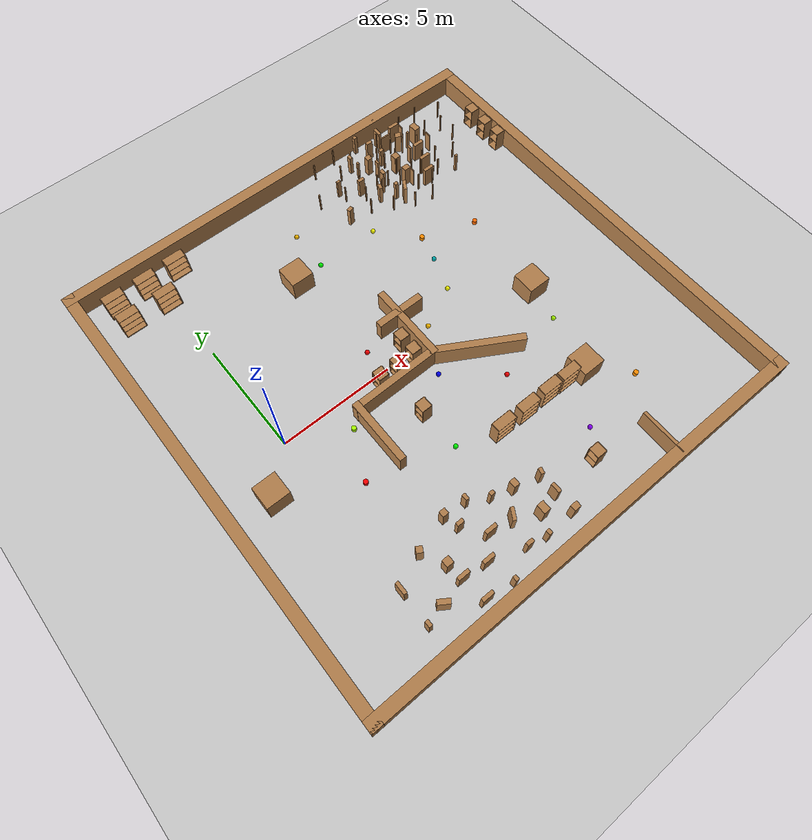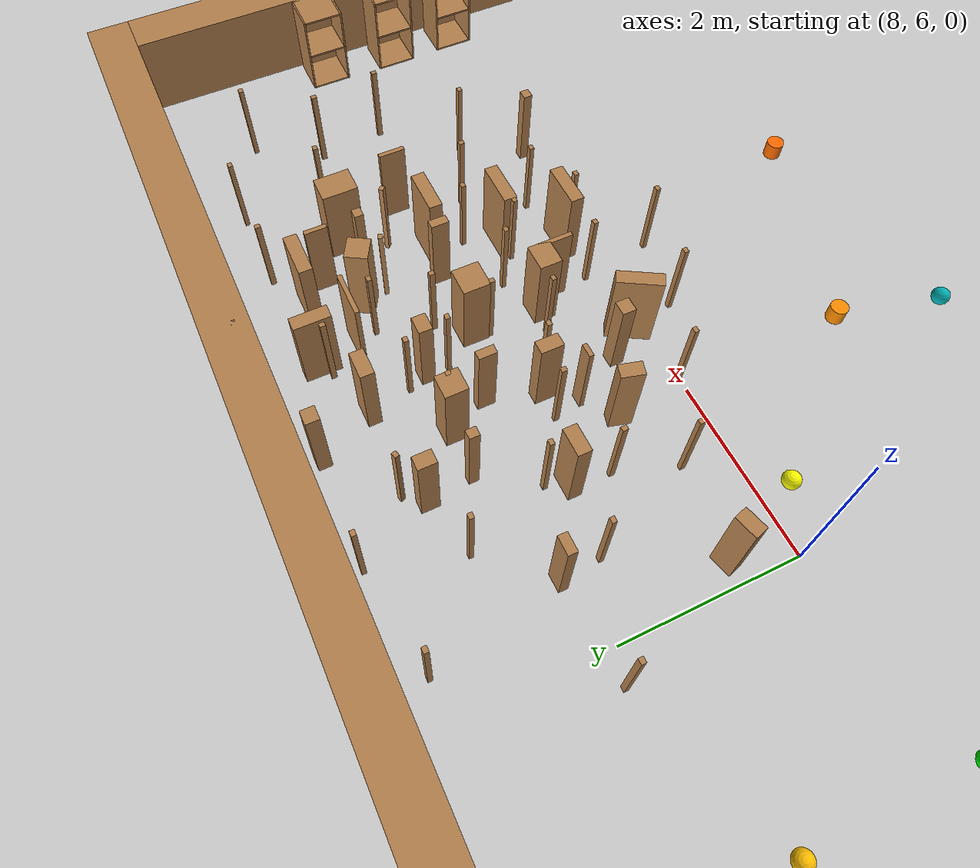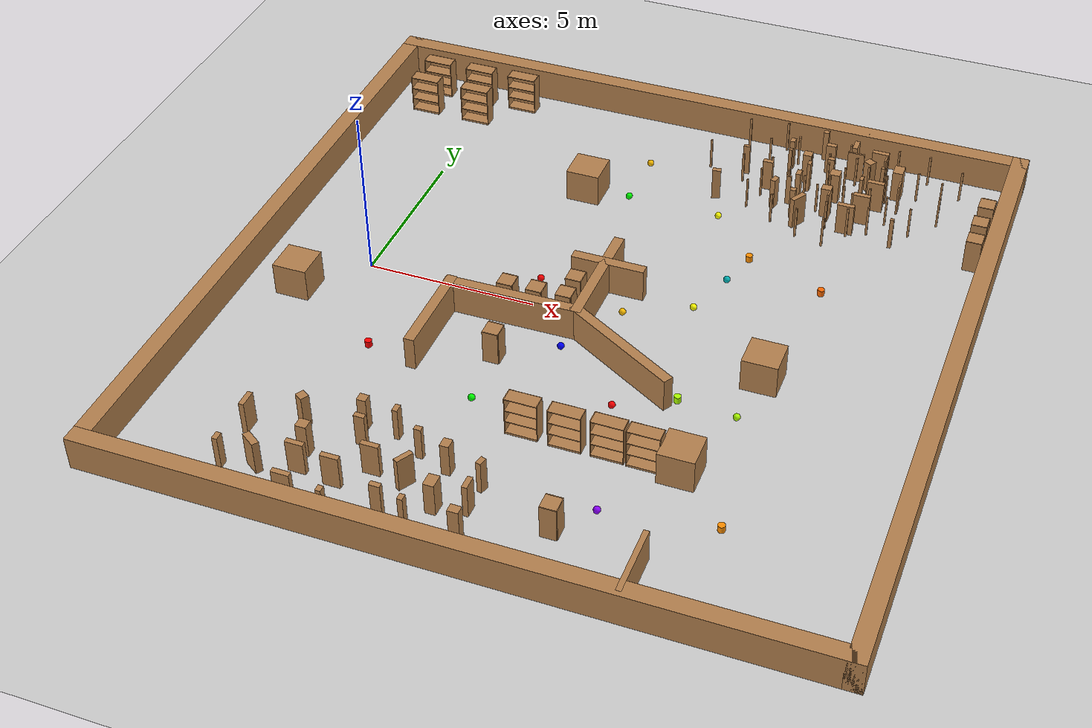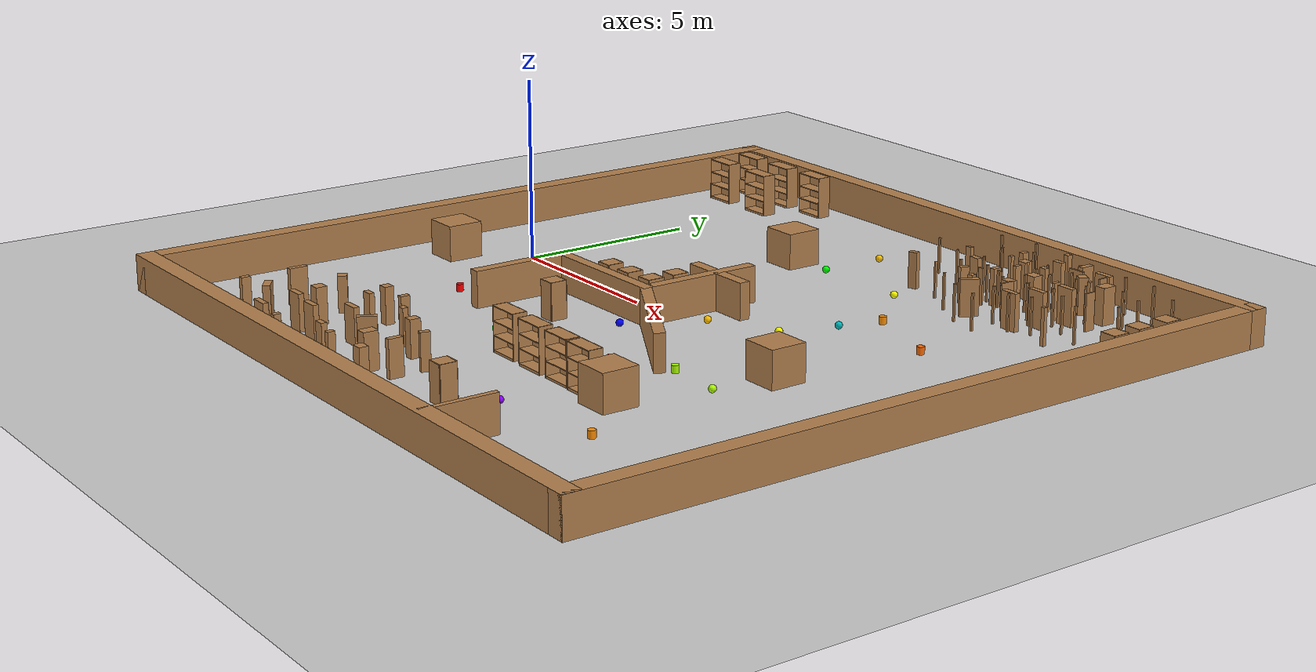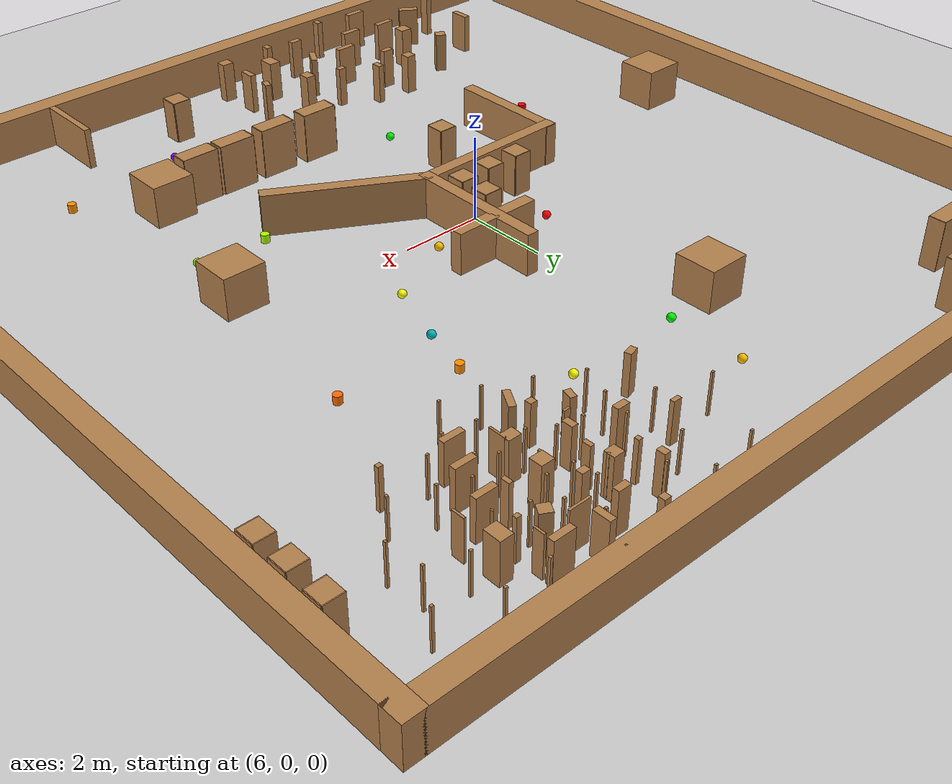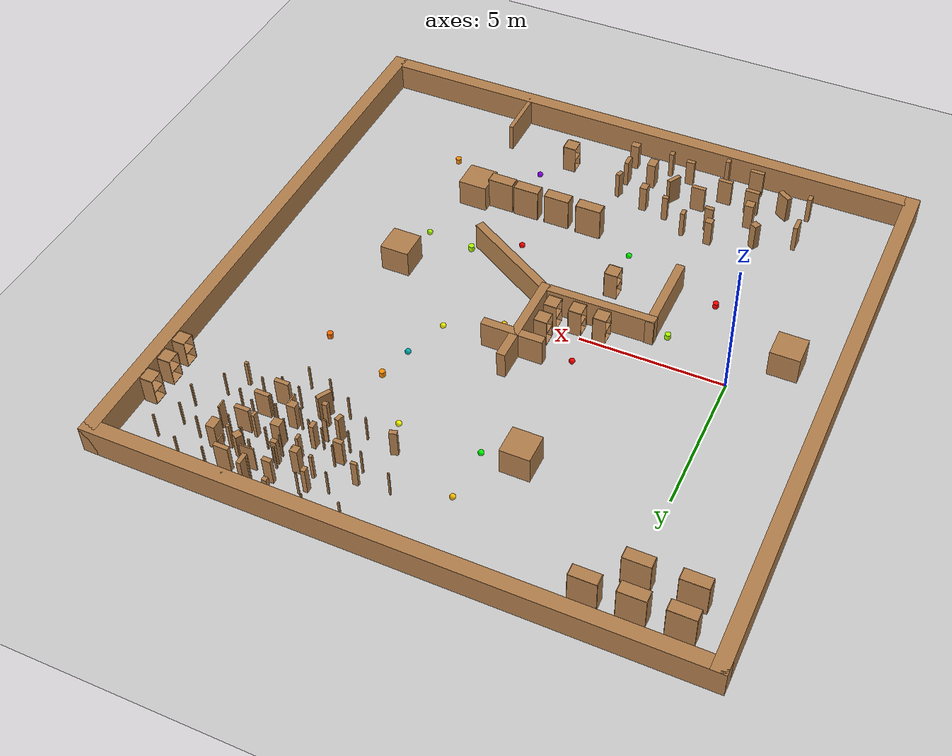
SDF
<sdf version="1.7">
 <world name="default">
  <light name="sun" type="directional">
   <pose>0 0 10 0 -0 0</pose>
   <diffuse>0.8 0.8 0.8 1</diffuse>
   <specular>0.2 0.2 0.2 1</specular>
   <attenuation>
    <range>1000</range>
    <constant>0.9</constant>
    <linear>0.01</linear>
    <quadratic>0.001</quadratic>
   </attenuation>
   <direction>-0.5 0.1 -0.9</direction>
   <spot><inner_angle>0</inner_angle><outer_angle>0</outer_angle><falloff>0</falloff></spot>
  </light>
  <model name="ground_plane">
   <pose>0 0 0 0 -0 0.716815</pose>
   <static>1</static>
   <link name="link">
    <collision name="collision">
     <geometry><plane><normal>0 0 1</normal><size>100 100</size></plane></geometry>
     <surface><friction><ode><mu>100</mu><mu2>50</mu2></ode></friction></surface>
    </collision>
    <visual name="visual">
     <cast_shadows>0</cast_shadows>
     <geometry><plane><normal>0 0 1</normal><size>100 100</size></plane></geometry>
     <material>
      <script><uri>file://media/materials/scripts/gazebo.material</uri><name>Gazebo/Grey</name></script>
     </material>
    </visual>
   </link>
  </model>
  <gravity>0 0 -9.8</gravity>
  <magnetic_field>6e-06 2.3e-05 -4.2e-05</magnetic_field>
  <atmosphere type="adiabatic"/>
  <physics type="ode">
   <max_step_size>0.001</max_step_size>
   <real_time_factor>1</real_time_factor>
   <real_time_update_rate>1000</real_time_update_rate>
  </physics>
  <scene><ambient>0.4 0.4 0.4 1</ambient><background>0.7 0.7 0.7 1</background><shadows>1</shadows></scene>
  <spherical_coordinates>
   <surface_model>EARTH_WGS84</surface_model>
   <latitude_deg>0</latitude_deg>
   <longitude_deg>0</longitude_deg>
   <elevation>0</elevation>
   <heading_deg>0</heading_deg>
  </spherical_coordinates>
  <model name="boundary20x20">
   <pose>6.68965 0.18325 0 0 -0 0</pose>
   <link name="Wall_0">
    <collision name="Wall_0_Collision">
     <geometry><box><size>20.5 0.5 1</size></box></geometry>
     <pose>0 0 0.5 0 -0 0</pose>
    </collision>
    <visual name="Wall_0_Visual">
     <pose>0 0 0.5 0 -0 0</pose>
     <geometry><box><size>20.5 0.5 1</size></box></geometry>
     <material>
      <script><uri>file://media/materials/scripts/gazebo.material</uri><name>Gazebo/Wood</name></script>
      <ambient>1 1 1 1</ambient>
     </material>
     <meta><layer>0</layer></meta>
    </visual>
    <pose>0 -10 0 0 -0 0</pose>
   </link>
   <link name="Wall_2">
    <collision name="Wall_2_Collision">
     <geometry><box><size>20.5 0.5 1</size></box></geometry>
     <pose>0 0 0.5 0 -0 0</pose>
    </collision>
    <visual name="Wall_2_Visual">
     <pose>0 0 0.5 0 -0 0</pose>
     <geometry><box><size>20.5 0.5 1</size></box></geometry>
     <material>
      <script><uri>file://media/materials/scripts/gazebo.material</uri><name>Gazebo/Wood</name></script>
      <ambient>1 1 1 1</ambient>
     </material>
     <meta><layer>0</layer></meta>
    </visual>
    <pose>-10 0 0 0 -0 -1.5708</pose>
   </link>
   <link name="Wall_4">
    <collision name="Wall_4_Collision">
     <geometry><box><size>20.5 0.5 1</size></box></geometry>
     <pose>0 0 0.5 0 -0 0</pose>
    </collision>
    <visual name="Wall_4_Visual">
     <pose>0 0 0.5 0 -0 0</pose>
     <geometry><box><size>20.5 0.5 1</size></box></geometry>
     <material>
      <script><uri>file://media/materials/scripts/gazebo.material</uri><name>Gazebo/Wood</name></script>
      <ambient>1 1 1 1</ambient>
     </material>
     <meta><layer>0</layer></meta>
    </visual>
    <pose>0 10 0 0 -0 0</pose>
   </link>
   <link name="Wall_8">
    <collision name="Wall_8_Collision">
     <geometry><box><size>20.5 0.5 1</size></box></geometry>
     <pose>0 0 0.5 0 -0 0</pose>
    </collision>
    <visual name="Wall_8_Visual">
     <pose>0 0 0.5 0 -0 0</pose>
     <geometry><box><size>20.5 0.5 1</size></box></geometry>
     <material>
      <script><uri>file://media/materials/scripts/gazebo.material</uri><name>Gazebo/Wood</name></script>
      <ambient>1 1 1 1</ambient>
     </material>
     <meta><layer>0</layer></meta>
    </visual>
    <pose>10 0 0 0 -0 1.5708</pose>
   </link>
   <static>1</static>
  </model>
  <model name="t7">
   <pose>13.3103 7.35329 0 0 -0 0</pose>
   <link name="Wall_0">
    <collision name="Wall_0_Collision">
     <geometry><box><size>0.5 0.15 1</size></box></geometry>
     <pose>0 0 0.5 0 -0 0</pose>
    </collision>
    <visual name="Wall_0_Visual">
     <pose>0 0 0.5 0 -0 0</pose>
     <geometry><box><size>0.5 0.15 1</size></box></geometry>
     <material>
      <script><uri>file://media/materials/scripts/gazebo.material</uri><name>Gazebo/Wood</name></script>
      <ambient>1 1 1 1</ambient>
     </material>
     <meta><layer>0</layer></meta>
    </visual>
    <pose>-0.649487 1.88869 0 0 -0 0</pose>
   </link>
   <link name="Wall_101">
    <collision name="Wall_101_Collision">
     <geometry><box><size>0.3 0.25 1</size></box></geometry>
     <pose>0 0 0.5 0 -0 0</pose>
    </collision>
    <visual name="Wall_101_Visual">
     <pose>0 0 0.5 0 -0 0</pose>
     <geometry><box><size>0.3 0.25 1</size></box></geometry>
     <material>
      <script><uri>file://media/materials/scripts/gazebo.material</uri><name>Gazebo/Wood</name></script>
      <ambient>1 1 1 1</ambient>
     </material>
     <meta><layer>0</layer></meta>
    </visual>
    <pose>-1.7299 -0.40612 0 0 -0 0</pose>
   </link>
   <link name="Wall_105">
    <collision name="Wall_105_Collision">
     <geometry><box><size>0.4 0.15 1</size></box></geometry>
     <pose>0 0 0.5 0 -0 0</pose>
    </collision>
    <visual name="Wall_105_Visual">
     <pose>0 0 0.5 0 -0 0</pose>
     <geometry><box><size>0.4 0.15 1</size></box></geometry>
     <material>
      <script><uri>file://media/materials/scripts/gazebo.material</uri><name>Gazebo/Wood</name></script>
      <ambient>1 1 1 1</ambient>
     </material>
     <meta><layer>0</layer></meta>
    </visual>
    <pose>-1.44962 2.04439 0 0 -0 -1.5708</pose>
   </link>
   <link name="Wall_36">
    <collision name="Wall_36_Collision">
     <geometry><box><size>0.26 0.25 1</size></box></geometry>
     <pose>0 0 0.5 0 -0 0</pose>
    </collision>
    <visual name="Wall_36_Visual">
     <pose>0 0 0.5 0 -0 0</pose>
     <geometry><box><size>0.26 0.25 1</size></box></geometry>
     <material>
      <script><uri>file://media/materials/scripts/gazebo.material</uri><name>Gazebo/Wood</name></script>
      <ambient>1 1 1 1</ambient>
     </material>
     <meta><layer>0</layer></meta>
    </visual>
    <pose>-2.70321 1.09078 0 0 -0 0</pose>
   </link>
   <link name="Wall_38">
    <collision name="Wall_38_Collision">
     <geometry><box><size>0.26 0.25 1</size></box></geometry>
     <pose>0 0 0.5 0 -0 0</pose>
    </collision>
    <visual name="Wall_38_Visual">
     <pose>0 0 0.5 0 -0 0</pose>
     <geometry><box><size>0.26 0.25 1</size></box></geometry>
     <material>
      <script><uri>file://media/materials/scripts/gazebo.material</uri><name>Gazebo/Wood</name></script>
      <ambient>1 1 1 1</ambient>
     </material>
     <meta><layer>0</layer></meta>
    </visual>
    <pose>-0.842821 1.30664 0 0 -0 -0.523599</pose>
   </link>
   <link name="Wall_54">
    <collision name="Wall_54_Collision">
     <geometry><box><size>0.5 0.15 1</size></box></geometry>
     <pose>0 0 0.5 0 -0 0</pose>
    </collision>
    <visual name="Wall_54_Visual">
     <pose>0 0 0.5 0 -0 0</pose>
     <geometry><box><size>0.5 0.15 1</size></box></geometry>
     <material>
      <script><uri>file://media/materials/scripts/gazebo.material</uri><name>Gazebo/Wood</name></script>
      <ambient>1 1 1 1</ambient>
     </material>
     <meta><layer>0</layer></meta>
    </visual>
    <pose>-0.981633 -1.06267 0 0 -0 0</pose>
   </link>
   <link name="Wall_58">
    <collision name="Wall_58_Collision">
     <geometry><box><size>0.5 0.15 1</size></box></geometry>
     <pose>0 0 0.5 0 -0 0</pose>
    </collision>
    <visual name="Wall_58_Visual">
     <pose>0 0 0.5 0 -0 0</pose>
     <geometry><box><size>0.5 0.15 1</size></box></geometry>
     <material>
      <script><uri>file://media/materials/scripts/gazebo.material</uri><name>Gazebo/Wood</name></script>
      <ambient>1 1 1 1</ambient>
     </material>
     <meta><layer>0</layer></meta>
    </visual>
    <pose>-0.425004 0.347148 0 0 -0 0</pose>
   </link>
   <link name="Wall_60">
    <collision name="Wall_60_Collision">
     <geometry><box><size>0.3 0.15 1</size></box></geometry>
     <pose>0 0 0.5 0 -0 0</pose>
    </collision>
    <visual name="Wall_60_Visual">
     <pose>0 0 0.5 0 -0 0</pose>
     <geometry><box><size>0.3 0.15 1</size></box></geometry>
     <material>
      <script><uri>file://media/materials/scripts/gazebo.material</uri><name>Gazebo/Wood</name></script>
      <ambient>1 1 1 1</ambient>
     </material>
     <meta><layer>0</layer></meta>
    </visual>
    <pose>-3.72546 0.303649 0 0 -0 0</pose>
   </link>
   <link name="Wall_64">
    <collision name="Wall_64_Collision">
     <geometry><box><size>0.499906 0.15 1</size></box></geometry>
     <pose>0 0 0.5 0 -0 0</pose>
    </collision>
    <visual name="Wall_64_Visual">
     <pose>0 0 0.5 0 -0 0</pose>
     <geometry><box><size>0.499906 0.15 1</size></box></geometry>
     <material>
      <script><uri>file://media/materials/scripts/gazebo.material</uri><name>Gazebo/Wood</name></script>
      <ambient>1 1 1 1</ambient>
     </material>
     <meta><layer>0</layer></meta>
    </visual>
    <pose>-2.40422 -1.13934 0 0 -0 -2.09455</pose>
   </link>
   <link name="Wall_66">
    <collision name="Wall_66_Collision">
     <geometry><box><size>0.2 0.15 1</size></box></geometry>
     <pose>0 0 0.5 0 -0 0</pose>
    </collision>
    <visual name="Wall_66_Visual">
     <pose>0 0 0.5 0 -0 0</pose>
     <geometry><box><size>0.2 0.15 1</size></box></geometry>
     <material>
      <script><uri>file://media/materials/scripts/gazebo.material</uri><name>Gazebo/Wood</name></script>
      <ambient>1 1 1 1</ambient>
     </material>
     <meta><layer>0</layer></meta>
    </visual>
    <pose>-3.32256 1.63712 0 0 -0 -1.5708</pose>
   </link>
   <link name="Wall_70">
    <collision name="Wall_70_Collision">
     <geometry><box><size>0.3 0.15 1</size></box></geometry>
     <pose>0 0 0.5 0 -0 0</pose>
    </collision>
    <visual name="Wall_70_Visual">
     <pose>0 0 0.5 0 -0 0</pose>
     <geometry><box><size>0.3 0.15 1</size></box></geometry>
     <material>
      <script><uri>file://media/materials/scripts/gazebo.material</uri><name>Gazebo/Wood</name></script>
      <ambient>1 1 1 1</ambient>
     </material>
     <meta><layer>0</layer></meta>
    </visual>
    <pose>-2.14832 1.77582 0 0 -0 0</pose>
   </link>
   <link name="Wall_74">
    <collision name="Wall_74_Collision">
     <geometry><box><size>0.2 0.15 1</size></box></geometry>
     <pose>0 0 0.5 0 -0 0</pose>
    </collision>
    <visual name="Wall_74_Visual">
     <pose>0 0 0.5 0 -0 0</pose>
     <geometry><box><size>0.2 0.15 1</size></box></geometry>
     <material>
      <script><uri>file://media/materials/scripts/gazebo.material</uri><name>Gazebo/Wood</name></script>
      <ambient>1 1 1 1</ambient>
     </material>
     <meta><layer>0</layer></meta>
    </visual>
    <pose>-1.97481 1.07494 0 0 -0 0</pose>
   </link>
   <link name="Wall_78">
    <collision name="Wall_78_Collision">
     <geometry><box><size>0.31 0.3 1</size></box></geometry>
     <pose>0 0 0.5 0 -0 0</pose>
    </collision>
    <visual name="Wall_78_Visual">
     <pose>0 0 0.5 0 -0 0</pose>
     <geometry><box><size>0.31 0.3 1</size></box></geometry>
     <material>
      <script><uri>file://media/materials/scripts/gazebo.material</uri><name>Gazebo/Wood</name></script>
      <ambient>1 1 1 1</ambient>
     </material>
     <meta><layer>0</layer></meta>
    </visual>
    <pose>-1.67805 0.407964 0 0 -0 0</pose>
   </link>
   <link name="Wall_8">
    <collision name="Wall_8_Collision">
     <geometry><box><size>0.25 0.15 1</size></box></geometry>
     <pose>0 0 0.5 0 -0 0</pose>
    </collision>
    <visual name="Wall_8_Visual">
     <pose>0 0 0.5 0 -0 0</pose>
     <geometry><box><size>0.25 0.15 1</size></box></geometry>
     <material>
      <script><uri>file://media/materials/scripts/gazebo.material</uri><name>Gazebo/Wood</name></script>
      <ambient>1 1 1 1</ambient>
     </material>
     <meta><layer>0</layer></meta>
    </visual>
    <pose>-2.70615 0.053388 0 0 -0 -1.5708</pose>
   </link>
   <link name="Wall_80">
    <collision name="Wall_80_Collision">
     <geometry><box><size>0.4 0.3 1</size></box></geometry>
     <pose>0 0 0.5 0 -0 0</pose>
    </collision>
    <visual name="Wall_80_Visual">
     <pose>0 0 0.5 0 -0 0</pose>
     <geometry><box><size>0.4 0.3 1</size></box></geometry>
     <material>
      <script><uri>file://media/materials/scripts/gazebo.material</uri><name>Gazebo/Wood</name></script>
      <ambient>1 1 1 1</ambient>
     </material>
     <meta><layer>0</layer></meta>
    </visual>
    <pose>0.066257 1.20372 0 0 -0 1.5708</pose>
   </link>
   <link name="Wall_95">
    <collision name="Wall_95_Collision">
     <geometry><box><size>0.250424 0.15 1</size></box></geometry>
     <pose>0 0 0.5 0 -0 0</pose>
    </collision>
    <visual name="Wall_95_Visual">
     <pose>0 0 0.5 0 -0 0</pose>
     <geometry><box><size>0.250424 0.15 1</size></box></geometry>
     <material>
      <script><uri>file://media/materials/scripts/gazebo.material</uri><name>Gazebo/Wood</name></script>
      <ambient>1 1 1 1</ambient>
     </material>
     <meta><layer>0</layer></meta>
    </visual>
    <pose>-3.29392 -0.515931 0 0 -0 -1.83268</pose>
   </link>
   <link name="Wall_97">
    <collision name="Wall_97_Collision">
     <geometry><box><size>0.5 0.15 1</size></box></geometry>
     <pose>0 0 0.5 0 -0 0</pose>
    </collision>
    <visual name="Wall_97_Visual">
     <pose>0 0 0.5 0 -0 0</pose>
     <geometry><box><size>0.5 0.15 1</size></box></geometry>
     <material>
      <script><uri>file://media/materials/scripts/gazebo.material</uri><name>Gazebo/Wood</name></script>
      <ambient>1 1 1 1</ambient>
     </material>
     <meta><layer>0</layer></meta>
    </visual>
    <pose>-0.667027 -0.419912 0 0 -0 0</pose>
   </link>
   <static>1</static>
  </model>
  <model name="t5">
   <pose>3.29174 -8.44012 0 0 -0 0</pose>
   <link name="Wall_0">
    <collision name="Wall_0_Collision">
     <geometry><box><size>0.5 0.15 1</size></box></geometry>
     <pose>0 0 0.5 0 -0 0</pose>
    </collision>
    <visual name="Wall_0_Visual">
     <pose>0 0 0.5 0 -0 0</pose>
     <geometry><box><size>0.5 0.15 1</size></box></geometry>
     <material>
      <script><uri>file://media/materials/scripts/gazebo.material</uri><name>Gazebo/Wood</name></script>
      <ambient>1 1 1 1</ambient>
     </material>
     <meta><layer>0</layer></meta>
    </visual>
    <pose>0.390596 0.875877 0 0 -0 0</pose>
   </link>
   <link name="Wall_101">
    <collision name="Wall_101_Collision">
     <geometry><box><size>0.3 0.25 1</size></box></geometry>
     <pose>0 0 0.5 0 -0 0</pose>
    </collision>
    <visual name="Wall_101_Visual">
     <pose>0 0 0.5 0 -0 0</pose>
     <geometry><box><size>0.3 0.25 1</size></box></geometry>
     <material>
      <script><uri>file://media/materials/scripts/gazebo.material</uri><name>Gazebo/Wood</name></script>
      <ambient>1 1 1 1</ambient>
     </material>
     <meta><layer>0</layer></meta>
    </visual>
    <pose>3.25747 -0.423314 0 0 -0 0</pose>
   </link>
   <link name="Wall_103">
    <collision name="Wall_103_Collision">
     <geometry><box><size>0.3 0.25 1</size></box></geometry>
     <pose>0 0 0.5 0 -0 0</pose>
    </collision>
    <visual name="Wall_103_Visual">
     <pose>0 0 0.5 0 -0 0</pose>
     <geometry><box><size>0.3 0.25 1</size></box></geometry>
     <material>
      <script><uri>file://media/materials/scripts/gazebo.material</uri><name>Gazebo/Wood</name></script>
      <ambient>1 1 1 1</ambient>
     </material>
     <meta><layer>0</layer></meta>
    </visual>
    <pose>2.15255 1.5852 0 0 -0 -1.5708</pose>
   </link>
   <link name="Wall_105">
    <collision name="Wall_105_Collision">
     <geometry><box><size>0.4 0.15 1</size></box></geometry>
     <pose>0 0 0.5 0 -0 0</pose>
    </collision>
    <visual name="Wall_105_Visual">
     <pose>0 0 0.5 0 -0 0</pose>
     <geometry><box><size>0.4 0.15 1</size></box></geometry>
     <material>
      <script><uri>file://media/materials/scripts/gazebo.material</uri><name>Gazebo/Wood</name></script>
      <ambient>1 1 1 1</ambient>
     </material>
     <meta><layer>0</layer></meta>
    </visual>
    <pose>3.19281 0.500574 0 0 -0 -1.5708</pose>
   </link>
   <link name="Wall_21">
    <collision name="Wall_21_Collision">
     <geometry><box><size>0.500017 0.2 1</size></box></geometry>
     <pose>0 0 0.5 0 -0 0</pose>
    </collision>
    <visual name="Wall_21_Visual">
     <pose>0 0 0.5 0 -0 0</pose>
     <geometry><box><size>0.500017 0.2 1</size></box></geometry>
     <material>
      <script><uri>file://media/materials/scripts/gazebo.material</uri><name>Gazebo/Wood</name></script>
      <ambient>1 1 1 1</ambient>
     </material>
     <meta><layer>0</layer></meta>
    </visual>
    <pose>-2.48871 0.02876 0 0 -0 -0.586607</pose>
   </link>
   <link name="Wall_36">
    <collision name="Wall_36_Collision">
     <geometry><box><size>0.26 0.25 1</size></box></geometry>
     <pose>0 0 0.5 0 -0 0</pose>
    </collision>
    <visual name="Wall_36_Visual">
     <pose>0 0 0.5 0 -0 0</pose>
     <geometry><box><size>0.26 0.25 1</size></box></geometry>
     <material>
      <script><uri>file://media/materials/scripts/gazebo.material</uri><name>Gazebo/Wood</name></script>
      <ambient>1 1 1 1</ambient>
     </material>
     <meta><layer>0</layer></meta>
    </visual>
    <pose>-0.523693 2.35884 0 0 -0 0</pose>
   </link>
   <link name="Wall_38">
    <collision name="Wall_38_Collision">
     <geometry><box><size>0.26 0.25 1</size></box></geometry>
     <pose>0 0 0.5 0 -0 0</pose>
    </collision>
    <visual name="Wall_38_Visual">
     <pose>0 0 0.5 0 -0 0</pose>
     <geometry><box><size>0.26 0.25 1</size></box></geometry>
     <material>
      <script><uri>file://media/materials/scripts/gazebo.material</uri><name>Gazebo/Wood</name></script>
      <ambient>1 1 1 1</ambient>
     </material>
     <meta><layer>0</layer></meta>
    </visual>
    <pose>-2.02428 1.89989 0 0 -0 -0.523599</pose>
   </link>
   <link name="Wall_54">
    <collision name="Wall_54_Collision">
     <geometry><box><size>0.5 0.15 1</size></box></geometry>
     <pose>0 0 0.5 0 -0 0</pose>
    </collision>
    <visual name="Wall_54_Visual">
     <pose>0 0 0.5 0 -0 0</pose>
     <geometry><box><size>0.5 0.15 1</size></box></geometry>
     <material>
      <script><uri>file://media/materials/scripts/gazebo.material</uri><name>Gazebo/Wood</name></script>
      <ambient>1 1 1 1</ambient>
     </material>
     <meta><layer>0</layer></meta>
    </visual>
    <pose>-1.2248 -0.767096 0 0 -0 0</pose>
   </link>
   <link name="Wall_58">
    <collision name="Wall_58_Collision">
     <geometry><box><size>0.5 0.15 1</size></box></geometry>
     <pose>0 0 0.5 0 -0 0</pose>
    </collision>
    <visual name="Wall_58_Visual">
     <pose>0 0 0.5 0 -0 0</pose>
     <geometry><box><size>0.5 0.15 1</size></box></geometry>
     <material>
      <script><uri>file://media/materials/scripts/gazebo.material</uri><name>Gazebo/Wood</name></script>
      <ambient>1 1 1 1</ambient>
     </material>
     <meta><layer>0</layer></meta>
    </visual>
    <pose>-0.357412 0.15396 0 0 -0 0</pose>
   </link>
   <link name="Wall_6">
    <collision name="Wall_6_Collision">
     <geometry><box><size>0.25 0.15 1</size></box></geometry>
     <pose>0 0 0.5 0 -0 0</pose>
    </collision>
    <visual name="Wall_6_Visual">
     <pose>0 0 0.5 0 -0 0</pose>
     <geometry><box><size>0.25 0.15 1</size></box></geometry>
     <material>
      <script><uri>file://media/materials/scripts/gazebo.material</uri><name>Gazebo/Wood</name></script>
      <ambient>1 1 1 1</ambient>
     </material>
     <meta><layer>0</layer></meta>
    </visual>
    <pose>0.445072 2.30581 0 0 -0 -1.5708</pose>
   </link>
   <link name="Wall_60">
    <collision name="Wall_60_Collision">
     <geometry><box><size>0.3 0.15 1</size></box></geometry>
     <pose>0 0 0.5 0 -0 0</pose>
    </collision>
    <visual name="Wall_60_Visual">
     <pose>0 0 0.5 0 -0 0</pose>
     <geometry><box><size>0.3 0.15 1</size></box></geometry>
     <material>
      <script><uri>file://media/materials/scripts/gazebo.material</uri><name>Gazebo/Wood</name></script>
      <ambient>1 1 1 1</ambient>
     </material>
     <meta><layer>0</layer></meta>
    </visual>
    <pose>1.1191 -0.338071 0 0 -0 0</pose>
   </link>
   <link name="Wall_62">
    <collision name="Wall_62_Collision">
     <geometry><box><size>0.2 0.15 1</size></box></geometry>
     <pose>0 0 0.5 0 -0 0</pose>
    </collision>
    <visual name="Wall_62_Visual">
     <pose>0 0 0.5 0 -0 0</pose>
     <geometry><box><size>0.2 0.15 1</size></box></geometry>
     <material>
      <script><uri>file://media/materials/scripts/gazebo.material</uri><name>Gazebo/Wood</name></script>
      <ambient>1 1 1 1</ambient>
     </material>
     <meta><layer>0</layer></meta>
    </visual>
    <pose>-0.086348 -0.9322 0 0 -0 -1.5708</pose>
   </link>
   <link name="Wall_64">
    <collision name="Wall_64_Collision">
     <geometry><box><size>0.499906 0.15 1</size></box></geometry>
     <pose>0 0 0.5 0 -0 0</pose>
    </collision>
    <visual name="Wall_64_Visual">
     <pose>0 0 0.5 0 -0 0</pose>
     <geometry><box><size>0.499906 0.15 1</size></box></geometry>
     <material>
      <script><uri>file://media/materials/scripts/gazebo.material</uri><name>Gazebo/Wood</name></script>
      <ambient>1 1 1 1</ambient>
     </material>
     <meta><layer>0</layer></meta>
    </visual>
    <pose>1.35421 0.773368 0 0 -0 -2.09455</pose>
   </link>
   <link name="Wall_66">
    <collision name="Wall_66_Collision">
     <geometry><box><size>0.2 0.15 1</size></box></geometry>
     <pose>0 0 0.5 0 -0 0</pose>
    </collision>
    <visual name="Wall_66_Visual">
     <pose>0 0 0.5 0 -0 0</pose>
     <geometry><box><size>0.2 0.15 1</size></box></geometry>
     <material>
      <script><uri>file://media/materials/scripts/gazebo.material</uri><name>Gazebo/Wood</name></script>
      <ambient>1 1 1 1</ambient>
     </material>
     <meta><layer>0</layer></meta>
    </visual>
    <pose>1.8921 -0.50407 0 0 -0 -1.5708</pose>
   </link>
   <link name="Wall_70">
    <collision name="Wall_70_Collision">
     <geometry><box><size>0.3 0.15 1</size></box></geometry>
     <pose>0 0 0.5 0 -0 0</pose>
    </collision>
    <visual name="Wall_70_Visual">
     <pose>0 0 0.5 0 -0 0</pose>
     <geometry><box><size>0.3 0.15 1</size></box></geometry>
     <material>
      <script><uri>file://media/materials/scripts/gazebo.material</uri><name>Gazebo/Wood</name></script>
      <ambient>1 1 1 1</ambient>
     </material>
     <meta><layer>0</layer></meta>
    </visual>
    <pose>-0.309733 1.73449 0 0 -0 0</pose>
   </link>
   <link name="Wall_74">
    <collision name="Wall_74_Collision">
     <geometry><box><size>0.2 0.15 1</size></box></geometry>
     <pose>0 0 0.5 0 -0 0</pose>
    </collision>
    <visual name="Wall_74_Visual">
     <pose>0 0 0.5 0 -0 0</pose>
     <geometry><box><size>0.2 0.15 1</size></box></geometry>
     <material>
      <script><uri>file://media/materials/scripts/gazebo.material</uri><name>Gazebo/Wood</name></script>
      <ambient>1 1 1 1</ambient>
     </material>
     <meta><layer>0</layer></meta>
    </visual>
    <pose>1.27676 1.82106 0 0 -0 0</pose>
   </link>
   <link name="Wall_78">
    <collision name="Wall_78_Collision">
     <geometry><box><size>0.31 0.3 1</size></box></geometry>
     <pose>0 0 0.5 0 -0 0</pose>
    </collision>
    <visual name="Wall_78_Visual">
     <pose>0 0 0.5 0 -0 0</pose>
     <geometry><box><size>0.31 0.3 1</size></box></geometry>
     <material>
      <script><uri>file://media/materials/scripts/gazebo.material</uri><name>Gazebo/Wood</name></script>
      <ambient>1 1 1 1</ambient>
     </material>
     <meta><layer>0</layer></meta>
    </visual>
    <pose>-1.52196 0.966018 0 0 -0 0</pose>
   </link>
   <link name="Wall_8">
    <collision name="Wall_8_Collision">
     <geometry><box><size>0.25 0.15 1</size></box></geometry>
     <pose>0 0 0.5 0 -0 0</pose>
    </collision>
    <visual name="Wall_8_Visual">
     <pose>0 0 0.5 0 -0 0</pose>
     <geometry><box><size>0.25 0.15 1</size></box></geometry>
     <material>
      <script><uri>file://media/materials/scripts/gazebo.material</uri><name>Gazebo/Wood</name></script>
      <ambient>1 1 1 1</ambient>
     </material>
     <meta><layer>0</layer></meta>
    </visual>
    <pose>-3.33247 -0.186061 0 0 -0 -1.5708</pose>
   </link>
   <link name="Wall_80">
    <collision name="Wall_80_Collision">
     <geometry><box><size>0.4 0.3 1</size></box></geometry>
     <pose>0 0 0.5 0 -0 0</pose>
    </collision>
    <visual name="Wall_80_Visual">
     <pose>0 0 0.5 0 -0 0</pose>
     <geometry><box><size>0.4 0.3 1</size></box></geometry>
     <material>
      <script><uri>file://media/materials/scripts/gazebo.material</uri><name>Gazebo/Wood</name></script>
      <ambient>1 1 1 1</ambient>
     </material>
     <meta><layer>0</layer></meta>
    </visual>
    <pose>2.34433 0.262311 0 0 -0 1.5708</pose>
   </link>
   <link name="Wall_95">
    <collision name="Wall_95_Collision">
     <geometry><box><size>0.250424 0.15 1</size></box></geometry>
     <pose>0 0 0.5 0 -0 0</pose>
    </collision>
    <visual name="Wall_95_Visual">
     <pose>0 0 0.5 0 -0 0</pose>
     <geometry><box><size>0.250424 0.15 1</size></box></geometry>
     <material>
      <script><uri>file://media/materials/scripts/gazebo.material</uri><name>Gazebo/Wood</name></script>
      <ambient>1 1 1 1</ambient>
     </material>
     <meta><layer>0</layer></meta>
    </visual>
    <pose>3.21102 1.29922 0 0 -0 -1.83268</pose>
   </link>
   <link name="Wall_97">
    <collision name="Wall_97_Collision">
     <geometry><box><size>0.5 0.15 1</size></box></geometry>
     <pose>0 0 0.5 0 -0 0</pose>
    </collision>
    <visual name="Wall_97_Visual">
     <pose>0 0 0.5 0 -0 0</pose>
     <geometry><box><size>0.5 0.15 1</size></box></geometry>
     <material>
      <script><uri>file://media/materials/scripts/gazebo.material</uri><name>Gazebo/Wood</name></script>
      <ambient>1 1 1 1</ambient>
     </material>
     <meta><layer>0</layer></meta>
    </visual>
    <pose>-1.39392 0.285977 0 0 -0 0</pose>
   </link>
   <link name="Wall_99">
    <collision name="Wall_99_Collision">
     <geometry><box><size>0.5 0.15 1</size></box></geometry>
     <pose>0 0 0.5 0 -0 0</pose>
    </collision>
    <visual name="Wall_99_Visual">
     <pose>0 0 0.5 0 -0 0</pose>
     <geometry><box><size>0.5 0.15 1</size></box></geometry>
     <material>
      <script><uri>file://media/materials/scripts/gazebo.material</uri><name>Gazebo/Wood</name></script>
      <ambient>1 1 1 1</ambient>
     </material>
     <meta><layer>0</layer></meta>
    </visual>
    <pose>-3.32186 1.2883 0 0 -0 -1.5708</pose>
   </link>
   <static>1</static>
  </model>
  <model name="sphere_yo">
   <link name="link_1">
    <pose>0 0 0.1 0 -0 0</pose>
    <inertial>
     <mass>1</mass>
     <inertia><ixx>0.1</ixx><ixy>0</ixy><ixz>0</ixz><iyy>0.1</iyy><iyz>0</iyz><izz>0.1</izz></inertia>
    </inertial>
    <visual name="visual">
     <geometry><sphere><radius>0.1</radius></sphere></geometry>
     <material>
      <lighting>1</lighting>
      <script><uri>file://media/materials/scripts/gazebo.material</uri><name>Gazebo/Grey</name></script>
      <ambient>1 0.749 0 1</ambient>
      <diffuse>1 0.749 0 1</diffuse>
      <specular>0 0 0 1</specular>
      <emissive>0 0 0 1</emissive>
      <shader type="vertex"><normal_map>__default__</normal_map></shader>
     </material>
    </visual>
    <collision name="collision">
     <geometry><sphere><radius>0.1</radius></sphere></geometry>
     <surface>
      <friction>
       <ode><mu>1</mu><mu2>1</mu2><fdir1>0 0 0</fdir1><slip1>0</slip1><slip2>0</slip2></ode>
       <torsional>
        <coefficient>1</coefficient>
        <patch_radius>0</patch_radius>
        <surface_radius>0</surface_radius>
        <use_patch_radius>1</use_patch_radius>
        <ode><slip>0</slip></ode>
       </torsional>
      </friction>
      <bounce><restitution_coefficient>0</restitution_coefficient><threshold>1e+06</threshold></bounce>
      <contact>
       <collide_without_contact>0</collide_without_contact>
       <collide_without_contact_bitmask>1</collide_without_contact_bitmask>
       <collide_bitmask>1</collide_bitmask>
       <ode>
        <soft_cfm>0</soft_cfm>
        <soft_erp>0.2</soft_erp>
        <kp>1e+13</kp>
        <kd>1</kd>
        <max_vel>0.01</max_vel>
        <min_depth>0</min_depth>
       </ode>
       <bullet>
        <split_impulse>1</split_impulse>
        <split_impulse_penetration_threshold>-0.01</split_impulse_penetration_threshold>
        <soft_cfm>0</soft_cfm>
        <soft_erp>0.2</soft_erp>
        <kp>1e+13</kp>
        <kd>1</kd>
       </bullet>
      </contact>
     </surface>
    </collision>
   </link>
   <static>1</static>
   <pose>7.49354 0.467227 0 0 -0 0</pose>
  </model>
  <model name="sphere_bg">
   <link name="link_1">
    <pose>0 0 0.1 0 -0 0</pose>
    <inertial>
     <mass>1</mass>
     <inertia><ixx>0.1</ixx><ixy>0</ixy><ixz>0</ixz><iyy>0.1</iyy><iyz>0</iyz><izz>0.1</izz></inertia>
    </inertial>
    <visual name="visual">
     <geometry><sphere><radius>0.1</radius></sphere></geometry>
     <material>
      <lighting>1</lighting>
      <script><uri>file://media/materials/scripts/gazebo.material</uri><name>Gazebo/Grey</name></script>
      <ambient>0 0.71 0.722 1</ambient>
      <diffuse>0 0.71 0.722 1</diffuse>
      <specular>0 0 0 1</specular>
      <emissive>0 0 0 1</emissive>
      <shader type="vertex"><normal_map>__default__</normal_map></shader>
     </material>
    </visual>
    <collision name="collision">
     <geometry><sphere><radius>0.1</radius></sphere></geometry>
     <surface>
      <friction>
       <ode><mu>1</mu><mu2>1</mu2><fdir1>0 0 0</fdir1><slip1>0</slip1><slip2>0</slip2></ode>
       <torsional>
        <coefficient>1</coefficient>
        <patch_radius>0</patch_radius>
        <surface_radius>0</surface_radius>
        <use_patch_radius>1</use_patch_radius>
        <ode><slip>0</slip></ode>
       </torsional>
      </friction>
      <bounce><restitution_coefficient>0</restitution_coefficient><threshold>1e+06</threshold></bounce>
      <contact>
       <collide_without_contact>0</collide_without_contact>
       <collide_without_contact_bitmask>1</collide_without_contact_bitmask>
       <collide_bitmask>1</collide_bitmask>
       <ode>
        <soft_cfm>0</soft_cfm>
        <soft_erp>0.2</soft_erp>
        <kp>1e+13</kp>
        <kd>1</kd>
        <max_vel>0.01</max_vel>
        <min_depth>0</min_depth>
       </ode>
       <bullet>
        <split_impulse>1</split_impulse>
        <split_impulse_penetration_threshold>-0.01</split_impulse_penetration_threshold>
        <soft_cfm>0</soft_cfm>
        <soft_erp>0.2</soft_erp>
        <kp>1e+13</kp>
        <kd>1</kd>
       </bullet>
      </contact>
     </surface>
    </collision>
   </link>
   <static>1</static>
   <pose>9.79753 2.85162 0 0 -0 0</pose>
  </model>
  <model name="sphere_g">
   <link name="link_1">
    <pose>0 0 0.1 0 -0 0</pose>
    <inertial>
     <mass>1</mass>
     <inertia><ixx>0.1</ixx><ixy>0</ixy><ixz>0</ixz><iyy>0.1</iyy><iyz>0</iyz><izz>0.1</izz></inertia>
    </inertial>
    <visual name="visual">
     <geometry><sphere><radius>0.1</radius></sphere></geometry>
     <material>
      <lighting>1</lighting>
      <script><uri>file://media/materials/scripts/gazebo.material</uri><name>Gazebo/Grey</name></script>
      <ambient>0 1 0 1</ambient>
      <diffuse>0 1 0 1</diffuse>
      <specular>0 0 0 1</specular>
      <emissive>0 0 0 1</emissive>
      <shader type="vertex"><normal_map>__default__</normal_map></shader>
     </material>
    </visual>
    <collision name="collision">
     <geometry><sphere><radius>0.1</radius></sphere></geometry>
     <surface>
      <friction>
       <ode><mu>1</mu><mu2>1</mu2><fdir1>0 0 0</fdir1><slip1>0</slip1><slip2>0</slip2></ode>
       <torsional>
        <coefficient>1</coefficient>
        <patch_radius>0</patch_radius>
        <surface_radius>0</surface_radius>
        <use_patch_radius>1</use_patch_radius>
        <ode><slip>0</slip></ode>
       </torsional>
      </friction>
      <bounce><restitution_coefficient>0</restitution_coefficient><threshold>1e+06</threshold></bounce>
      <contact>
       <collide_without_contact>0</collide_without_contact>
       <collide_without_contact_bitmask>1</collide_without_contact_bitmask>
       <collide_bitmask>1</collide_bitmask>
       <ode>
        <soft_cfm>0</soft_cfm>
        <soft_erp>0.2</soft_erp>
        <kp>1e+13</kp>
        <kd>1</kd>
        <max_vel>0.01</max_vel>
        <min_depth>0</min_depth>
       </ode>
       <bullet>
        <split_impulse>1</split_impulse>
        <split_impulse_penetration_threshold>-0.01</split_impulse_penetration_threshold>
        <soft_cfm>0</soft_cfm>
        <soft_erp>0.2</soft_erp>
        <kp>1e+13</kp>
        <kd>1</kd>
       </bullet>
      </contact>
     </surface>
    </collision>
   </link>
   <static>1</static>
   <pose>5.85173 5.66826 0 0 -0 0</pose>
  </model>
  <model name="sphere_g_0">
   <link name="link_1">
    <pose>0 0 0.1 0 -0 0</pose>
    <inertial>
     <mass>1</mass>
     <inertia><ixx>0.1</ixx><ixy>0</ixy><ixz>0</ixz><iyy>0.1</iyy><iyz>0</iyz><izz>0.1</izz></inertia>
    </inertial>
    <visual name="visual">
     <geometry><sphere><radius>0.1</radius></sphere></geometry>
     <material>
      <lighting>1</lighting>
      <script><uri>file://media/materials/scripts/gazebo.material</uri><name>Gazebo/Grey</name></script>
      <ambient>0 1 0 1</ambient>
      <diffuse>0 1 0 1</diffuse>
      <specular>0 0 0 1</specular>
      <emissive>0 0 0 1</emissive>
      <shader type="vertex"><normal_map>__default__</normal_map></shader>
     </material>
    </visual>
    <collision name="collision">
     <geometry><sphere><radius>0.1</radius></sphere></geometry>
     <surface>
      <friction>
       <ode><mu>1</mu><mu2>1</mu2><fdir1>0 0 0</fdir1><slip1>0</slip1><slip2>0</slip2></ode>
       <torsional>
        <coefficient>1</coefficient>
        <patch_radius>0</patch_radius>
        <surface_radius>0</surface_radius>
        <use_patch_radius>1</use_patch_radius>
        <ode><slip>0</slip></ode>
       </torsional>
      </friction>
      <bounce><restitution_coefficient>0</restitution_coefficient><threshold>1e+06</threshold></bounce>
      <contact>
       <collide_without_contact>0</collide_without_contact>
       <collide_without_contact_bitmask>1</collide_without_contact_bitmask>
       <collide_bitmask>1</collide_bitmask>
       <ode>
        <soft_cfm>0</soft_cfm>
        <soft_erp>0.2</soft_erp>
        <kp>1e+13</kp>
        <kd>1</kd>
        <max_vel>0.01</max_vel>
        <min_depth>0</min_depth>
       </ode>
       <bullet>
        <split_impulse>1</split_impulse>
        <split_impulse_penetration_threshold>-0.01</split_impulse_penetration_threshold>
        <soft_cfm>0</soft_cfm>
        <soft_erp>0.2</soft_erp>
        <kp>1e+13</kp>
        <kd>1</kd>
       </bullet>
      </contact>
     </surface>
    </collision>
   </link>
   <static>1</static>
   <pose>4.95524 -4.22643 0 0 -0 0</pose>
  </model>
  <model name="sphere_gy">
   <link name="link_1">
    <pose>0 0 0.1 0 -0 0</pose>
    <inertial>
     <mass>1</mass>
     <inertia><ixx>0.1</ixx><ixy>0</ixy><ixz>0</ixz><iyy>0.1</iyy><iyz>0</iyz><izz>0.1</izz></inertia>
    </inertial>
    <visual name="visual">
     <geometry><sphere><radius>0.1</radius></sphere></geometry>
     <material>
      <lighting>1</lighting>
      <script><uri>file://media/materials/scripts/gazebo.material</uri><name>Gazebo/Grey</name></script>
      <ambient>0.675 1 0 1</ambient>
      <diffuse>0.675 1 0 1</diffuse>
      <specular>0 0 0 1</specular>
      <emissive>0 0 0 1</emissive>
      <shader type="vertex"><normal_map>__default__</normal_map></shader>
     </material>
    </visual>
    <collision name="collision">
     <geometry><sphere><radius>0.1</radius></sphere></geometry>
     <surface>
      <friction>
       <ode><mu>1</mu><mu2>1</mu2><fdir1>0 0 0</fdir1><slip1>0</slip1><slip2>0</slip2></ode>
       <torsional>
        <coefficient>1</coefficient>
        <patch_radius>0</patch_radius>
        <surface_radius>0</surface_radius>
        <use_patch_radius>1</use_patch_radius>
        <ode><slip>0</slip></ode>
       </torsional>
      </friction>
      <bounce><restitution_coefficient>0</restitution_coefficient><threshold>1e+06</threshold></bounce>
      <contact>
       <collide_without_contact>0</collide_without_contact>
       <collide_without_contact_bitmask>1</collide_without_contact_bitmask>
       <collide_bitmask>1</collide_bitmask>
       <ode>
        <soft_cfm>0</soft_cfm>
        <soft_erp>0.2</soft_erp>
        <kp>1e+13</kp>
        <kd>1</kd>
        <max_vel>0.01</max_vel>
        <min_depth>0</min_depth>
       </ode>
       <bullet>
        <split_impulse>1</split_impulse>
        <split_impulse_penetration_threshold>-0.01</split_impulse_penetration_threshold>
        <soft_cfm>0</soft_cfm>
        <soft_erp>0.2</soft_erp>
        <kp>1e+13</kp>
        <kd>1</kd>
       </bullet>
      </contact>
     </surface>
    </collision>
   </link>
   <static>1</static>
   <pose>11.715 -2.51628 0 0 -0 0</pose>
  </model>
  <model name="sphere_r">
   <link name="link_1">
    <pose>0 0 0.1 0 -0 0</pose>
    <inertial>
     <mass>1</mass>
     <inertia><ixx>0.1</ixx><ixy>0</ixy><ixz>0</ixz><iyy>0.1</iyy><iyz>0</iyz><izz>0.1</izz></inertia>
    </inertial>
    <visual name="visual">
     <geometry><sphere><radius>0.1</radius></sphere></geometry>
     <material>
      <lighting>1</lighting>
      <script><uri>file://media/materials/scripts/gazebo.material</uri><name>Gazebo/Grey</name></script>
      <ambient>1 0 0 1</ambient>
      <diffuse>1 0 0 1</diffuse>
      <specular>0 0 0 1</specular>
      <emissive>0 0 0 1</emissive>
      <shader type="vertex"><normal_map>__default__</normal_map></shader>
     </material>
    </visual>
    <collision name="collision">
     <geometry><sphere><radius>0.1</radius></sphere></geometry>
     <surface>
      <friction>
       <ode><mu>1</mu><mu2>1</mu2><fdir1>0 0 0</fdir1><slip1>0</slip1><slip2>0</slip2></ode>
       <torsional>
        <coefficient>1</coefficient>
        <patch_radius>0</patch_radius>
        <surface_radius>0</surface_radius>
        <use_patch_radius>1</use_patch_radius>
        <ode><slip>0</slip></ode>
       </torsional>
      </friction>
      <bounce><restitution_coefficient>0</restitution_coefficient><threshold>1e+06</threshold></bounce>
      <contact>
       <collide_without_contact>0</collide_without_contact>
       <collide_without_contact_bitmask>1</collide_without_contact_bitmask>
       <collide_bitmask>1</collide_bitmask>
       <ode>
        <soft_cfm>0</soft_cfm>
        <soft_erp>0.2</soft_erp>
        <kp>1e+13</kp>
        <kd>1</kd>
        <max_vel>0.01</max_vel>
        <min_depth>0</min_depth>
       </ode>
       <bullet>
        <split_impulse>1</split_impulse>
        <split_impulse_penetration_threshold>-0.01</split_impulse_penetration_threshold>
        <soft_cfm>0</soft_cfm>
        <soft_erp>0.2</soft_erp>
        <kp>1e+13</kp>
        <kd>1</kd>
       </bullet>
      </contact>
     </surface>
    </collision>
   </link>
   <static>1</static>
   <pose>4.81508 1.07756 0 0 -0 0</pose>
  </model>
  <model name="sphere_r_0">
   <link name="link_1">
    <pose>0 0 0.1 0 -0 0</pose>
    <inertial>
     <mass>1</mass>
     <inertia><ixx>0.1</ixx><ixy>0</ixy><ixz>0</ixz><iyy>0.1</iyy><iyz>0</iyz><izz>0.1</izz></inertia>
    </inertial>
    <visual name="visual">
     <geometry><sphere><radius>0.1</radius></sphere></geometry>
     <material>
      <lighting>1</lighting>
      <script><uri>file://media/materials/scripts/gazebo.material</uri><name>Gazebo/Grey</name></script>
      <ambient>1 0 0 1</ambient>
      <diffuse>1 0 0 1</diffuse>
      <specular>0 0 0 1</specular>
      <emissive>0 0 0 1</emissive>
      <shader type="vertex"><normal_map>__default__</normal_map></shader>
     </material>
    </visual>
    <collision name="collision">
     <geometry><sphere><radius>0.1</radius></sphere></geometry>
     <surface>
      <friction>
       <ode><mu>1</mu><mu2>1</mu2><fdir1>0 0 0</fdir1><slip1>0</slip1><slip2>0</slip2></ode>
       <torsional>
        <coefficient>1</coefficient>
        <patch_radius>0</patch_radius>
        <surface_radius>0</surface_radius>
        <use_patch_radius>1</use_patch_radius>
        <ode><slip>0</slip></ode>
       </torsional>
      </friction>
      <bounce><restitution_coefficient>0</restitution_coefficient><threshold>1e+06</threshold></bounce>
      <contact>
       <collide_without_contact>0</collide_without_contact>
       <collide_without_contact_bitmask>1</collide_without_contact_bitmask>
       <collide_bitmask>1</collide_bitmask>
       <ode>
        <soft_cfm>0</soft_cfm>
        <soft_erp>0.2</soft_erp>
        <kp>1e+13</kp>
        <kd>1</kd>
        <max_vel>0.01</max_vel>
        <min_depth>0</min_depth>
       </ode>
       <bullet>
        <split_impulse>1</split_impulse>
        <split_impulse_penetration_threshold>-0.01</split_impulse_penetration_threshold>
        <soft_cfm>0</soft_cfm>
        <soft_erp>0.2</soft_erp>
        <kp>1e+13</kp>
        <kd>1</kd>
       </bullet>
      </contact>
     </surface>
    </collision>
   </link>
   <static>1</static>
   <pose>8.51197 -3.21146 0 0 -0 0</pose>
  </model>
  <model name="sphere_y">
   <link name="link_1">
    <pose>0 0 0.1 0 -0 0</pose>
    <inertial>
     <mass>1</mass>
     <inertia><ixx>0.1</ixx><ixy>0</ixy><ixz>0</ixz><iyy>0.1</iyy><iyz>0</iyz><izz>0.1</izz></inertia>
    </inertial>
    <visual name="visual">
     <geometry><sphere><radius>0.1</radius></sphere></geometry>
     <material>
      <lighting>1</lighting>
      <script><uri>file://media/materials/scripts/gazebo.material</uri><name>Gazebo/Grey</name></script>
      <ambient>1 1 0 1</ambient>
      <diffuse>1 1 0 1</diffuse>
      <specular>0 0 0 1</specular>
      <emissive>0 0 0 1</emissive>
      <shader type="vertex"><normal_map>__default__</normal_map></shader>
     </material>
    </visual>
    <collision name="collision">
     <geometry><sphere><radius>0.1</radius></sphere></geometry>
     <surface>
      <friction>
       <ode><mu>1</mu><mu2>1</mu2><fdir1>0 0 0</fdir1><slip1>0</slip1><slip2>0</slip2></ode>
       <torsional>
        <coefficient>1</coefficient>
        <patch_radius>0</patch_radius>
        <surface_radius>0</surface_radius>
        <use_patch_radius>1</use_patch_radius>
        <ode><slip>0</slip></ode>
       </torsional>
      </friction>
      <bounce><restitution_coefficient>0</restitution_coefficient><threshold>1e+06</threshold></bounce>
      <contact>
       <collide_without_contact>0</collide_without_contact>
       <collide_without_contact_bitmask>1</collide_without_contact_bitmask>
       <collide_bitmask>1</collide_bitmask>
       <ode>
        <soft_cfm>0</soft_cfm>
        <soft_erp>0.2</soft_erp>
        <kp>1e+13</kp>
        <kd>1</kd>
        <max_vel>0.01</max_vel>
        <min_depth>0</min_depth>
       </ode>
       <bullet>
        <split_impulse>1</split_impulse>
        <split_impulse_penetration_threshold>-0.01</split_impulse_penetration_threshold>
        <soft_cfm>0</soft_cfm>
        <soft_erp>0.2</soft_erp>
        <kp>1e+13</kp>
        <kd>1</kd>
       </bullet>
      </contact>
     </surface>
    </collision>
   </link>
   <static>1</static>
   <pose>8.6633 5.65897 0 0 -0 0</pose>
  </model>
  <model name="sphere_vb">
   <link name="link_1">
    <pose>0 0 0.1 0 -0 0</pose>
    <inertial>
     <mass>1</mass>
     <inertia><ixx>0.1</ixx><ixy>0</ixy><ixz>0</ixz><iyy>0.1</iyy><iyz>0</iyz><izz>0.1</izz></inertia>
    </inertial>
    <visual name="visual">
     <geometry><sphere><radius>0.1</radius></sphere></geometry>
     <material>
      <lighting>1</lighting>
      <script><uri>file://media/materials/scripts/gazebo.material</uri><name>Gazebo/Grey</name></script>
      <ambient>0.549 0 1 1</ambient>
      <diffuse>0.549 0 1 1</diffuse>
      <specular>0 0 0 1</specular>
      <emissive>0 0 0 1</emissive>
      <shader type="vertex"><normal_map>__default__</normal_map></shader>
     </material>
    </visual>
    <collision name="collision">
     <geometry><sphere><radius>0.1</radius></sphere></geometry>
     <surface>
      <friction>
       <ode><mu>1</mu><mu2>1</mu2><fdir1>0 0 0</fdir1><slip1>0</slip1><slip2>0</slip2></ode>
       <torsional>
        <coefficient>1</coefficient>
        <patch_radius>0</patch_radius>
        <surface_radius>0</surface_radius>
        <use_patch_radius>1</use_patch_radius>
        <ode><slip>0</slip></ode>
       </torsional>
      </friction>
      <bounce><restitution_coefficient>0</restitution_coefficient><threshold>1e+06</threshold></bounce>
      <contact>
       <collide_without_contact>0</collide_without_contact>
       <collide_without_contact_bitmask>1</collide_without_contact_bitmask>
       <collide_bitmask>1</collide_bitmask>
       <ode>
        <soft_cfm>0</soft_cfm>
        <soft_erp>0.2</soft_erp>
        <kp>1e+13</kp>
        <kd>1</kd>
        <max_vel>0.01</max_vel>
        <min_depth>0</min_depth>
       </ode>
       <bullet>
        <split_impulse>1</split_impulse>
        <split_impulse_penetration_threshold>-0.01</split_impulse_penetration_threshold>
        <soft_cfm>0</soft_cfm>
        <soft_erp>0.2</soft_erp>
        <kp>1e+13</kp>
        <kd>1</kd>
       </bullet>
      </contact>
     </surface>
    </collision>
   </link>
   <static>1</static>
   <pose>9.46236 -6.89794 0 0 -0 0</pose>
  </model>
  <model name="sphere_y_0">
   <link name="link_1">
    <pose>0 0 0.1 0 -0 0</pose>
    <inertial>
     <mass>1</mass>
     <inertia><ixx>0.1</ixx><ixy>0</ixy><ixz>0</ixz><iyy>0.1</iyy><iyz>0</iyz><izz>0.1</izz></inertia>
    </inertial>
    <visual name="visual">
     <geometry><sphere><radius>0.1</radius></sphere></geometry>
     <material>
      <lighting>1</lighting>
      <script><uri>file://media/materials/scripts/gazebo.material</uri><name>Gazebo/Grey</name></script>
      <ambient>1 1 0 1</ambient>
      <diffuse>1 1 0 1</diffuse>
      <specular>0 0 0 1</specular>
      <emissive>0 0 0 1</emissive>
      <shader type="vertex"><normal_map>__default__</normal_map></shader>
     </material>
    </visual>
    <collision name="collision">
     <geometry><sphere><radius>0.1</radius></sphere></geometry>
     <surface>
      <friction>
       <ode><mu>1</mu><mu2>1</mu2><fdir1>0 0 0</fdir1><slip1>0</slip1><slip2>0</slip2></ode>
       <torsional>
        <coefficient>1</coefficient>
        <patch_radius>0</patch_radius>
        <surface_radius>0</surface_radius>
        <use_patch_radius>1</use_patch_radius>
        <ode><slip>0</slip></ode>
       </torsional>
      </friction>
      <bounce><restitution_coefficient>0</restitution_coefficient><threshold>1e+06</threshold></bounce>
      <contact>
       <collide_without_contact>0</collide_without_contact>
       <collide_without_contact_bitmask>1</collide_without_contact_bitmask>
       <collide_bitmask>1</collide_bitmask>
       <ode>
        <soft_cfm>0</soft_cfm>
        <soft_erp>0.2</soft_erp>
        <kp>1e+13</kp>
        <kd>1</kd>
        <max_vel>0.01</max_vel>
        <min_depth>0</min_depth>
       </ode>
       <bullet>
        <split_impulse>1</split_impulse>
        <split_impulse_penetration_threshold>-0.01</split_impulse_penetration_threshold>
        <soft_cfm>0</soft_cfm>
        <soft_erp>0.2</soft_erp>
        <kp>1e+13</kp>
        <kd>1</kd>
       </bullet>
      </contact>
     </surface>
    </collision>
   </link>
   <static>1</static>
   <pose>9.28537 1.34849 0 0 -0 0</pose>
  </model>
  <model name="sphere_yo_0">
   <link name="link_1">
    <pose>0 0 0.1 0 -0 0</pose>
    <inertial>
     <mass>1</mass>
     <inertia><ixx>0.1</ixx><ixy>0</ixy><ixz>0</ixz><iyy>0.1</iyy><iyz>0</iyz><izz>0.1</izz></inertia>
    </inertial>
    <visual name="visual">
     <geometry><sphere><radius>0.1</radius></sphere></geometry>
     <material>
      <lighting>1</lighting>
      <script><uri>file://media/materials/scripts/gazebo.material</uri><name>Gazebo/Grey</name></script>
      <ambient>1 0.749 0 1</ambient>
      <diffuse>1 0.749 0 1</diffuse>
      <specular>0 0 0 1</specular>
      <emissive>0 0 0 1</emissive>
      <shader type="vertex"><normal_map>__default__</normal_map></shader>
     </material>
    </visual>
    <collision name="collision">
     <geometry><sphere><radius>0.1</radius></sphere></geometry>
     <surface>
      <friction>
       <ode><mu>1</mu><mu2>1</mu2><fdir1>0 0 0</fdir1><slip1>0</slip1><slip2>0</slip2></ode>
       <torsional>
        <coefficient>1</coefficient>
        <patch_radius>0</patch_radius>
        <surface_radius>0</surface_radius>
        <use_patch_radius>1</use_patch_radius>
        <ode><slip>0</slip></ode>
       </torsional>
      </friction>
      <bounce><restitution_coefficient>0</restitution_coefficient><threshold>1e+06</threshold></bounce>
      <contact>
       <collide_without_contact>0</collide_without_contact>
       <collide_without_contact_bitmask>1</collide_without_contact_bitmask>
       <collide_bitmask>1</collide_bitmask>
       <ode>
        <soft_cfm>0</soft_cfm>
        <soft_erp>0.2</soft_erp>
        <kp>1e+13</kp>
        <kd>1</kd>
        <max_vel>0.01</max_vel>
        <min_depth>0</min_depth>
       </ode>
       <bullet>
        <split_impulse>1</split_impulse>
        <split_impulse_penetration_threshold>-0.01</split_impulse_penetration_threshold>
        <soft_cfm>0</soft_cfm>
        <soft_erp>0.2</soft_erp>
        <kp>1e+13</kp>
        <kd>1</kd>
       </bullet>
      </contact>
     </surface>
    </collision>
   </link>
   <static>1</static>
   <pose>5.89963 7.5182 0 0 -0 0</pose>
  </model>
  <model name="sphere_b">
   <link name="link_1">
    <pose>0 0 0.1 0 -0 0</pose>
    <inertial>
     <mass>1</mass>
     <inertia><ixx>0.1</ixx><ixy>0</ixy><ixz>0</ixz><iyy>0.1</iyy><iyz>0</iyz><izz>0.1</izz></inertia>
    </inertial>
    <visual name="visual">
     <geometry><sphere><radius>0.1</radius></sphere></geometry>
     <material>
      <lighting>1</lighting>
      <script><uri>file://media/materials/scripts/gazebo.material</uri><name>Gazebo/Grey</name></script>
      <ambient>0 0 1 1</ambient>
      <diffuse>0 0 1 1</diffuse>
      <specular>0 0 0 1</specular>
      <emissive>0 0 0 1</emissive>
      <shader type="vertex"><normal_map>__default__</normal_map></shader>
     </material>
    </visual>
    <collision name="collision">
     <geometry><sphere><radius>0.1</radius></sphere></geometry>
     <surface>
      <friction>
       <ode><mu>1</mu><mu2>1</mu2><fdir1>0 0 0</fdir1><slip1>0</slip1><slip2>0</slip2></ode>
       <torsional>
        <coefficient>1</coefficient>
        <patch_radius>0</patch_radius>
        <surface_radius>0</surface_radius>
        <use_patch_radius>1</use_patch_radius>
        <ode><slip>0</slip></ode>
       </torsional>
      </friction>
      <bounce><restitution_coefficient>0</restitution_coefficient><threshold>1e+06</threshold></bounce>
      <contact>
       <collide_without_contact>0</collide_without_contact>
       <collide_without_contact_bitmask>1</collide_without_contact_bitmask>
       <collide_bitmask>1</collide_bitmask>
       <ode>
        <soft_cfm>0</soft_cfm>
        <soft_erp>0.2</soft_erp>
        <kp>1e+13</kp>
        <kd>1</kd>
        <max_vel>0.01</max_vel>
        <min_depth>0</min_depth>
       </ode>
       <bullet>
        <split_impulse>1</split_impulse>
        <split_impulse_penetration_threshold>-0.01</split_impulse_penetration_threshold>
        <soft_cfm>0</soft_cfm>
        <soft_erp>0.2</soft_erp>
        <kp>1e+13</kp>
        <kd>1</kd>
       </bullet>
      </contact>
     </surface>
    </collision>
   </link>
   <static>1</static>
   <pose>6.41108 -1.48203 0 0 -0 0</pose>
  </model>
  <model name="cylinder_gy">
   <link name="link_0">
    <pose>0 0 0.1 0 -0 0</pose>
    <inertial>
     <mass>1</mass>
     <inertia><ixx>0.145833</ixx><ixy>0</ixy><ixz>0</ixz><iyy>0.145833</iyy><iyz>0</iyz><izz>0.125</izz></inertia>
    </inertial>
    <visual name="visual">
     <geometry><cylinder><radius>0.1</radius><length>0.2</length></cylinder></geometry>
     <material>
      <lighting>1</lighting>
      <script><uri>file://media/materials/scripts/gazebo.material</uri><name>Gazebo/Grey</name></script>
      <ambient>0.675 1 0 1</ambient>
      <diffuse>0.675 1 0 1</diffuse>
      <specular>0 0 0 1</specular>
      <emissive>0 0 0 1</emissive>
      <shader type="vertex"><normal_map>__default__</normal_map></shader>
     </material>
    </visual>
    <collision name="collision">
     <geometry><cylinder><radius>0.1</radius><length>0.2</length></cylinder></geometry>
     <surface>
      <friction>
       <ode><mu>1</mu><mu2>1</mu2><fdir1>0 0 0</fdir1><slip1>0</slip1><slip2>0</slip2></ode>
       <torsional>
        <coefficient>1</coefficient>
        <patch_radius>0</patch_radius>
        <surface_radius>0</surface_radius>
        <use_patch_radius>1</use_patch_radius>
        <ode><slip>0</slip></ode>
       </torsional>
      </friction>
      <bounce><restitution_coefficient>0</restitution_coefficient><threshold>1e+06</threshold></bounce>
      <contact>
       <collide_without_contact>0</collide_without_contact>
       <collide_without_contact_bitmask>1</collide_without_contact_bitmask>
       <collide_bitmask>1</collide_bitmask>
       <ode>
        <soft_cfm>0</soft_cfm>
        <soft_erp>0.2</soft_erp>
        <kp>1e+13</kp>
        <kd>1</kd>
        <max_vel>0.01</max_vel>
        <min_depth>0</min_depth>
       </ode>
       <bullet>
        <split_impulse>1</split_impulse>
        <split_impulse_penetration_threshold>-0.01</split_impulse_penetration_threshold>
        <soft_cfm>0</soft_cfm>
        <soft_erp>0.2</soft_erp>
        <kp>1e+13</kp>
        <kd>1</kd>
       </bullet>
      </contact>
     </surface>
    </collision>
   </link>
   <static>1</static>
   <pose>10.0532 -2.3848 0 0 -0 0</pose>
  </model>
  <model name="cylinder_o">
   <link name="link_0">
    <pose>0 0 0.1 0 -0 0</pose>
    <inertial>
     <mass>1</mass>
     <inertia><ixx>0.145833</ixx><ixy>0</ixy><ixz>0</ixz><iyy>0.145833</iyy><iyz>0</iyz><izz>0.125</izz></inertia>
    </inertial>
    <visual name="visual">
     <geometry><cylinder><radius>0.1</radius><length>0.2</length></cylinder></geometry>
     <material>
      <lighting>1</lighting>
      <script><uri>file://media/materials/scripts/gazebo.material</uri><name>Gazebo/Grey</name></script>
      <ambient>1 0.561 0 1</ambient>
      <diffuse>1 0.561 0 1</diffuse>
      <specular>0 0 0 1</specular>
      <emissive>0 0 0 1</emissive>
      <shader type="vertex"><normal_map>__default__</normal_map></shader>
     </material>
    </visual>
    <collision name="collision">
     <geometry><cylinder><radius>0.1</radius><length>0.2</length></cylinder></geometry>
     <surface>
      <friction>
       <ode><mu>1</mu><mu2>1</mu2><fdir1>0 0 0</fdir1><slip1>0</slip1><slip2>0</slip2></ode>
       <torsional>
        <coefficient>1</coefficient>
        <patch_radius>0</patch_radius>
        <surface_radius>0</surface_radius>
        <use_patch_radius>1</use_patch_radius>
        <ode><slip>0</slip></ode>
       </torsional>
      </friction>
      <bounce><restitution_coefficient>0</restitution_coefficient><threshold>1e+06</threshold></bounce>
      <contact>
       <collide_without_contact>0</collide_without_contact>
       <collide_without_contact_bitmask>1</collide_without_contact_bitmask>
       <collide_bitmask>1</collide_bitmask>
       <ode>
        <soft_cfm>0</soft_cfm>
        <soft_erp>0.2</soft_erp>
        <kp>1e+13</kp>
        <kd>1</kd>
        <max_vel>0.01</max_vel>
        <min_depth>0</min_depth>
       </ode>
       <bullet>
        <split_impulse>1</split_impulse>
        <split_impulse_penetration_threshold>-0.01</split_impulse_penetration_threshold>
        <soft_cfm>0</soft_cfm>
        <soft_erp>0.2</soft_erp>
        <kp>1e+13</kp>
        <kd>1</kd>
       </bullet>
      </contact>
     </surface>
    </collision>
   </link>
   <static>1</static>
   <pose>10.1079 4.02868 0 0 -0 0</pose>
  </model>
  <model name="cylinder_o_0">
   <link name="link_0">
    <pose>0 0 0.1 0 -0 0</pose>
    <inertial>
     <mass>1</mass>
     <inertia><ixx>0.145833</ixx><ixy>0</ixy><ixz>0</ixz><iyy>0.145833</iyy><iyz>0</iyz><izz>0.125</izz></inertia>
    </inertial>
    <visual name="visual">
     <geometry><cylinder><radius>0.1</radius><length>0.2</length></cylinder></geometry>
     <material>
      <lighting>1</lighting>
      <script><uri>file://media/materials/scripts/gazebo.material</uri><name>Gazebo/Grey</name></script>
      <ambient>1 0.561 0 1</ambient>
      <diffuse>1 0.561 0 1</diffuse>
      <specular>0 0 0 1</specular>
      <emissive>0 0 0 1</emissive>
      <shader type="vertex"><normal_map>__default__</normal_map></shader>
     </material>
    </visual>
    <collision name="collision">
     <geometry><cylinder><radius>0.1</radius><length>0.2</length></cylinder></geometry>
     <surface>
      <friction>
       <ode><mu>1</mu><mu2>1</mu2><fdir1>0 0 0</fdir1><slip1>0</slip1><slip2>0</slip2></ode>
       <torsional>
        <coefficient>1</coefficient>
        <patch_radius>0</patch_radius>
        <surface_radius>0</surface_radius>
        <use_patch_radius>1</use_patch_radius>
        <ode><slip>0</slip></ode>
       </torsional>
      </friction>
      <bounce><restitution_coefficient>0</restitution_coefficient><threshold>1e+06</threshold></bounce>
      <contact>
       <collide_without_contact>0</collide_without_contact>
       <collide_without_contact_bitmask>1</collide_without_contact_bitmask>
       <collide_bitmask>1</collide_bitmask>
       <ode>
        <soft_cfm>0</soft_cfm>
        <soft_erp>0.2</soft_erp>
        <kp>1e+13</kp>
        <kd>1</kd>
        <max_vel>0.01</max_vel>
        <min_depth>0</min_depth>
       </ode>
       <bullet>
        <split_impulse>1</split_impulse>
        <split_impulse_penetration_threshold>-0.01</split_impulse_penetration_threshold>
        <soft_cfm>0</soft_cfm>
        <soft_erp>0.2</soft_erp>
        <kp>1e+13</kp>
        <kd>1</kd>
       </bullet>
      </contact>
     </surface>
    </collision>
   </link>
   <static>1</static>
   <pose>12.5066 -6.40317 0 0 -0 0</pose>
  </model>
  <model name="cylinder_or">
   <link name="link_0">
    <pose>0 0 0.1 0 -0 0</pose>
    <inertial>
     <mass>1</mass>
     <inertia><ixx>0.145833</ixx><ixy>0</ixy><ixz>0</ixz><iyy>0.145833</iyy><iyz>0</iyz><izz>0.125</izz></inertia>
    </inertial>
    <visual name="visual">
     <geometry><cylinder><radius>0.1</radius><length>0.2</length></cylinder></geometry>
     <material>
      <lighting>1</lighting>
      <script><uri>file://media/materials/scripts/gazebo.material</uri><name>Gazebo/Grey</name></script>
      <ambient>1 0.416 0 1</ambient>
      <diffuse>1 0.416 0 1</diffuse>
      <specular>0 0 0 1</specular>
      <emissive>0 0 0 1</emissive>
      <shader type="vertex"><normal_map>__default__</normal_map></shader>
     </material>
    </visual>
    <collision name="collision">
     <geometry><cylinder><radius>0.1</radius><length>0.2</length></cylinder></geometry>
     <surface>
      <friction>
       <ode><mu>1</mu><mu2>1</mu2><fdir1>0 0 0</fdir1><slip1>0</slip1><slip2>0</slip2></ode>
       <torsional>
        <coefficient>1</coefficient>
        <patch_radius>0</patch_radius>
        <surface_radius>0</surface_radius>
        <use_patch_radius>1</use_patch_radius>
        <ode><slip>0</slip></ode>
       </torsional>
      </friction>
      <bounce><restitution_coefficient>0</restitution_coefficient><threshold>1e+06</threshold></bounce>
      <contact>
       <collide_without_contact>0</collide_without_contact>
       <collide_without_contact_bitmask>1</collide_without_contact_bitmask>
       <collide_bitmask>1</collide_bitmask>
       <ode>
        <soft_cfm>0</soft_cfm>
        <soft_erp>0.2</soft_erp>
        <kp>1e+13</kp>
        <kd>1</kd>
        <max_vel>0.01</max_vel>
        <min_depth>0</min_depth>
       </ode>
       <bullet>
        <split_impulse>1</split_impulse>
        <split_impulse_penetration_threshold>-0.01</split_impulse_penetration_threshold>
        <soft_cfm>0</soft_cfm>
        <soft_erp>0.2</soft_erp>
        <kp>1e+13</kp>
        <kd>1</kd>
       </bullet>
      </contact>
     </surface>
    </collision>
   </link>
   <static>1</static>
   <pose>12.4461 3.2348 0 0 -0 0</pose>
  </model>
  <model name="cylinder_r">
   <link name="link_0">
    <pose>0 0 0.1 0 -0 0</pose>
    <inertial>
     <mass>1</mass>
     <inertia><ixx>0.145833</ixx><ixy>0</ixy><ixz>0</ixz><iyy>0.145833</iyy><iyz>0</iyz><izz>0.125</izz></inertia>
    </inertial>
    <visual name="visual">
     <geometry><cylinder><radius>0.1</radius><length>0.2</length></cylinder></geometry>
     <material>
      <lighting>1</lighting>
      <script><uri>file://media/materials/scripts/gazebo.material</uri><name>Gazebo/Grey</name></script>
      <ambient>1 0 0 1</ambient>
      <diffuse>1 0 0 1</diffuse>
      <specular>0 0 0 1</specular>
      <emissive>0 0 0 1</emissive>
      <shader type="vertex"><normal_map>__default__</normal_map></shader>
     </material>
    </visual>
    <collision name="collision">
     <geometry><cylinder><radius>0.1</radius><length>0.2</length></cylinder></geometry>
     <surface>
      <friction>
       <ode><mu>1</mu><mu2>1</mu2><fdir1>0 0 0</fdir1><slip1>0</slip1><slip2>0</slip2></ode>
       <torsional>
        <coefficient>1</coefficient>
        <patch_radius>0</patch_radius>
        <surface_radius>0</surface_radius>
        <use_patch_radius>1</use_patch_radius>
        <ode><slip>0</slip></ode>
       </torsional>
      </friction>
      <bounce><restitution_coefficient>0</restitution_coefficient><threshold>1e+06</threshold></bounce>
      <contact>
       <collide_without_contact>0</collide_without_contact>
       <collide_without_contact_bitmask>1</collide_without_contact_bitmask>
       <collide_bitmask>1</collide_bitmask>
       <ode>
        <soft_cfm>0</soft_cfm>
        <soft_erp>0.2</soft_erp>
        <kp>1e+13</kp>
        <kd>1</kd>
        <max_vel>0.01</max_vel>
        <min_depth>0</min_depth>
       </ode>
       <bullet>
        <split_impulse>1</split_impulse>
        <split_impulse_penetration_threshold>-0.01</split_impulse_penetration_threshold>
        <soft_cfm>0</soft_cfm>
        <soft_erp>0.2</soft_erp>
        <kp>1e+13</kp>
        <kd>1</kd>
       </bullet>
      </contact>
     </surface>
    </collision>
   </link>
   <static>1</static>
   <pose>1.45195 -3.19259 0 0 -0 0</pose>
  </model>
  <model name="cylinder_gy_0">
   <link name="link_0">
    <pose>0 0 0.1 0 -0 0</pose>
    <inertial>
     <mass>1</mass>
     <inertia><ixx>0.145833</ixx><ixy>0</ixy><ixz>0</ixz><iyy>0.145833</iyy><iyz>0</iyz><izz>0.125</izz></inertia>
    </inertial>
    <visual name="visual">
     <geometry><cylinder><radius>0.1</radius><length>0.2</length></cylinder></geometry>
     <material>
      <lighting>1</lighting>
      <script><uri>file://media/materials/scripts/gazebo.material</uri><name>Gazebo/Grey</name></script>
      <ambient>0.675 1 0 1</ambient>
      <diffuse>0.675 1 0 1</diffuse>
      <specular>0 0 0 1</specular>
      <emissive>0 0 0 1</emissive>
      <shader type="vertex"><normal_map>__default__</normal_map></shader>
     </material>
    </visual>
    <collision name="collision">
     <geometry><cylinder><radius>0.1</radius><length>0.2</length></cylinder></geometry>
     <surface>
      <friction>
       <ode><mu>1</mu><mu2>1</mu2><fdir1>0 0 0</fdir1><slip1>0</slip1><slip2>0</slip2></ode>
       <torsional>
        <coefficient>1</coefficient>
        <patch_radius>0</patch_radius>
        <surface_radius>0</surface_radius>
        <use_patch_radius>1</use_patch_radius>
        <ode><slip>0</slip></ode>
       </torsional>
      </friction>
      <bounce><restitution_coefficient>0</restitution_coefficient><threshold>1e+06</threshold></bounce>
      <contact>
       <collide_without_contact>0</collide_without_contact>
       <collide_without_contact_bitmask>1</collide_without_contact_bitmask>
       <collide_bitmask>1</collide_bitmask>
       <ode>
        <soft_cfm>0</soft_cfm>
        <soft_erp>0.2</soft_erp>
        <kp>1e+13</kp>
        <kd>1</kd>
        <max_vel>0.01</max_vel>
        <min_depth>0</min_depth>
       </ode>
       <bullet>
        <split_impulse>1</split_impulse>
        <split_impulse_penetration_threshold>-0.01</split_impulse_penetration_threshold>
        <soft_cfm>0</soft_cfm>
        <soft_erp>0.2</soft_erp>
        <kp>1e+13</kp>
        <kd>1</kd>
       </bullet>
      </contact>
     </surface>
    </collision>
   </link>
   <static>1</static>
   <pose>2.40907 -1.21518 0 0 -0 0</pose>
  </model>
  <plugin name="collision_map_creator" filename="libcollision_map_creator.so"/>
  <model name="tree8">
   <pose>11.4237 7.76804 0 0 -0 0</pose>
   <link name="Wall_0">
    <collision name="Wall_0_Collision">
     <geometry><box><size>0.5 0.05 1</size></box></geometry>
     <pose>0 0 0.5 0 -0 0</pose>
    </collision>
    <visual name="Wall_0_Visual">
     <pose>0 0 0.5 0 -0 0</pose>
     <geometry><box><size>0.5 0.05 1</size></box></geometry>
     <material>
      <script><uri>file://media/materials/scripts/gazebo.material</uri><name>Gazebo/Wood</name></script>
      <ambient>1 1 1 1</ambient>
     </material>
     <meta><layer>0</layer></meta>
    </visual>
    <pose>0.546374 1.18725 0 0 -0 0</pose>
   </link>
   <link name="Wall_100">
    <collision name="Wall_100_Collision">
     <geometry><box><size>0.06 0.05 1</size></box></geometry>
     <pose>0 0 0.5 0 -0 0</pose>
    </collision>
    <visual name="Wall_100_Visual">
     <pose>0 0 0.5 0 -0 0</pose>
     <geometry><box><size>0.06 0.05 1</size></box></geometry>
     <material>
      <script><uri>file://media/materials/scripts/gazebo.material</uri><name>Gazebo/Wood</name></script>
      <ambient>1 1 1 1</ambient>
     </material>
     <meta><layer>0</layer></meta>
    </visual>
    <pose>1.0867 0.620713 0 0 -0 -0.261799</pose>
   </link>
   <link name="Wall_102">
    <collision name="Wall_102_Collision">
     <geometry><box><size>0.06 0.05 1</size></box></geometry>
     <pose>0 0 0.5 0 -0 0</pose>
    </collision>
    <visual name="Wall_102_Visual">
     <pose>0 0 0.5 0 -0 0</pose>
     <geometry><box><size>0.06 0.05 1</size></box></geometry>
     <material>
      <script><uri>file://media/materials/scripts/gazebo.material</uri><name>Gazebo/Wood</name></script>
      <ambient>1 1 1 1</ambient>
     </material>
     <meta><layer>0</layer></meta>
    </visual>
    <pose>1.68973 0.357341 0 0 -0 -0.785398</pose>
   </link>
   <link name="Wall_104">
    <collision name="Wall_104_Collision">
     <geometry><box><size>0.06 0.05 1</size></box></geometry>
     <pose>0 0 0.5 0 -0 0</pose>
    </collision>
    <visual name="Wall_104_Visual">
     <pose>0 0 0.5 0 -0 0</pose>
     <geometry><box><size>0.06 0.05 1</size></box></geometry>
     <material>
      <script><uri>file://media/materials/scripts/gazebo.material</uri><name>Gazebo/Wood</name></script>
      <ambient>1 1 1 1</ambient>
     </material>
     <meta><layer>0</layer></meta>
    </visual>
    <pose>3.39611 -0.233528 0 0 -0 -1.5708</pose>
   </link>
   <link name="Wall_106">
    <collision name="Wall_106_Collision">
     <geometry><box><size>0.06 0.05 1</size></box></geometry>
     <pose>0 0 0.5 0 -0 0</pose>
    </collision>
    <visual name="Wall_106_Visual">
     <pose>0 0 0.5 0 -0 0</pose>
     <geometry><box><size>0.06 0.05 1</size></box></geometry>
     <material>
      <script><uri>file://media/materials/scripts/gazebo.material</uri><name>Gazebo/Wood</name></script>
      <ambient>1 1 1 1</ambient>
     </material>
     <meta><layer>0</layer></meta>
    </visual>
    <pose>-1.13361 -0.348257 0 0 -0 -1.5708</pose>
   </link>
   <link name="Wall_109">
    <collision name="Wall_109_Collision">
     <geometry><box><size>0.06 0.05 1</size></box></geometry>
     <pose>0 0 0.5 0 -0 0</pose>
    </collision>
    <visual name="Wall_109_Visual">
     <pose>0 0 0.5 0 -0 0</pose>
     <geometry><box><size>0.06 0.05 1</size></box></geometry>
     <material>
      <script><uri>file://media/materials/scripts/gazebo.material</uri><name>Gazebo/Wood</name></script>
      <ambient>1 1 1 1</ambient>
     </material>
     <meta><layer>0</layer></meta>
    </visual>
    <pose>0.999504 -1.63628 0 0 -0 0</pose>
   </link>
   <link name="Wall_11">
    <collision name="Wall_11_Collision">
     <geometry><box><size>0.06 0.05 1</size></box></geometry>
     <pose>0 0 0.5 0 -0 0</pose>
    </collision>
    <visual name="Wall_11_Visual">
     <pose>0 0 0.5 0 -0 0</pose>
     <geometry><box><size>0.06 0.05 1</size></box></geometry>
     <material>
      <script><uri>file://media/materials/scripts/gazebo.material</uri><name>Gazebo/Wood</name></script>
      <ambient>1 1 1 1</ambient>
     </material>
     <meta><layer>0</layer></meta>
    </visual>
    <pose>0.943729 -0.863692 0 0 -0 0</pose>
   </link>
   <link name="Wall_111">
    <collision name="Wall_111_Collision">
     <geometry><box><size>0.06 0.05 1</size></box></geometry>
     <pose>0 0 0.5 0 -0 0</pose>
    </collision>
    <visual name="Wall_111_Visual">
     <pose>0 0 0.5 0 -0 0</pose>
     <geometry><box><size>0.06 0.05 1</size></box></geometry>
     <material>
      <script><uri>file://media/materials/scripts/gazebo.material</uri><name>Gazebo/Wood</name></script>
      <ambient>1 1 1 1</ambient>
     </material>
     <meta><layer>0</layer></meta>
    </visual>
    <pose>0.697383 2.33221 0 0 -0 0</pose>
   </link>
   <link name="Wall_115">
    <collision name="Wall_115_Collision">
     <geometry><box><size>0.11 0.1 1</size></box></geometry>
     <pose>0 0 0.5 0 -0 0</pose>
    </collision>
    <visual name="Wall_115_Visual">
     <pose>0 0 0.5 0 -0 0</pose>
     <geometry><box><size>0.11 0.1 1</size></box></geometry>
     <material>
      <script><uri>file://media/materials/scripts/gazebo.material</uri><name>Gazebo/Wood</name></script>
      <ambient>1 1 1 1</ambient>
     </material>
     <meta><layer>0</layer></meta>
    </visual>
    <pose>1.48399 0.72088 0 0 -0 0</pose>
   </link>
   <link name="Wall_117">
    <collision name="Wall_117_Collision">
     <geometry><box><size>0.06 0.05 1</size></box></geometry>
     <pose>0 0 0.5 0 -0 0</pose>
    </collision>
    <visual name="Wall_117_Visual">
     <pose>0 0 0.5 0 -0 0</pose>
     <geometry><box><size>0.06 0.05 1</size></box></geometry>
     <material>
      <script><uri>file://media/materials/scripts/gazebo.material</uri><name>Gazebo/Wood</name></script>
      <ambient>1 1 1 1</ambient>
     </material>
     <meta><layer>0</layer></meta>
    </visual>
    <pose>-3.76442 0.354336 0 0 -0 0</pose>
   </link>
   <link name="Wall_119">
    <collision name="Wall_119_Collision">
     <geometry><box><size>0.06 0.05 1</size></box></geometry>
     <pose>0 0 0.5 0 -0 0</pose>
    </collision>
    <visual name="Wall_119_Visual">
     <pose>0 0 0.5 0 -0 0</pose>
     <geometry><box><size>0.06 0.05 1</size></box></geometry>
     <material>
      <script><uri>file://media/materials/scripts/gazebo.material</uri><name>Gazebo/Wood</name></script>
      <ambient>1 1 1 1</ambient>
     </material>
     <meta><layer>0</layer></meta>
    </visual>
    <pose>0.428308 0.330529 0 0 -0 -1.5708</pose>
   </link>
   <link name="Wall_121">
    <collision name="Wall_121_Collision">
     <geometry><box><size>0.06 0.05 1</size></box></geometry>
     <pose>0 0 0.5 0 -0 0</pose>
    </collision>
    <visual name="Wall_121_Visual">
     <pose>0 0 0.5 0 -0 0</pose>
     <geometry><box><size>0.06 0.05 1</size></box></geometry>
     <material>
      <script><uri>file://media/materials/scripts/gazebo.material</uri><name>Gazebo/Wood</name></script>
      <ambient>1 1 1 1</ambient>
     </material>
     <meta><layer>0</layer></meta>
    </visual>
    <pose>-1.27755 1.43796 0 0 -0 0.261799</pose>
   </link>
   <link name="Wall_123">
    <collision name="Wall_123_Collision">
     <geometry><box><size>0.06 0.05 1</size></box></geometry>
     <pose>0 0 0.5 0 -0 0</pose>
    </collision>
    <visual name="Wall_123_Visual">
     <pose>0 0 0.5 0 -0 0</pose>
     <geometry><box><size>0.06 0.05 1</size></box></geometry>
     <material>
      <script><uri>file://media/materials/scripts/gazebo.material</uri><name>Gazebo/Wood</name></script>
      <ambient>1 1 1 1</ambient>
     </material>
     <meta><layer>0</layer></meta>
    </visual>
    <pose>2.71375 -1.03117 0 0 -0 0</pose>
   </link>
   <link name="Wall_13">
    <collision name="Wall_13_Collision">
     <geometry><box><size>0.06 0.05 1</size></box></geometry>
     <pose>0 0 0.5 0 -0 0</pose>
    </collision>
    <visual name="Wall_13_Visual">
     <pose>0 0 0.5 0 -0 0</pose>
     <geometry><box><size>0.06 0.05 1</size></box></geometry>
     <material>
      <script><uri>file://media/materials/scripts/gazebo.material</uri><name>Gazebo/Wood</name></script>
      <ambient>1 1 1 1</ambient>
     </material>
     <meta><layer>0</layer></meta>
    </visual>
    <pose>-0.11945 0.405438 0 0 -0 3.14159</pose>
   </link>
   <link name="Wall_15">
    <collision name="Wall_15_Collision">
     <geometry><box><size>0.06 0.05 1</size></box></geometry>
     <pose>0 0 0.5 0 -0 0</pose>
    </collision>
    <visual name="Wall_15_Visual">
     <pose>0 0 0.5 0 -0 0</pose>
     <geometry><box><size>0.06 0.05 1</size></box></geometry>
     <material>
      <script><uri>file://media/materials/scripts/gazebo.material</uri><name>Gazebo/Wood</name></script>
      <ambient>1 1 1 1</ambient>
     </material>
     <meta><layer>0</layer></meta>
    </visual>
    <pose>3.76442 1.2764 0 0 -0 0</pose>
   </link>
   <link name="Wall_17">
    <collision name="Wall_17_Collision">
     <geometry><box><size>0.06 0.05 1</size></box></geometry>
     <pose>0 0 0.5 0 -0 0</pose>
    </collision>
    <visual name="Wall_17_Visual">
     <pose>0 0 0.5 0 -0 0</pose>
     <geometry><box><size>0.06 0.05 1</size></box></geometry>
     <material>
      <script><uri>file://media/materials/scripts/gazebo.material</uri><name>Gazebo/Wood</name></script>
      <ambient>1 1 1 1</ambient>
     </material>
     <meta><layer>0</layer></meta>
    </visual>
    <pose>0.622664 -0.603591 0 0 -0 0</pose>
   </link>
   <link name="Wall_19">
    <collision name="Wall_19_Collision">
     <geometry><box><size>0.06 0.05 1</size></box></geometry>
     <pose>0 0 0.5 0 -0 0</pose>
    </collision>
    <visual name="Wall_19_Visual">
     <pose>0 0 0.5 0 -0 0</pose>
     <geometry><box><size>0.06 0.05 1</size></box></geometry>
     <material>
      <script><uri>file://media/materials/scripts/gazebo.material</uri><name>Gazebo/Wood</name></script>
      <ambient>1 1 1 1</ambient>
     </material>
     <meta><layer>0</layer></meta>
    </visual>
    <pose>-1.80566 2.05136 0 0 -0 0</pose>
   </link>
   <link name="Wall_21">
    <collision name="Wall_21_Collision">
     <geometry><box><size>0.06 0.05 1</size></box></geometry>
     <pose>0 0 0.5 0 -0 0</pose>
    </collision>
    <visual name="Wall_21_Visual">
     <pose>0 0 0.5 0 -0 0</pose>
     <geometry><box><size>0.06 0.05 1</size></box></geometry>
     <material>
      <script><uri>file://media/materials/scripts/gazebo.material</uri><name>Gazebo/Wood</name></script>
      <ambient>1 1 1 1</ambient>
     </material>
     <meta><layer>0</layer></meta>
    </visual>
    <pose>1.75051 1.73435 0 0 -0 -1.5708</pose>
   </link>
   <link name="Wall_23">
    <collision name="Wall_23_Collision">
     <geometry><box><size>0.06 0.05 1</size></box></geometry>
     <pose>0 0 0.5 0 -0 0</pose>
    </collision>
    <visual name="Wall_23_Visual">
     <pose>0 0 0.5 0 -0 0</pose>
     <geometry><box><size>0.06 0.05 1</size></box></geometry>
     <material>
      <script><uri>file://media/materials/scripts/gazebo.material</uri><name>Gazebo/Wood</name></script>
      <ambient>1 1 1 1</ambient>
     </material>
     <meta><layer>0</layer></meta>
    </visual>
    <pose>0.632955 0.933456 0 0 -0 0</pose>
   </link>
   <link name="Wall_25">
    <collision name="Wall_25_Collision">
     <geometry><box><size>0.06 0.05 1</size></box></geometry>
     <pose>0 0 0.5 0 -0 0</pose>
    </collision>
    <visual name="Wall_25_Visual">
     <pose>0 0 0.5 0 -0 0</pose>
     <geometry><box><size>0.06 0.05 1</size></box></geometry>
     <material>
      <script><uri>file://media/materials/scripts/gazebo.material</uri><name>Gazebo/Wood</name></script>
      <ambient>1 1 1 1</ambient>
     </material>
     <meta><layer>0</layer></meta>
    </visual>
    <pose>2.70158 1.73872 0 0 -0 0</pose>
   </link>
   <link name="Wall_27">
    <collision name="Wall_27_Collision">
     <geometry><box><size>0.16 0.15 1</size></box></geometry>
     <pose>0 0 0.5 0 -0 0</pose>
    </collision>
    <visual name="Wall_27_Visual">
     <pose>0 0 0.5 0 -0 0</pose>
     <geometry><box><size>0.16 0.15 1</size></box></geometry>
     <material>
      <script><uri>file://media/materials/scripts/gazebo.material</uri><name>Gazebo/Wood</name></script>
      <ambient>1 1 1 1</ambient>
     </material>
     <meta><layer>0</layer></meta>
    </visual>
    <pose>-0.58117 1.99921 0 0 -0 0</pose>
   </link>
   <link name="Wall_29">
    <collision name="Wall_29_Collision">
     <geometry><box><size>0.06 0.05 1</size></box></geometry>
     <pose>0 0 0.5 0 -0 0</pose>
    </collision>
    <visual name="Wall_29_Visual">
     <pose>0 0 0.5 0 -0 0</pose>
     <geometry><box><size>0.06 0.05 1</size></box></geometry>
     <material>
      <script><uri>file://media/materials/scripts/gazebo.material</uri><name>Gazebo/Wood</name></script>
      <ambient>1 1 1 1</ambient>
     </material>
     <meta><layer>0</layer></meta>
    </visual>
    <pose>-1.75816 0.113672 0 0 -0 0</pose>
   </link>
   <link name="Wall_3">
    <collision name="Wall_3_Collision">
     <geometry><box><size>0.06 0.05 1</size></box></geometry>
     <pose>0 0 0.5 0 -0 0</pose>
    </collision>
    <visual name="Wall_3_Visual">
     <pose>0 0 0.5 0 -0 0</pose>
     <geometry><box><size>0.06 0.05 1</size></box></geometry>
     <material>
      <script><uri>file://media/materials/scripts/gazebo.material</uri><name>Gazebo/Wood</name></script>
      <ambient>1 1 1 1</ambient>
     </material>
     <meta><layer>0</layer></meta>
    </visual>
    <pose>0.442272 -2.33221 0 0 -0 0</pose>
   </link>
   <link name="Wall_31">
    <collision name="Wall_31_Collision">
     <geometry><box><size>0.297314 0.05 1</size></box></geometry>
     <pose>0 0 0.5 0 -0 0</pose>
    </collision>
    <visual name="Wall_31_Visual">
     <pose>0 0 0.5 0 -0 0</pose>
     <geometry><box><size>0.297314 0.05 1</size></box></geometry>
     <material>
      <script><uri>file://media/materials/scripts/gazebo.material</uri><name>Gazebo/Wood</name></script>
      <ambient>1 1 1 1</ambient>
     </material>
     <meta><layer>0</layer></meta>
    </visual>
    <pose>2.13787 0.061401 0 0 -0 1.58213</pose>
   </link>
   <link name="Wall_34">
    <collision name="Wall_34_Collision">
     <geometry><box><size>0.25 0.05 1</size></box></geometry>
     <pose>0 0 0.5 0 -0 0</pose>
    </collision>
    <visual name="Wall_34_Visual">
     <pose>0 0 0.5 0 -0 0</pose>
     <geometry><box><size>0.25 0.05 1</size></box></geometry>
     <material>
      <script><uri>file://media/materials/scripts/gazebo.material</uri><name>Gazebo/Wood</name></script>
      <ambient>1 1 1 1</ambient>
     </material>
     <meta><layer>0</layer></meta>
    </visual>
    <pose>1.45849 1.20183 0 0 -0 1.5708</pose>
   </link>
   <link name="Wall_36">
    <collision name="Wall_36_Collision">
     <geometry><box><size>0.06 0.05 1</size></box></geometry>
     <pose>0 0 0.5 0 -0 0</pose>
    </collision>
    <visual name="Wall_36_Visual">
     <pose>0 0 0.5 0 -0 0</pose>
     <geometry><box><size>0.06 0.05 1</size></box></geometry>
     <material>
      <script><uri>file://media/materials/scripts/gazebo.material</uri><name>Gazebo/Wood</name></script>
      <ambient>1 1 1 1</ambient>
     </material>
     <meta><layer>0</layer></meta>
    </visual>
    <pose>-1.91663 -0.555938 0 0 -0 1.5708</pose>
   </link>
   <link name="Wall_41">
    <collision name="Wall_41_Collision">
     <geometry><box><size>0.06 0.05 1</size></box></geometry>
     <pose>0 0 0.5 0 -0 0</pose>
    </collision>
    <visual name="Wall_41_Visual">
     <pose>0 0 0.5 0 -0 0</pose>
     <geometry><box><size>0.06 0.05 1</size></box></geometry>
     <material>
      <script><uri>file://media/materials/scripts/gazebo.material</uri><name>Gazebo/Wood</name></script>
      <ambient>1 1 1 1</ambient>
     </material>
     <meta><layer>0</layer></meta>
    </visual>
    <pose>-1.27887 -1.72234 0 0 -0 0</pose>
   </link>
   <link name="Wall_43">
    <collision name="Wall_43_Collision">
     <geometry><box><size>0.06 0.05 1</size></box></geometry>
     <pose>0 0 0.5 0 -0 0</pose>
    </collision>
    <visual name="Wall_43_Visual">
     <pose>0 0 0.5 0 -0 0</pose>
     <geometry><box><size>0.06 0.05 1</size></box></geometry>
     <material>
      <script><uri>file://media/materials/scripts/gazebo.material</uri><name>Gazebo/Wood</name></script>
      <ambient>1 1 1 1</ambient>
     </material>
     <meta><layer>0</layer></meta>
    </visual>
    <pose>0.307465 1.54967 0 0 -0 -1.5708</pose>
   </link>
   <link name="Wall_45">
    <collision name="Wall_45_Collision">
     <geometry><box><size>0.06 0.05 1</size></box></geometry>
     <pose>0 0 0.5 0 -0 0</pose>
    </collision>
    <visual name="Wall_45_Visual">
     <pose>0 0 0.5 0 -0 0</pose>
     <geometry><box><size>0.06 0.05 1</size></box></geometry>
     <material>
      <script><uri>file://media/materials/scripts/gazebo.material</uri><name>Gazebo/Wood</name></script>
      <ambient>1 1 1 1</ambient>
     </material>
     <meta><layer>0</layer></meta>
    </visual>
    <pose>-0.607221 -0.465526 0 0 -0 0</pose>
   </link>
   <link name="Wall_5">
    <collision name="Wall_5_Collision">
     <geometry><box><size>0.25 0.15 1</size></box></geometry>
     <pose>0 0 0.5 0 -0 0</pose>
    </collision>
    <visual name="Wall_5_Visual">
     <pose>0 0 0.5 0 -0 0</pose>
     <geometry><box><size>0.25 0.15 1</size></box></geometry>
     <material>
      <script><uri>file://media/materials/scripts/gazebo.material</uri><name>Gazebo/Wood</name></script>
      <ambient>1 1 1 1</ambient>
     </material>
     <meta><layer>0</layer></meta>
    </visual>
    <pose>-3.16395 -1.0862 0 0 -0 0.261799</pose>
   </link>
   <link name="Wall_50">
    <collision name="Wall_50_Collision">
     <geometry><box><size>0.06 0.05 1</size></box></geometry>
     <pose>0 0 0.5 0 -0 0</pose>
    </collision>
    <visual name="Wall_50_Visual">
     <pose>0 0 0.5 0 -0 0</pose>
     <geometry><box><size>0.06 0.05 1</size></box></geometry>
     <material>
      <script><uri>file://media/materials/scripts/gazebo.material</uri><name>Gazebo/Wood</name></script>
      <ambient>1 1 1 1</ambient>
     </material>
     <meta><layer>0</layer></meta>
    </visual>
    <pose>1.9382 -0.698549 0 0 -0 -1.5708</pose>
   </link>
   <link name="Wall_52">
    <collision name="Wall_52_Collision">
     <geometry><box><size>0.06 0.05 1</size></box></geometry>
     <pose>0 0 0.5 0 -0 0</pose>
    </collision>
    <visual name="Wall_52_Visual">
     <pose>0 0 0.5 0 -0 0</pose>
     <geometry><box><size>0.06 0.05 1</size></box></geometry>
     <material>
      <script><uri>file://media/materials/scripts/gazebo.material</uri><name>Gazebo/Wood</name></script>
      <ambient>1 1 1 1</ambient>
     </material>
     <meta><layer>0</layer></meta>
    </visual>
    <pose>2.55047 0.804883 0 0 -0 0</pose>
   </link>
   <link name="Wall_54">
    <collision name="Wall_54_Collision">
     <geometry><box><size>0.06 0.05 1</size></box></geometry>
     <pose>0 0 0.5 0 -0 0</pose>
    </collision>
    <visual name="Wall_54_Visual">
     <pose>0 0 0.5 0 -0 0</pose>
     <geometry><box><size>0.06 0.05 1</size></box></geometry>
     <material>
      <script><uri>file://media/materials/scripts/gazebo.material</uri><name>Gazebo/Wood</name></script>
      <ambient>1 1 1 1</ambient>
     </material>
     <meta><layer>0</layer></meta>
    </visual>
    <pose>-2.96028 1.8825 0 0 -0 0</pose>
   </link>
   <link name="Wall_56">
    <collision name="Wall_56_Collision">
     <geometry><box><size>0.06 0.05 1</size></box></geometry>
     <pose>0 0 0.5 0 -0 0</pose>
    </collision>
    <visual name="Wall_56_Visual">
     <pose>0 0 0.5 0 -0 0</pose>
     <geometry><box><size>0.06 0.05 1</size></box></geometry>
     <material>
      <script><uri>file://media/materials/scripts/gazebo.material</uri><name>Gazebo/Wood</name></script>
      <ambient>1 1 1 1</ambient>
     </material>
     <meta><layer>0</layer></meta>
    </visual>
    <pose>0.089204 -0.180618 0 0 -0 1.5708</pose>
   </link>
   <link name="Wall_58">
    <collision name="Wall_58_Collision">
     <geometry><box><size>0.06 0.05 1</size></box></geometry>
     <pose>0 0 0.5 0 -0 0</pose>
    </collision>
    <visual name="Wall_58_Visual">
     <pose>0 0 0.5 0 -0 0</pose>
     <geometry><box><size>0.06 0.05 1</size></box></geometry>
     <material>
      <script><uri>file://media/materials/scripts/gazebo.material</uri><name>Gazebo/Wood</name></script>
      <ambient>1 1 1 1</ambient>
     </material>
     <meta><layer>0</layer></meta>
    </visual>
    <pose>3.30869 0.544898 0 0 -0 1.5708</pose>
   </link>
   <link name="Wall_60">
    <collision name="Wall_60_Collision">
     <geometry><box><size>0.06 0.05 1</size></box></geometry>
     <pose>0 0 0.5 0 -0 0</pose>
    </collision>
    <visual name="Wall_60_Visual">
     <pose>0 0 0.5 0 -0 0</pose>
     <geometry><box><size>0.06 0.05 1</size></box></geometry>
     <material>
      <script><uri>file://media/materials/scripts/gazebo.material</uri><name>Gazebo/Wood</name></script>
      <ambient>1 1 1 1</ambient>
     </material>
     <meta><layer>0</layer></meta>
    </visual>
    <pose>-0.142451 -0.761577 0 0 -0 0</pose>
   </link>
   <link name="Wall_62">
    <collision name="Wall_62_Collision">
     <geometry><box><size>0.2 0.1 1</size></box></geometry>
     <pose>0 0 0.5 0 -0 0</pose>
    </collision>
    <visual name="Wall_62_Visual">
     <pose>0 0 0.5 0 -0 0</pose>
     <geometry><box><size>0.2 0.1 1</size></box></geometry>
     <material>
      <script><uri>file://media/materials/scripts/gazebo.material</uri><name>Gazebo/Wood</name></script>
      <ambient>1 1 1 1</ambient>
     </material>
     <meta><layer>0</layer></meta>
    </visual>
    <pose>1.01044 -0.006638 0 0 -0 1.5708</pose>
   </link>
   <link name="Wall_67">
    <collision name="Wall_67_Collision">
     <geometry><box><size>0.06 0.05 1</size></box></geometry>
     <pose>0 0 0.5 0 -0 0</pose>
    </collision>
    <visual name="Wall_67_Visual">
     <pose>0 0 0.5 0 -0 0</pose>
     <geometry><box><size>0.06 0.05 1</size></box></geometry>
     <material>
      <script><uri>file://media/materials/scripts/gazebo.material</uri><name>Gazebo/Wood</name></script>
      <ambient>1 1 1 1</ambient>
     </material>
     <meta><layer>0</layer></meta>
    </visual>
    <pose>1.36473 -0.450743 0 0 -0 0</pose>
   </link>
   <link name="Wall_69">
    <collision name="Wall_69_Collision">
     <geometry><box><size>0.15 0.05 1</size></box></geometry>
     <pose>0 0 0.5 0 -0 0</pose>
    </collision>
    <visual name="Wall_69_Visual">
     <pose>0 0 0.5 0 -0 0</pose>
     <geometry><box><size>0.15 0.05 1</size></box></geometry>
     <material>
      <script><uri>file://media/materials/scripts/gazebo.material</uri><name>Gazebo/Wood</name></script>
      <ambient>1 1 1 1</ambient>
     </material>
     <meta><layer>0</layer></meta>
    </visual>
    <pose>-1.04216 -0.661586 0 0 -0 0</pose>
   </link>
   <link name="Wall_7">
    <collision name="Wall_7_Collision">
     <geometry><box><size>0.06 0.05 1</size></box></geometry>
     <pose>0 0 0.5 0 -0 0</pose>
    </collision>
    <visual name="Wall_7_Visual">
     <pose>0 0 0.5 0 -0 0</pose>
     <geometry><box><size>0.06 0.05 1</size></box></geometry>
     <material>
      <script><uri>file://media/materials/scripts/gazebo.material</uri><name>Gazebo/Wood</name></script>
      <ambient>1 1 1 1</ambient>
     </material>
     <meta><layer>0</layer></meta>
    </visual>
    <pose>-2.08966 1.0738 0 0 -0 0</pose>
   </link>
   <link name="Wall_72">
    <collision name="Wall_72_Collision">
     <geometry><box><size>0.16 0.15 1</size></box></geometry>
     <pose>0 0 0.5 0 -0 0</pose>
    </collision>
    <visual name="Wall_72_Visual">
     <pose>0 0 0.5 0 -0 0</pose>
     <geometry><box><size>0.16 0.15 1</size></box></geometry>
     <material>
      <script><uri>file://media/materials/scripts/gazebo.material</uri><name>Gazebo/Wood</name></script>
      <ambient>1 1 1 1</ambient>
     </material>
     <meta><layer>0</layer></meta>
    </visual>
    <pose>-0.753233 -1.24646 0 0 -0 0</pose>
   </link>
   <link name="Wall_76">
    <collision name="Wall_76_Collision">
     <geometry><box><size>0.2 0.1 1</size></box></geometry>
     <pose>0 0 0.5 0 -0 0</pose>
    </collision>
    <visual name="Wall_76_Visual">
     <pose>0 0 0.5 0 -0 0</pose>
     <geometry><box><size>0.2 0.1 1</size></box></geometry>
     <material>
      <script><uri>file://media/materials/scripts/gazebo.material</uri><name>Gazebo/Wood</name></script>
      <ambient>1 1 1 1</ambient>
     </material>
     <meta><layer>0</layer></meta>
    </visual>
    <pose>-2.6645 0.432607 0 0 -0 0</pose>
   </link>
   <link name="Wall_79">
    <collision name="Wall_79_Collision">
     <geometry><box><size>0.4 0.05 1</size></box></geometry>
     <pose>0 0 0.5 0 -0 0</pose>
    </collision>
    <visual name="Wall_79_Visual">
     <pose>0 0 0.5 0 -0 0</pose>
     <geometry><box><size>0.4 0.05 1</size></box></geometry>
     <material>
      <script><uri>file://media/materials/scripts/gazebo.material</uri><name>Gazebo/Wood</name></script>
      <ambient>1 1 1 1</ambient>
     </material>
     <meta><layer>0</layer></meta>
    </visual>
    <pose>0.282438 -1.00039 0 0 -0 -1.5708</pose>
   </link>
   <link name="Wall_81">
    <collision name="Wall_81_Collision">
     <geometry><box><size>0.06 0.05 1</size></box></geometry>
     <pose>0 0 0.5 0 -0 0</pose>
    </collision>
    <visual name="Wall_81_Visual">
     <pose>0 0 0.5 0 -0 0</pose>
     <geometry><box><size>0.06 0.05 1</size></box></geometry>
     <material>
      <script><uri>file://media/materials/scripts/gazebo.material</uri><name>Gazebo/Wood</name></script>
      <ambient>1 1 1 1</ambient>
     </material>
     <meta><layer>0</layer></meta>
    </visual>
    <pose>-2.15143 -1.23356 0 0 -0 -1.5708</pose>
   </link>
   <link name="Wall_83">
    <collision name="Wall_83_Collision">
     <geometry><box><size>0.06 0.05 1</size></box></geometry>
     <pose>0 0 0.5 0 -0 0</pose>
    </collision>
    <visual name="Wall_83_Visual">
     <pose>0 0 0.5 0 -0 0</pose>
     <geometry><box><size>0.06 0.05 1</size></box></geometry>
     <material>
      <script><uri>file://media/materials/scripts/gazebo.material</uri><name>Gazebo/Wood</name></script>
      <ambient>1 1 1 1</ambient>
     </material>
     <meta><layer>0</layer></meta>
    </visual>
    <pose>-0.191562 0.880037 0 0 -0 0</pose>
   </link>
   <link name="Wall_85">
    <collision name="Wall_85_Collision">
     <geometry><box><size>0.11 0.1 1</size></box></geometry>
     <pose>0 0 0.5 0 -0 0</pose>
    </collision>
    <visual name="Wall_85_Visual">
     <pose>0 0 0.5 0 -0 0</pose>
     <geometry><box><size>0.11 0.1 1</size></box></geometry>
     <material>
      <script><uri>file://media/materials/scripts/gazebo.material</uri><name>Gazebo/Wood</name></script>
      <ambient>1 1 1 1</ambient>
     </material>
     <meta><layer>0</layer></meta>
    </visual>
    <pose>-1.37409 0.717661 0 0 -0 -1.5708</pose>
   </link>
   <link name="Wall_87">
    <collision name="Wall_87_Collision">
     <geometry><box><size>0.2 0.1 1</size></box></geometry>
     <pose>0 0 0.5 0 -0 0</pose>
    </collision>
    <visual name="Wall_87_Visual">
     <pose>0 0 0.5 0 -0 0</pose>
     <geometry><box><size>0.2 0.1 1</size></box></geometry>
     <material>
      <script><uri>file://media/materials/scripts/gazebo.material</uri><name>Gazebo/Wood</name></script>
      <ambient>1 1 1 1</ambient>
     </material>
     <meta><layer>0</layer></meta>
    </visual>
    <pose>-0.650709 0.234482 0 0 -0 -1.5708</pose>
   </link>
   <link name="Wall_89">
    <collision name="Wall_89_Collision">
     <geometry><box><size>0.06 0.05 1</size></box></geometry>
     <pose>0 0 0.5 0 -0 0</pose>
    </collision>
    <visual name="Wall_89_Visual">
     <pose>0 0 0.5 0 -0 0</pose>
     <geometry><box><size>0.06 0.05 1</size></box></geometry>
     <material>
      <script><uri>file://media/materials/scripts/gazebo.material</uri><name>Gazebo/Wood</name></script>
      <ambient>1 1 1 1</ambient>
     </material>
     <meta><layer>0</layer></meta>
    </visual>
    <pose>-2.64058 -0.024708 0 0 -0 0</pose>
   </link>
   <link name="Wall_9">
    <collision name="Wall_9_Collision">
     <geometry><box><size>0.06 0.05 1</size></box></geometry>
     <pose>0 0 0.5 0 -0 0</pose>
    </collision>
    <visual name="Wall_9_Visual">
     <pose>0 0 0.5 0 -0 0</pose>
     <geometry><box><size>0.06 0.05 1</size></box></geometry>
     <material>
      <script><uri>file://media/materials/scripts/gazebo.material</uri><name>Gazebo/Wood</name></script>
      <ambient>1 1 1 1</ambient>
     </material>
     <meta><layer>0</layer></meta>
    </visual>
    <pose>-0.405785 -2.15603 0 0 -0 0</pose>
   </link>
   <link name="Wall_91">
    <collision name="Wall_91_Collision">
     <geometry><box><size>0.06 0.05 1</size></box></geometry>
     <pose>0 0 0.5 0 -0 0</pose>
    </collision>
    <visual name="Wall_91_Visual">
     <pose>0 0 0.5 0 -0 0</pose>
     <geometry><box><size>0.06 0.05 1</size></box></geometry>
     <material>
      <script><uri>file://media/materials/scripts/gazebo.material</uri><name>Gazebo/Wood</name></script>
      <ambient>1 1 1 1</ambient>
     </material>
     <meta><layer>0</layer></meta>
    </visual>
    <pose>0.317501 -1.49715 0 0 -0 0</pose>
   </link>
   <link name="Wall_93">
    <collision name="Wall_93_Collision">
     <geometry><box><size>0.11 0.1 1</size></box></geometry>
     <pose>0 0 0.5 0 -0 0</pose>
    </collision>
    <visual name="Wall_93_Visual">
     <pose>0 0 0.5 0 -0 0</pose>
     <geometry><box><size>0.11 0.1 1</size></box></geometry>
     <material>
      <script><uri>file://media/materials/scripts/gazebo.material</uri><name>Gazebo/Wood</name></script>
      <ambient>1 1 1 1</ambient>
     </material>
     <meta><layer>0</layer></meta>
    </visual>
    <pose>2.32217 -1.70227 0 0 -0 0</pose>
   </link>
   <link name="Wall_96">
    <collision name="Wall_96_Collision">
     <geometry><box><size>0.06 0.05 1</size></box></geometry>
     <pose>0 0 0.5 0 -0 0</pose>
    </collision>
    <visual name="Wall_96_Visual">
     <pose>0 0 0.5 0 -0 0</pose>
     <geometry><box><size>0.06 0.05 1</size></box></geometry>
     <material>
      <script><uri>file://media/materials/scripts/gazebo.material</uri><name>Gazebo/Wood</name></script>
      <ambient>1 1 1 1</ambient>
     </material>
     <meta><layer>0</layer></meta>
    </visual>
    <pose>1.54682 -1.37027 0 0 -0 0</pose>
   </link>
   <link name="Wall_98">
    <collision name="Wall_98_Collision">
     <geometry><box><size>0.06 0.05 1</size></box></geometry>
     <pose>0 0 0.5 0 -0 0</pose>
    </collision>
    <visual name="Wall_98_Visual">
     <pose>0 0 0.5 0 -0 0</pose>
     <geometry><box><size>0.06 0.05 1</size></box></geometry>
     <material>
      <script><uri>file://media/materials/scripts/gazebo.material</uri><name>Gazebo/Wood</name></script>
      <ambient>1 1 1 1</ambient>
     </material>
     <meta><layer>0</layer></meta>
    </visual>
    <pose>-0.706774 0.657671 0 0 -0 -1.5708</pose>
   </link>
   <static>1</static>
  </model>
  <model name="obs1x1">
   <pose>-1.11023 -1.12854 0 0 -0 0</pose>
   <link name="Wall_0">
    <collision name="Wall_0_Collision">
     <geometry><box><size>1.01 1 1</size></box></geometry>
     <pose>0 0 0.5 0 -0 0</pose>
    </collision>
    <visual name="Wall_0_Visual">
     <pose>0 0 0.5 0 -0 0</pose>
     <geometry><box><size>1.01 1 1</size></box></geometry>
     <material>
      <script><uri>file://media/materials/scripts/gazebo.material</uri><name>Gazebo/Wood</name></script>
      <ambient>1 1 1 1</ambient>
     </material>
     <meta><layer>0</layer></meta>
    </visual>
    <pose>-0.39 -0.41 0 0 -0 0</pose>
   </link>
   <static>1</static>
  </model>
  <model name="obs1x1_0">
   <pose>11.3679 -4.50767 0 0 -0 0</pose>
   <link name="Wall_0">
    <collision name="Wall_0_Collision">
     <geometry><box><size>1.01 1 1</size></box></geometry>
     <pose>0 0 0.5 0 -0 0</pose>
    </collision>
    <visual name="Wall_0_Visual">
     <pose>0 0 0.5 0 -0 0</pose>
     <geometry><box><size>1.01 1 1</size></box></geometry>
     <material>
      <script><uri>file://media/materials/scripts/gazebo.material</uri><name>Gazebo/Wood</name></script>
      <ambient>1 1 1 1</ambient>
     </material>
     <meta><layer>0</layer></meta>
    </visual>
    <pose>-0.39 -0.41 0 0 -0 0</pose>
   </link>
   <static>1</static>
  </model>
  <model name="obs1x1_1">
   <pose>4.97042 5.93474 0 0 -0 0</pose>
   <link name="Wall_0">
    <collision name="Wall_0_Collision">
     <geometry><box><size>1.01 1 1</size></box></geometry>
     <pose>0 0 0.5 0 -0 0</pose>
    </collision>
    <visual name="Wall_0_Visual">
     <pose>0 0 0.5 0 -0 0</pose>
     <geometry><box><size>1.01 1 1</size></box></geometry>
     <material>
      <script><uri>file://media/materials/scripts/gazebo.material</uri><name>Gazebo/Wood</name></script>
      <ambient>1 1 1 1</ambient>
     </material>
     <meta><layer>0</layer></meta>
    </visual>
    <pose>-0.39 -0.41 0 0 -0 0</pose>
   </link>
   <static>1</static>
  </model>
  <model name="obs1x1_2">
   <pose>12.3231 -0.430334 0 0 -0 0</pose>
   <link name="Wall_0">
    <collision name="Wall_0_Collision">
     <geometry><box><size>1.01 1 1</size></box></geometry>
     <pose>0 0 0.5 0 -0 0</pose>
    </collision>
    <visual name="Wall_0_Visual">
     <pose>0 0 0.5 0 -0 0</pose>
     <geometry><box><size>1.01 1 1</size></box></geometry>
     <material>
      <script><uri>file://media/materials/scripts/gazebo.material</uri><name>Gazebo/Wood</name></script>
      <ambient>1 1 1 1</ambient>
     </material>
     <meta><layer>0</layer></meta>
    </visual>
    <pose>-0.39 -0.41 0 0 -0 0</pose>
   </link>
   <static>1</static>
  </model>
  <model name="Untitled58">
   <pose>5.583 -3.70948 0 0 -0 0</pose>
   <link name="Wall_1">
    <collision name="Wall_1_Collision">
     <geometry><box><size>3.5 0.3 1</size></box></geometry>
     <pose>0 0 0.5 0 -0 0</pose>
    </collision>
    <visual name="Wall_1_Visual">
     <pose>0 0 0.5 0 -0 0</pose>
     <geometry><box><size>3.5 0.3 1</size></box></geometry>
     <material>
      <script><uri>file://media/materials/scripts/gazebo.material</uri><name>Gazebo/Wood</name></script>
      <ambient>1 1 1 1</ambient>
     </material>
     <meta><layer>0</layer></meta>
    </visual>
    <pose>1.0695 4.46248 0 0 -0 -1.57798</pose>
   </link>
   <link name="Wall_10">
    <collision name="Wall_10_Collision">
     <geometry><box><size>3.9 0.3 1</size></box></geometry>
     <pose>0 0 0.5 0 -0 0</pose>
    </collision>
    <visual name="Wall_10_Visual">
     <pose>0 0 0.5 0 -0 0</pose>
     <geometry><box><size>3.9 0.3 1</size></box></geometry>
     <material>
      <script><uri>file://media/materials/scripts/gazebo.material</uri><name>Gazebo/Wood</name></script>
      <ambient>1 1 1 1</ambient>
     </material>
     <meta><layer>0</layer></meta>
    </visual>
    <pose>2.617 1.96248 0 0 -0 -0.523556</pose>
   </link>
   <link name="Wall_2">
    <collision name="Wall_2_Collision">
     <geometry><box><size>4.04628 0.3 1</size></box></geometry>
     <pose>0 0 0.5 0 -0 0</pose>
    </collision>
    <visual name="Wall_2_Visual">
     <pose>0 0 0.5 0 -0 0</pose>
     <geometry><box><size>4.04628 0.3 1</size></box></geometry>
     <material>
      <script><uri>file://media/materials/scripts/gazebo.material</uri><name>Gazebo/Wood</name></script>
      <ambient>1 1 1 1</ambient>
     </material>
     <meta><layer>0</layer></meta>
    </visual>
    <pose>-0.815 2.83948 0 0 -0 -3.12931</pose>
   </link>
   <link name="Wall_4">
    <collision name="Wall_4_Collision">
     <geometry><box><size>2.9 0.3 1</size></box></geometry>
     <pose>0 0 0.5 0 -0 0</pose>
    </collision>
    <visual name="Wall_4_Visual">
     <pose>0 0 0.5 0 -0 0</pose>
     <geometry><box><size>2.9 0.3 1</size></box></geometry>
     <material>
      <script><uri>file://media/materials/scripts/gazebo.material</uri><name>Gazebo/Wood</name></script>
      <ambient>1 1 1 1</ambient>
     </material>
     <meta><layer>0</layer></meta>
    </visual>
    <pose>-2.675 1.54148 0 0 -0 -1.5708</pose>
   </link>
   <link name="Wall_6">
    <collision name="Wall_6_Collision">
     <geometry><box><size>2.15 0.3 1</size></box></geometry>
     <pose>0 0 0.5 0 -0 0</pose>
    </collision>
    <visual name="Wall_6_Visual">
     <pose>0 0 0.5 0 -0 0</pose>
     <geometry><box><size>2.15 0.3 1</size></box></geometry>
     <material>
      <script><uri>file://media/materials/scripts/gazebo.material</uri><name>Gazebo/Wood</name></script>
      <ambient>1 1 1 1</ambient>
     </material>
     <meta><layer>0</layer></meta>
    </visual>
    <pose>1.166 5.09548 0 0 -0 0</pose>
   </link>
   <link name="Wall_8">
    <collision name="Wall_8_Collision">
     <geometry><box><size>2 0.15 1</size></box></geometry>
     <pose>0 0 0.5 0 -0 0</pose>
    </collision>
    <visual name="Wall_8_Visual">
     <pose>0 0 0.5 0 -0 0</pose>
     <geometry><box><size>2 0.15 1</size></box></geometry>
     <material>
      <script><uri>file://media/materials/scripts/gazebo.material</uri><name>Gazebo/Wood</name></script>
      <ambient>1 1 1 1</ambient>
     </material>
     <meta><layer>0</layer></meta>
    </visual>
    <pose>5.508 -5.21352 0 0 -0 -1.5708</pose>
   </link>
   <static>1</static>
  </model>
  <model name="cabinet">
   <static>1</static>
   <link name="cabinet_bottom_plate">
    <inertial>
     <pose>0 0 -1 0 -0 0</pose>
     <inertia><ixx>2.05</ixx><ixy>0</ixy><ixz>0</ixz><iyy>2.05</iyy><iyz>0</iyz><izz>2.05</izz></inertia>
     <mass>25</mass>
    </inertial>
    <collision name="cabinet_bottom_plate_geom">
     <pose>0 0 0.01 0 -0 0</pose>
     <geometry><box><size>0.45 0.45 0.02</size></box></geometry>
    </collision>
    <visual name="cabinet_bottom_plate_geom_visual">
     <pose>0 0 0.01 0 -0 0</pose>
     <geometry><box><size>0.45 0.45 0.02</size></box></geometry>
     <material>
      <script><uri>file://media/materials/scripts/gazebo.material</uri><name>Gazebo/Wood</name></script>
     </material>
    </visual>
    <collision name="cabinet_bottom_plate_geom_cabinet_back_plate">
     <pose>0.235 0 0.51 0 -0 0</pose>
     <geometry><box><size>0.02 0.45 1.02</size></box></geometry>
    </collision>
    <visual name="cabinet_bottom_plate_geom_cabinet_back_plate_visual">
     <pose>0.235 0 0.51 0 -0 0</pose>
     <geometry><box><size>0.02 0.45 1.02</size></box></geometry>
     <material>
      <script><uri>file://media/materials/scripts/gazebo.material</uri><name>Gazebo/Wood</name></script>
     </material>
    </visual>
    <collision name="cabinet_bottom_plate_geom_cabinet_left_plate">
     <pose>0 0.235 0.51 0 -0 0</pose>
     <geometry><box><size>0.45 0.02 1.02</size></box></geometry>
    </collision>
    <visual name="cabinet_bottom_plate_geom_cabinet_left_plate_visual">
     <pose>0 0.235 0.51 0 -0 0</pose>
     <geometry><box><size>0.45 0.02 1.02</size></box></geometry>
     <material>
      <script><uri>file://media/materials/scripts/gazebo.material</uri><name>Gazebo/Wood</name></script>
     </material>
    </visual>
    <collision name="cabinet_bottom_plate_geom_cabinet_middle_plate">
     <pose>0 0 0.51 0 -0 0</pose>
     <geometry><box><size>0.45 0.45 0.02</size></box></geometry>
    </collision>
    <visual name="cabinet_bottom_plate_geom_cabinet_middle_plate_visual">
     <pose>0 0 0.51 0 -0 0</pose>
     <geometry><box><size>0.45 0.45 0.02</size></box></geometry>
     <material>
      <script><uri>file://media/materials/scripts/gazebo.material</uri><name>Gazebo/Wood</name></script>
     </material>
    </visual>
    <collision name="cabinet_bottom_plate_geom_cabinet_right_plate">
     <pose>0 -0.235 0.51 0 -0 0</pose>
     <geometry><box><size>0.45 0.02 1.02</size></box></geometry>
    </collision>
    <visual name="cabinet_bottom_plate_geom_cabinet_right_plate_visual">
     <pose>0 -0.235 0.51 0 -0 0</pose>
     <geometry><box><size>0.45 0.02 1.02</size></box></geometry>
     <material>
      <script><uri>file://media/materials/scripts/gazebo.material</uri><name>Gazebo/Wood</name></script>
     </material>
    </visual>
    <collision name="cabinet_bottom_plate_geom_cabinet_top_plate">
     <pose>0 0 1.01 0 -0 0</pose>
     <geometry><box><size>0.45 0.45 0.02</size></box></geometry>
    </collision>
    <visual name="cabinet_bottom_plate_geom_cabinet_top_plate_visual">
     <pose>0 0 1.01 0 -0 0</pose>
     <geometry><box><size>0.45 0.45 0.02</size></box></geometry>
     <material>
      <script><uri>file://media/materials/scripts/gazebo.material</uri><name>Gazebo/Wood</name></script>
     </material>
    </visual>
   </link>
   <pose>8.6486 -7.88227 0 0 -0 0</pose>
  </model>
  <model name="cabinet_0">
   <static>1</static>
   <link name="cabinet_bottom_plate">
    <inertial>
     <pose>0 0 -1 0 -0 0</pose>
     <inertia><ixx>2.05</ixx><ixy>0</ixy><ixz>0</ixz><iyy>2.05</iyy><iyz>0</iyz><izz>2.05</izz></inertia>
     <mass>25</mass>
    </inertial>
    <collision name="cabinet_bottom_plate_geom">
     <pose>0 0 0.01 0 -0 0</pose>
     <geometry><box><size>0.45 0.45 0.02</size></box></geometry>
    </collision>
    <visual name="cabinet_bottom_plate_geom_visual">
     <pose>0 0 0.01 0 -0 0</pose>
     <geometry><box><size>0.45 0.45 0.02</size></box></geometry>
     <material>
      <script><uri>file://media/materials/scripts/gazebo.material</uri><name>Gazebo/Wood</name></script>
     </material>
    </visual>
    <collision name="cabinet_bottom_plate_geom_cabinet_back_plate">
     <pose>0.235 0 0.51 0 -0 0</pose>
     <geometry><box><size>0.02 0.45 1.02</size></box></geometry>
    </collision>
    <visual name="cabinet_bottom_plate_geom_cabinet_back_plate_visual">
     <pose>0.235 0 0.51 0 -0 0</pose>
     <geometry><box><size>0.02 0.45 1.02</size></box></geometry>
     <material>
      <script><uri>file://media/materials/scripts/gazebo.material</uri><name>Gazebo/Wood</name></script>
     </material>
    </visual>
    <collision name="cabinet_bottom_plate_geom_cabinet_left_plate">
     <pose>0 0.235 0.51 0 -0 0</pose>
     <geometry><box><size>0.45 0.02 1.02</size></box></geometry>
    </collision>
    <visual name="cabinet_bottom_plate_geom_cabinet_left_plate_visual">
     <pose>0 0.235 0.51 0 -0 0</pose>
     <geometry><box><size>0.45 0.02 1.02</size></box></geometry>
     <material>
      <script><uri>file://media/materials/scripts/gazebo.material</uri><name>Gazebo/Wood</name></script>
     </material>
    </visual>
    <collision name="cabinet_bottom_plate_geom_cabinet_middle_plate">
     <pose>0 0 0.51 0 -0 0</pose>
     <geometry><box><size>0.45 0.45 0.02</size></box></geometry>
    </collision>
    <visual name="cabinet_bottom_plate_geom_cabinet_middle_plate_visual">
     <pose>0 0 0.51 0 -0 0</pose>
     <geometry><box><size>0.45 0.45 0.02</size></box></geometry>
     <material>
      <script><uri>file://media/materials/scripts/gazebo.material</uri><name>Gazebo/Wood</name></script>
     </material>
    </visual>
    <collision name="cabinet_bottom_plate_geom_cabinet_right_plate">
     <pose>0 -0.235 0.51 0 -0 0</pose>
     <geometry><box><size>0.45 0.02 1.02</size></box></geometry>
    </collision>
    <visual name="cabinet_bottom_plate_geom_cabinet_right_plate_visual">
     <pose>0 -0.235 0.51 0 -0 0</pose>
     <geometry><box><size>0.45 0.02 1.02</size></box></geometry>
     <material>
      <script><uri>file://media/materials/scripts/gazebo.material</uri><name>Gazebo/Wood</name></script>
     </material>
    </visual>
    <collision name="cabinet_bottom_plate_geom_cabinet_top_plate">
     <pose>0 0 1.01 0 -0 0</pose>
     <geometry><box><size>0.45 0.45 0.02</size></box></geometry>
    </collision>
    <visual name="cabinet_bottom_plate_geom_cabinet_top_plate_visual">
     <pose>0 0 1.01 0 -0 0</pose>
     <geometry><box><size>0.45 0.45 0.02</size></box></geometry>
     <material>
      <script><uri>file://media/materials/scripts/gazebo.material</uri><name>Gazebo/Wood</name></script>
     </material>
    </visual>
   </link>
   <pose>4.83796 -2.42933 0 0 -0 0</pose>
  </model>
  <model name="bookshelf">
   <static>1</static>
   <link name="link">
    <inertial><mass>1</mass></inertial>
    <collision name="back">
     <pose>0 0.005 0.6 0 -0 0</pose>
     <geometry><box><size>0.9 0.01 1.2</size></box></geometry>
    </collision>
    <visual name="visual1">
     <pose>0 0.005 0.6 0 -0 0</pose>
     <geometry><box><size>0.9 0.01 1.2</size></box></geometry>
     <material>
      <script><uri>file://media/materials/scripts/gazebo.material</uri><name>Gazebo/Wood</name></script>
     </material>
    </visual>
    <collision name="left_side">
     <pose>0.45 -0.195 0.6 0 -0 0</pose>
     <geometry><box><size>0.02 0.4 1.2</size></box></geometry>
    </collision>
    <visual name="visual2">
     <pose>0.45 -0.195 0.6 0 -0 0</pose>
     <geometry><box><size>0.02 0.4 1.2</size></box></geometry>
     <material>
      <script><uri>file://media/materials/scripts/gazebo.material</uri><name>Gazebo/Wood</name></script>
     </material>
    </visual>
    <collision name="right_side">
     <pose>-0.45 -0.195 0.6 0 -0 0</pose>
     <geometry><box><size>0.02 0.4 1.2</size></box></geometry>
    </collision>
    <visual name="visual3">
     <pose>-0.45 -0.195 0.6 0 -0 0</pose>
     <geometry><box><size>0.02 0.4 1.2</size></box></geometry>
     <material>
      <script><uri>file://media/materials/scripts/gazebo.material</uri><name>Gazebo/Wood</name></script>
     </material>
    </visual>
    <collision name="bottom">
     <pose>0 -0.195 0.03 0 -0 0</pose>
     <geometry><box><size>0.88 0.4 0.06</size></box></geometry>
    </collision>
    <visual name="visual4">
     <pose>0 -0.195 0.03 0 -0 0</pose>
     <geometry><box><size>0.88 0.4 0.06</size></box></geometry>
     <material>
      <script><uri>file://media/materials/scripts/gazebo.material</uri><name>Gazebo/Wood</name></script>
     </material>
    </visual>
    <collision name="top">
     <pose>0 -0.195 1.19 0 -0 0</pose>
     <geometry><box><size>0.88 0.4 0.02</size></box></geometry>
    </collision>
    <visual name="visual5">
     <pose>0 -0.195 1.19 0 -0 0</pose>
     <geometry><box><size>0.88 0.4 0.02</size></box></geometry>
     <material>
      <script><uri>file://media/materials/scripts/gazebo.material</uri><name>Gazebo/Wood</name></script>
     </material>
    </visual>
    <collision name="low_shelf">
     <pose>0 -0.195 0.43 0 -0 0</pose>
     <geometry><box><size>0.88 0.4 0.02</size></box></geometry>
    </collision>
    <visual name="visual6">
     <pose>0 -0.195 0.43 0 -0 0</pose>
     <geometry><box><size>0.88 0.4 0.02</size></box></geometry>
     <material>
      <script><uri>file://media/materials/scripts/gazebo.material</uri><name>Gazebo/Wood</name></script>
     </material>
    </visual>
    <collision name="high_shelf">
     <pose>0 -0.195 0.8 0 -0 0</pose>
     <geometry><box><size>0.88 0.4 0.02</size></box></geometry>
    </collision>
    <visual name="visual7">
     <pose>0 -0.195 0.8 0 -0 0</pose>
     <geometry><box><size>0.88 0.4 0.02</size></box></geometry>
     <material>
      <script><uri>file://media/materials/scripts/gazebo.material</uri><name>Gazebo/Wood</name></script>
     </material>
    </visual>
   </link>
   <pose>10.0284 -4.73071 0 0 -0 0</pose>
  </model>
  <model name="bookshelf_0">
   <static>1</static>
   <link name="link">
    <inertial><mass>1</mass></inertial>
    <collision name="back">
     <pose>0 0.005 0.6 0 -0 0</pose>
     <geometry><box><size>0.9 0.01 1.2</size></box></geometry>
    </collision>
    <visual name="visual1">
     <pose>0 0.005 0.6 0 -0 0</pose>
     <geometry><box><size>0.9 0.01 1.2</size></box></geometry>
     <material>
      <script><uri>file://media/materials/scripts/gazebo.material</uri><name>Gazebo/Wood</name></script>
     </material>
    </visual>
    <collision name="left_side">
     <pose>0.45 -0.195 0.6 0 -0 0</pose>
     <geometry><box><size>0.02 0.4 1.2</size></box></geometry>
    </collision>
    <visual name="visual2">
     <pose>0.45 -0.195 0.6 0 -0 0</pose>
     <geometry><box><size>0.02 0.4 1.2</size></box></geometry>
     <material>
      <script><uri>file://media/materials/scripts/gazebo.material</uri><name>Gazebo/Wood</name></script>
     </material>
    </visual>
    <collision name="right_side">
     <pose>-0.45 -0.195 0.6 0 -0 0</pose>
     <geometry><box><size>0.02 0.4 1.2</size></box></geometry>
    </collision>
    <visual name="visual3">
     <pose>-0.45 -0.195 0.6 0 -0 0</pose>
     <geometry><box><size>0.02 0.4 1.2</size></box></geometry>
     <material>
      <script><uri>file://media/materials/scripts/gazebo.material</uri><name>Gazebo/Wood</name></script>
     </material>
    </visual>
    <collision name="bottom">
     <pose>0 -0.195 0.03 0 -0 0</pose>
     <geometry><box><size>0.88 0.4 0.06</size></box></geometry>
    </collision>
    <visual name="visual4">
     <pose>0 -0.195 0.03 0 -0 0</pose>
     <geometry><box><size>0.88 0.4 0.06</size></box></geometry>
     <material>
      <script><uri>file://media/materials/scripts/gazebo.material</uri><name>Gazebo/Wood</name></script>
     </material>
    </visual>
    <collision name="top">
     <pose>0 -0.195 1.19 0 -0 0</pose>
     <geometry><box><size>0.88 0.4 0.02</size></box></geometry>
    </collision>
    <visual name="visual5">
     <pose>0 -0.195 1.19 0 -0 0</pose>
     <geometry><box><size>0.88 0.4 0.02</size></box></geometry>
     <material>
      <script><uri>file://media/materials/scripts/gazebo.material</uri><name>Gazebo/Wood</name></script>
     </material>
    </visual>
    <collision name="low_shelf">
     <pose>0 -0.195 0.43 0 -0 0</pose>
     <geometry><box><size>0.88 0.4 0.02</size></box></geometry>
    </collision>
    <visual name="visual6">
     <pose>0 -0.195 0.43 0 -0 0</pose>
     <geometry><box><size>0.88 0.4 0.02</size></box></geometry>
     <material>
      <script><uri>file://media/materials/scripts/gazebo.material</uri><name>Gazebo/Wood</name></script>
     </material>
    </visual>
    <collision name="high_shelf">
     <pose>0 -0.195 0.8 0 -0 0</pose>
     <geometry><box><size>0.88 0.4 0.02</size></box></geometry>
    </collision>
    <visual name="visual7">
     <pose>0 -0.195 0.8 0 -0 0</pose>
     <geometry><box><size>0.88 0.4 0.02</size></box></geometry>
     <material>
      <script><uri>file://media/materials/scripts/gazebo.material</uri><name>Gazebo/Wood</name></script>
     </material>
    </visual>
   </link>
   <pose>9.05428 -4.71174 0 0 -0 0</pose>
  </model>
  <model name="bookshelf_1">
   <static>1</static>
   <link name="link">
    <inertial><mass>1</mass></inertial>
    <collision name="back">
     <pose>0 0.005 0.6 0 -0 0</pose>
     <geometry><box><size>0.9 0.01 1.2</size></box></geometry>
    </collision>
    <visual name="visual1">
     <pose>0 0.005 0.6 0 -0 0</pose>
     <geometry><box><size>0.9 0.01 1.2</size></box></geometry>
     <material>
      <script><uri>file://media/materials/scripts/gazebo.material</uri><name>Gazebo/Wood</name></script>
     </material>
    </visual>
    <collision name="left_side">
     <pose>0.45 -0.195 0.6 0 -0 0</pose>
     <geometry><box><size>0.02 0.4 1.2</size></box></geometry>
    </collision>
    <visual name="visual2">
     <pose>0.45 -0.195 0.6 0 -0 0</pose>
     <geometry><box><size>0.02 0.4 1.2</size></box></geometry>
     <material>
      <script><uri>file://media/materials/scripts/gazebo.material</uri><name>Gazebo/Wood</name></script>
     </material>
    </visual>
    <collision name="right_side">
     <pose>-0.45 -0.195 0.6 0 -0 0</pose>
     <geometry><box><size>0.02 0.4 1.2</size></box></geometry>
    </collision>
    <visual name="visual3">
     <pose>-0.45 -0.195 0.6 0 -0 0</pose>
     <geometry><box><size>0.02 0.4 1.2</size></box></geometry>
     <material>
      <script><uri>file://media/materials/scripts/gazebo.material</uri><name>Gazebo/Wood</name></script>
     </material>
    </visual>
    <collision name="bottom">
     <pose>0 -0.195 0.03 0 -0 0</pose>
     <geometry><box><size>0.88 0.4 0.06</size></box></geometry>
    </collision>
    <visual name="visual4">
     <pose>0 -0.195 0.03 0 -0 0</pose>
     <geometry><box><size>0.88 0.4 0.06</size></box></geometry>
     <material>
      <script><uri>file://media/materials/scripts/gazebo.material</uri><name>Gazebo/Wood</name></script>
     </material>
    </visual>
    <collision name="top">
     <pose>0 -0.195 1.19 0 -0 0</pose>
     <geometry><box><size>0.88 0.4 0.02</size></box></geometry>
    </collision>
    <visual name="visual5">
     <pose>0 -0.195 1.19 0 -0 0</pose>
     <geometry><box><size>0.88 0.4 0.02</size></box></geometry>
     <material>
      <script><uri>file://media/materials/scripts/gazebo.material</uri><name>Gazebo/Wood</name></script>
     </material>
    </visual>
    <collision name="low_shelf">
     <pose>0 -0.195 0.43 0 -0 0</pose>
     <geometry><box><size>0.88 0.4 0.02</size></box></geometry>
    </collision>
    <visual name="visual6">
     <pose>0 -0.195 0.43 0 -0 0</pose>
     <geometry><box><size>0.88 0.4 0.02</size></box></geometry>
     <material>
      <script><uri>file://media/materials/scripts/gazebo.material</uri><name>Gazebo/Wood</name></script>
     </material>
    </visual>
    <collision name="high_shelf">
     <pose>0 -0.195 0.8 0 -0 0</pose>
     <geometry><box><size>0.88 0.4 0.02</size></box></geometry>
    </collision>
    <visual name="visual7">
     <pose>0 -0.195 0.8 0 -0 0</pose>
     <geometry><box><size>0.88 0.4 0.02</size></box></geometry>
     <material>
      <script><uri>file://media/materials/scripts/gazebo.material</uri><name>Gazebo/Wood</name></script>
     </material>
    </visual>
   </link>
   <pose>7.90664 -4.72853 0 0 -0 0</pose>
  </model>
  <model name="bookshelf_2">
   <static>1</static>
   <link name="link">
    <inertial><mass>1</mass></inertial>
    <collision name="back">
     <pose>0 0.005 0.6 0 -0 0</pose>
     <geometry><box><size>0.9 0.01 1.2</size></box></geometry>
    </collision>
    <visual name="visual1">
     <pose>0 0.005 0.6 0 -0 0</pose>
     <geometry><box><size>0.9 0.01 1.2</size></box></geometry>
     <material>
      <script><uri>file://media/materials/scripts/gazebo.material</uri><name>Gazebo/Wood</name></script>
     </material>
    </visual>
    <collision name="left_side">
     <pose>0.45 -0.195 0.6 0 -0 0</pose>
     <geometry><box><size>0.02 0.4 1.2</size></box></geometry>
    </collision>
    <visual name="visual2">
     <pose>0.45 -0.195 0.6 0 -0 0</pose>
     <geometry><box><size>0.02 0.4 1.2</size></box></geometry>
     <material>
      <script><uri>file://media/materials/scripts/gazebo.material</uri><name>Gazebo/Wood</name></script>
     </material>
    </visual>
    <collision name="right_side">
     <pose>-0.45 -0.195 0.6 0 -0 0</pose>
     <geometry><box><size>0.02 0.4 1.2</size></box></geometry>
    </collision>
    <visual name="visual3">
     <pose>-0.45 -0.195 0.6 0 -0 0</pose>
     <geometry><box><size>0.02 0.4 1.2</size></box></geometry>
     <material>
      <script><uri>file://media/materials/scripts/gazebo.material</uri><name>Gazebo/Wood</name></script>
     </material>
    </visual>
    <collision name="bottom">
     <pose>0 -0.195 0.03 0 -0 0</pose>
     <geometry><box><size>0.88 0.4 0.06</size></box></geometry>
    </collision>
    <visual name="visual4">
     <pose>0 -0.195 0.03 0 -0 0</pose>
     <geometry><box><size>0.88 0.4 0.06</size></box></geometry>
     <material>
      <script><uri>file://media/materials/scripts/gazebo.material</uri><name>Gazebo/Wood</name></script>
     </material>
    </visual>
    <collision name="top">
     <pose>0 -0.195 1.19 0 -0 0</pose>
     <geometry><box><size>0.88 0.4 0.02</size></box></geometry>
    </collision>
    <visual name="visual5">
     <pose>0 -0.195 1.19 0 -0 0</pose>
     <geometry><box><size>0.88 0.4 0.02</size></box></geometry>
     <material>
      <script><uri>file://media/materials/scripts/gazebo.material</uri><name>Gazebo/Wood</name></script>
     </material>
    </visual>
    <collision name="low_shelf">
     <pose>0 -0.195 0.43 0 -0 0</pose>
     <geometry><box><size>0.88 0.4 0.02</size></box></geometry>
    </collision>
    <visual name="visual6">
     <pose>0 -0.195 0.43 0 -0 0</pose>
     <geometry><box><size>0.88 0.4 0.02</size></box></geometry>
     <material>
      <script><uri>file://media/materials/scripts/gazebo.material</uri><name>Gazebo/Wood</name></script>
     </material>
    </visual>
    <collision name="high_shelf">
     <pose>0 -0.195 0.8 0 -0 0</pose>
     <geometry><box><size>0.88 0.4 0.02</size></box></geometry>
    </collision>
    <visual name="visual7">
     <pose>0 -0.195 0.8 0 -0 0</pose>
     <geometry><box><size>0.88 0.4 0.02</size></box></geometry>
     <material>
      <script><uri>file://media/materials/scripts/gazebo.material</uri><name>Gazebo/Wood</name></script>
     </material>
    </visual>
   </link>
   <pose>6.70723 -4.69925 0 0 -0 0</pose>
  </model>
  <model name="bookshelf_3">
   <static>1</static>
   <link name="link">
    <inertial><mass>1</mass></inertial>
    <collision name="back">
     <pose>0 0.005 0.6 0 -0 0</pose>
     <geometry><box><size>0.9 0.01 1.2</size></box></geometry>
    </collision>
    <visual name="visual1">
     <pose>0 0.005 0.6 0 -0 0</pose>
     <geometry><box><size>0.9 0.01 1.2</size></box></geometry>
     <material>
      <script><uri>file://media/materials/scripts/gazebo.material</uri><name>Gazebo/Wood</name></script>
     </material>
    </visual>
    <collision name="left_side">
     <pose>0.45 -0.195 0.6 0 -0 0</pose>
     <geometry><box><size>0.02 0.4 1.2</size></box></geometry>
    </collision>
    <visual name="visual2">
     <pose>0.45 -0.195 0.6 0 -0 0</pose>
     <geometry><box><size>0.02 0.4 1.2</size></box></geometry>
     <material>
      <script><uri>file://media/materials/scripts/gazebo.material</uri><name>Gazebo/Wood</name></script>
     </material>
    </visual>
    <collision name="right_side">
     <pose>-0.45 -0.195 0.6 0 -0 0</pose>
     <geometry><box><size>0.02 0.4 1.2</size></box></geometry>
    </collision>
    <visual name="visual3">
     <pose>-0.45 -0.195 0.6 0 -0 0</pose>
     <geometry><box><size>0.02 0.4 1.2</size></box></geometry>
     <material>
      <script><uri>file://media/materials/scripts/gazebo.material</uri><name>Gazebo/Wood</name></script>
     </material>
    </visual>
    <collision name="bottom">
     <pose>0 -0.195 0.03 0 -0 0</pose>
     <geometry><box><size>0.88 0.4 0.06</size></box></geometry>
    </collision>
    <visual name="visual4">
     <pose>0 -0.195 0.03 0 -0 0</pose>
     <geometry><box><size>0.88 0.4 0.06</size></box></geometry>
     <material>
      <script><uri>file://media/materials/scripts/gazebo.material</uri><name>Gazebo/Wood</name></script>
     </material>
    </visual>
    <collision name="top">
     <pose>0 -0.195 1.19 0 -0 0</pose>
     <geometry><box><size>0.88 0.4 0.02</size></box></geometry>
    </collision>
    <visual name="visual5">
     <pose>0 -0.195 1.19 0 -0 0</pose>
     <geometry><box><size>0.88 0.4 0.02</size></box></geometry>
     <material>
      <script><uri>file://media/materials/scripts/gazebo.material</uri><name>Gazebo/Wood</name></script>
     </material>
    </visual>
    <collision name="low_shelf">
     <pose>0 -0.195 0.43 0 -0 0</pose>
     <geometry><box><size>0.88 0.4 0.02</size></box></geometry>
    </collision>
    <visual name="visual6">
     <pose>0 -0.195 0.43 0 -0 0</pose>
     <geometry><box><size>0.88 0.4 0.02</size></box></geometry>
     <material>
      <script><uri>file://media/materials/scripts/gazebo.material</uri><name>Gazebo/Wood</name></script>
     </material>
    </visual>
    <collision name="high_shelf">
     <pose>0 -0.195 0.8 0 -0 0</pose>
     <geometry><box><size>0.88 0.4 0.02</size></box></geometry>
    </collision>
    <visual name="visual7">
     <pose>0 -0.195 0.8 0 -0 0</pose>
     <geometry><box><size>0.88 0.4 0.02</size></box></geometry>
     <material>
      <script><uri>file://media/materials/scripts/gazebo.material</uri><name>Gazebo/Wood</name></script>
     </material>
    </visual>
   </link>
   <pose>-1.87586 9.30908 0 0 -0 0</pose>
  </model>
  <model name="bookshelf_4">
   <static>1</static>
   <link name="link">
    <inertial><mass>1</mass></inertial>
    <collision name="back">
     <pose>0 0.005 0.6 0 -0 0</pose>
     <geometry><box><size>0.9 0.01 1.2</size></box></geometry>
    </collision>
    <visual name="visual1">
     <pose>0 0.005 0.6 0 -0 0</pose>
     <geometry><box><size>0.9 0.01 1.2</size></box></geometry>
     <material>
      <script><uri>file://media/materials/scripts/gazebo.material</uri><name>Gazebo/Wood</name></script>
     </material>
    </visual>
    <collision name="left_side">
     <pose>0.45 -0.195 0.6 0 -0 0</pose>
     <geometry><box><size>0.02 0.4 1.2</size></box></geometry>
    </collision>
    <visual name="visual2">
     <pose>0.45 -0.195 0.6 0 -0 0</pose>
     <geometry><box><size>0.02 0.4 1.2</size></box></geometry>
     <material>
      <script><uri>file://media/materials/scripts/gazebo.material</uri><name>Gazebo/Wood</name></script>
     </material>
    </visual>
    <collision name="right_side">
     <pose>-0.45 -0.195 0.6 0 -0 0</pose>
     <geometry><box><size>0.02 0.4 1.2</size></box></geometry>
    </collision>
    <visual name="visual3">
     <pose>-0.45 -0.195 0.6 0 -0 0</pose>
     <geometry><box><size>0.02 0.4 1.2</size></box></geometry>
     <material>
      <script><uri>file://media/materials/scripts/gazebo.material</uri><name>Gazebo/Wood</name></script>
     </material>
    </visual>
    <collision name="bottom">
     <pose>0 -0.195 0.03 0 -0 0</pose>
     <geometry><box><size>0.88 0.4 0.06</size></box></geometry>
    </collision>
    <visual name="visual4">
     <pose>0 -0.195 0.03 0 -0 0</pose>
     <geometry><box><size>0.88 0.4 0.06</size></box></geometry>
     <material>
      <script><uri>file://media/materials/scripts/gazebo.material</uri><name>Gazebo/Wood</name></script>
     </material>
    </visual>
    <collision name="top">
     <pose>0 -0.195 1.19 0 -0 0</pose>
     <geometry><box><size>0.88 0.4 0.02</size></box></geometry>
    </collision>
    <visual name="visual5">
     <pose>0 -0.195 1.19 0 -0 0</pose>
     <geometry><box><size>0.88 0.4 0.02</size></box></geometry>
     <material>
      <script><uri>file://media/materials/scripts/gazebo.material</uri><name>Gazebo/Wood</name></script>
     </material>
    </visual>
    <collision name="low_shelf">
     <pose>0 -0.195 0.43 0 -0 0</pose>
     <geometry><box><size>0.88 0.4 0.02</size></box></geometry>
    </collision>
    <visual name="visual6">
     <pose>0 -0.195 0.43 0 -0 0</pose>
     <geometry><box><size>0.88 0.4 0.02</size></box></geometry>
     <material>
      <script><uri>file://media/materials/scripts/gazebo.material</uri><name>Gazebo/Wood</name></script>
     </material>
    </visual>
    <collision name="high_shelf">
     <pose>0 -0.195 0.8 0 -0 0</pose>
     <geometry><box><size>0.88 0.4 0.02</size></box></geometry>
    </collision>
    <visual name="visual7">
     <pose>0 -0.195 0.8 0 -0 0</pose>
     <geometry><box><size>0.88 0.4 0.02</size></box></geometry>
     <material>
      <script><uri>file://media/materials/scripts/gazebo.material</uri><name>Gazebo/Wood</name></script>
     </material>
    </visual>
   </link>
   <pose>-0.422179 9.31068 0 0 -0 0</pose>
  </model>
  <model name="bookshelf_5">
   <static>1</static>
   <link name="link">
    <inertial><mass>1</mass></inertial>
    <collision name="back">
     <pose>0 0.005 0.6 0 -0 0</pose>
     <geometry><box><size>0.9 0.01 1.2</size></box></geometry>
    </collision>
    <visual name="visual1">
     <pose>0 0.005 0.6 0 -0 0</pose>
     <geometry><box><size>0.9 0.01 1.2</size></box></geometry>
     <material>
      <script><uri>file://media/materials/scripts/gazebo.material</uri><name>Gazebo/Wood</name></script>
     </material>
    </visual>
    <collision name="left_side">
     <pose>0.45 -0.195 0.6 0 -0 0</pose>
     <geometry><box><size>0.02 0.4 1.2</size></box></geometry>
    </collision>
    <visual name="visual2">
     <pose>0.45 -0.195 0.6 0 -0 0</pose>
     <geometry><box><size>0.02 0.4 1.2</size></box></geometry>
     <material>
      <script><uri>file://media/materials/scripts/gazebo.material</uri><name>Gazebo/Wood</name></script>
     </material>
    </visual>
    <collision name="right_side">
     <pose>-0.45 -0.195 0.6 0 -0 0</pose>
     <geometry><box><size>0.02 0.4 1.2</size></box></geometry>
    </collision>
    <visual name="visual3">
     <pose>-0.45 -0.195 0.6 0 -0 0</pose>
     <geometry><box><size>0.02 0.4 1.2</size></box></geometry>
     <material>
      <script><uri>file://media/materials/scripts/gazebo.material</uri><name>Gazebo/Wood</name></script>
     </material>
    </visual>
    <collision name="bottom">
     <pose>0 -0.195 0.03 0 -0 0</pose>
     <geometry><box><size>0.88 0.4 0.06</size></box></geometry>
    </collision>
    <visual name="visual4">
     <pose>0 -0.195 0.03 0 -0 0</pose>
     <geometry><box><size>0.88 0.4 0.06</size></box></geometry>
     <material>
      <script><uri>file://media/materials/scripts/gazebo.material</uri><name>Gazebo/Wood</name></script>
     </material>
    </visual>
    <collision name="top">
     <pose>0 -0.195 1.19 0 -0 0</pose>
     <geometry><box><size>0.88 0.4 0.02</size></box></geometry>
    </collision>
    <visual name="visual5">
     <pose>0 -0.195 1.19 0 -0 0</pose>
     <geometry><box><size>0.88 0.4 0.02</size></box></geometry>
     <material>
      <script><uri>file://media/materials/scripts/gazebo.material</uri><name>Gazebo/Wood</name></script>
     </material>
    </visual>
    <collision name="low_shelf">
     <pose>0 -0.195 0.43 0 -0 0</pose>
     <geometry><box><size>0.88 0.4 0.02</size></box></geometry>
    </collision>
    <visual name="visual6">
     <pose>0 -0.195 0.43 0 -0 0</pose>
     <geometry><box><size>0.88 0.4 0.02</size></box></geometry>
     <material>
      <script><uri>file://media/materials/scripts/gazebo.material</uri><name>Gazebo/Wood</name></script>
     </material>
    </visual>
    <collision name="high_shelf">
     <pose>0 -0.195 0.8 0 -0 0</pose>
     <geometry><box><size>0.88 0.4 0.02</size></box></geometry>
    </collision>
    <visual name="visual7">
     <pose>0 -0.195 0.8 0 -0 0</pose>
     <geometry><box><size>0.88 0.4 0.02</size></box></geometry>
     <material>
      <script><uri>file://media/materials/scripts/gazebo.material</uri><name>Gazebo/Wood</name></script>
     </material>
    </visual>
   </link>
   <pose>1.0092 9.35946 0 0 -0 0</pose>
  </model>
  <model name="bookshelf_6">
   <static>1</static>
   <link name="link">
    <inertial><mass>1</mass></inertial>
    <collision name="back">
     <pose>0 0.005 0.6 0 -0 0</pose>
     <geometry><box><size>0.9 0.01 1.2</size></box></geometry>
    </collision>
    <visual name="visual1">
     <pose>0 0.005 0.6 0 -0 0</pose>
     <geometry><box><size>0.9 0.01 1.2</size></box></geometry>
     <material>
      <script><uri>file://media/materials/scripts/gazebo.material</uri><name>Gazebo/Wood</name></script>
     </material>
    </visual>
    <collision name="left_side">
     <pose>0.45 -0.195 0.6 0 -0 0</pose>
     <geometry><box><size>0.02 0.4 1.2</size></box></geometry>
    </collision>
    <visual name="visual2">
     <pose>0.45 -0.195 0.6 0 -0 0</pose>
     <geometry><box><size>0.02 0.4 1.2</size></box></geometry>
     <material>
      <script><uri>file://media/materials/scripts/gazebo.material</uri><name>Gazebo/Wood</name></script>
     </material>
    </visual>
    <collision name="right_side">
     <pose>-0.45 -0.195 0.6 0 -0 0</pose>
     <geometry><box><size>0.02 0.4 1.2</size></box></geometry>
    </collision>
    <visual name="visual3">
     <pose>-0.45 -0.195 0.6 0 -0 0</pose>
     <geometry><box><size>0.02 0.4 1.2</size></box></geometry>
     <material>
      <script><uri>file://media/materials/scripts/gazebo.material</uri><name>Gazebo/Wood</name></script>
     </material>
    </visual>
    <collision name="bottom">
     <pose>0 -0.195 0.03 0 -0 0</pose>
     <geometry><box><size>0.88 0.4 0.06</size></box></geometry>
    </collision>
    <visual name="visual4">
     <pose>0 -0.195 0.03 0 -0 0</pose>
     <geometry><box><size>0.88 0.4 0.06</size></box></geometry>
     <material>
      <script><uri>file://media/materials/scripts/gazebo.material</uri><name>Gazebo/Wood</name></script>
     </material>
    </visual>
    <collision name="top">
     <pose>0 -0.195 1.19 0 -0 0</pose>
     <geometry><box><size>0.88 0.4 0.02</size></box></geometry>
    </collision>
    <visual name="visual5">
     <pose>0 -0.195 1.19 0 -0 0</pose>
     <geometry><box><size>0.88 0.4 0.02</size></box></geometry>
     <material>
      <script><uri>file://media/materials/scripts/gazebo.material</uri><name>Gazebo/Wood</name></script>
     </material>
    </visual>
    <collision name="low_shelf">
     <pose>0 -0.195 0.43 0 -0 0</pose>
     <geometry><box><size>0.88 0.4 0.02</size></box></geometry>
    </collision>
    <visual name="visual6">
     <pose>0 -0.195 0.43 0 -0 0</pose>
     <geometry><box><size>0.88 0.4 0.02</size></box></geometry>
     <material>
      <script><uri>file://media/materials/scripts/gazebo.material</uri><name>Gazebo/Wood</name></script>
     </material>
    </visual>
    <collision name="high_shelf">
     <pose>0 -0.195 0.8 0 -0 0</pose>
     <geometry><box><size>0.88 0.4 0.02</size></box></geometry>
    </collision>
    <visual name="visual7">
     <pose>0 -0.195 0.8 0 -0 0</pose>
     <geometry><box><size>0.88 0.4 0.02</size></box></geometry>
     <material>
      <script><uri>file://media/materials/scripts/gazebo.material</uri><name>Gazebo/Wood</name></script>
     </material>
    </visual>
   </link>
   <pose>-1.83915 8.22684 0 0 -0 0</pose>
  </model>
  <model name="bookshelf_7">
   <static>1</static>
   <link name="link">
    <inertial><mass>1</mass></inertial>
    <collision name="back">
     <pose>0 0.005 0.6 0 -0 0</pose>
     <geometry><box><size>0.9 0.01 1.2</size></box></geometry>
    </collision>
    <visual name="visual1">
     <pose>0 0.005 0.6 0 -0 0</pose>
     <geometry><box><size>0.9 0.01 1.2</size></box></geometry>
     <material>
      <script><uri>file://media/materials/scripts/gazebo.material</uri><name>Gazebo/Wood</name></script>
     </material>
    </visual>
    <collision name="left_side">
     <pose>0.45 -0.195 0.6 0 -0 0</pose>
     <geometry><box><size>0.02 0.4 1.2</size></box></geometry>
    </collision>
    <visual name="visual2">
     <pose>0.45 -0.195 0.6 0 -0 0</pose>
     <geometry><box><size>0.02 0.4 1.2</size></box></geometry>
     <material>
      <script><uri>file://media/materials/scripts/gazebo.material</uri><name>Gazebo/Wood</name></script>
     </material>
    </visual>
    <collision name="right_side">
     <pose>-0.45 -0.195 0.6 0 -0 0</pose>
     <geometry><box><size>0.02 0.4 1.2</size></box></geometry>
    </collision>
    <visual name="visual3">
     <pose>-0.45 -0.195 0.6 0 -0 0</pose>
     <geometry><box><size>0.02 0.4 1.2</size></box></geometry>
     <material>
      <script><uri>file://media/materials/scripts/gazebo.material</uri><name>Gazebo/Wood</name></script>
     </material>
    </visual>
    <collision name="bottom">
     <pose>0 -0.195 0.03 0 -0 0</pose>
     <geometry><box><size>0.88 0.4 0.06</size></box></geometry>
    </collision>
    <visual name="visual4">
     <pose>0 -0.195 0.03 0 -0 0</pose>
     <geometry><box><size>0.88 0.4 0.06</size></box></geometry>
     <material>
      <script><uri>file://media/materials/scripts/gazebo.material</uri><name>Gazebo/Wood</name></script>
     </material>
    </visual>
    <collision name="top">
     <pose>0 -0.195 1.19 0 -0 0</pose>
     <geometry><box><size>0.88 0.4 0.02</size></box></geometry>
    </collision>
    <visual name="visual5">
     <pose>0 -0.195 1.19 0 -0 0</pose>
     <geometry><box><size>0.88 0.4 0.02</size></box></geometry>
     <material>
      <script><uri>file://media/materials/scripts/gazebo.material</uri><name>Gazebo/Wood</name></script>
     </material>
    </visual>
    <collision name="low_shelf">
     <pose>0 -0.195 0.43 0 -0 0</pose>
     <geometry><box><size>0.88 0.4 0.02</size></box></geometry>
    </collision>
    <visual name="visual6">
     <pose>0 -0.195 0.43 0 -0 0</pose>
     <geometry><box><size>0.88 0.4 0.02</size></box></geometry>
     <material>
      <script><uri>file://media/materials/scripts/gazebo.material</uri><name>Gazebo/Wood</name></script>
     </material>
    </visual>
    <collision name="high_shelf">
     <pose>0 -0.195 0.8 0 -0 0</pose>
     <geometry><box><size>0.88 0.4 0.02</size></box></geometry>
    </collision>
    <visual name="visual7">
     <pose>0 -0.195 0.8 0 -0 0</pose>
     <geometry><box><size>0.88 0.4 0.02</size></box></geometry>
     <material>
      <script><uri>file://media/materials/scripts/gazebo.material</uri><name>Gazebo/Wood</name></script>
     </material>
    </visual>
   </link>
   <pose>-0.136966 8.21821 0 0 -0 0</pose>
  </model>
  <model name="cabinet_1">
   <static>1</static>
   <link name="cabinet_bottom_plate">
    <inertial>
     <pose>0 0 -1 0 -0 0</pose>
     <inertia><ixx>2.05</ixx><ixy>0</ixy><ixz>0</ixz><iyy>2.05</iyy><iyz>0</iyz><izz>2.05</izz></inertia>
     <mass>25</mass>
    </inertial>
    <collision name="cabinet_bottom_plate_geom">
     <pose>0 0 0.01 0 -0 0</pose>
     <geometry><box><size>0.45 0.45 0.02</size></box></geometry>
    </collision>
    <visual name="cabinet_bottom_plate_geom_visual">
     <pose>0 0 0.01 0 -0 0</pose>
     <geometry><box><size>0.45 0.45 0.02</size></box></geometry>
     <material>
      <script><uri>file://media/materials/scripts/gazebo.material</uri><name>Gazebo/Wood</name></script>
     </material>
    </visual>
    <collision name="cabinet_bottom_plate_geom_cabinet_back_plate">
     <pose>0.235 0 0.51 0 -0 0</pose>
     <geometry><box><size>0.02 0.45 1.02</size></box></geometry>
    </collision>
    <visual name="cabinet_bottom_plate_geom_cabinet_back_plate_visual">
     <pose>0.235 0 0.51 0 -0 0</pose>
     <geometry><box><size>0.02 0.45 1.02</size></box></geometry>
     <material>
      <script><uri>file://media/materials/scripts/gazebo.material</uri><name>Gazebo/Wood</name></script>
     </material>
    </visual>
    <collision name="cabinet_bottom_plate_geom_cabinet_left_plate">
     <pose>0 0.235 0.51 0 -0 0</pose>
     <geometry><box><size>0.45 0.02 1.02</size></box></geometry>
    </collision>
    <visual name="cabinet_bottom_plate_geom_cabinet_left_plate_visual">
     <pose>0 0.235 0.51 0 -0 0</pose>
     <geometry><box><size>0.45 0.02 1.02</size></box></geometry>
     <material>
      <script><uri>file://media/materials/scripts/gazebo.material</uri><name>Gazebo/Wood</name></script>
     </material>
    </visual>
    <collision name="cabinet_bottom_plate_geom_cabinet_middle_plate">
     <pose>0 0 0.51 0 -0 0</pose>
     <geometry><box><size>0.45 0.45 0.02</size></box></geometry>
    </collision>
    <visual name="cabinet_bottom_plate_geom_cabinet_middle_plate_visual">
     <pose>0 0 0.51 0 -0 0</pose>
     <geometry><box><size>0.45 0.45 0.02</size></box></geometry>
     <material>
      <script><uri>file://media/materials/scripts/gazebo.material</uri><name>Gazebo/Wood</name></script>
     </material>
    </visual>
    <collision name="cabinet_bottom_plate_geom_cabinet_right_plate">
     <pose>0 -0.235 0.51 0 -0 0</pose>
     <geometry><box><size>0.45 0.02 1.02</size></box></geometry>
    </collision>
    <visual name="cabinet_bottom_plate_geom_cabinet_right_plate_visual">
     <pose>0 -0.235 0.51 0 -0 0</pose>
     <geometry><box><size>0.45 0.02 1.02</size></box></geometry>
     <material>
      <script><uri>file://media/materials/scripts/gazebo.material</uri><name>Gazebo/Wood</name></script>
     </material>
    </visual>
    <collision name="cabinet_bottom_plate_geom_cabinet_top_plate">
     <pose>0 0 1.01 0 -0 0</pose>
     <geometry><box><size>0.45 0.45 0.02</size></box></geometry>
    </collision>
    <visual name="cabinet_bottom_plate_geom_cabinet_top_plate_visual">
     <pose>0 0 1.01 0 -0 0</pose>
     <geometry><box><size>0.45 0.45 0.02</size></box></geometry>
     <material>
      <script><uri>file://media/materials/scripts/gazebo.material</uri><name>Gazebo/Wood</name></script>
     </material>
    </visual>
   </link>
   <pose>6.09502 -0.294304 0 0 -0 0</pose>
  </model>
  <model name="cabinet_2">
   <static>1</static>
   <link name="cabinet_bottom_plate">
    <inertial>
     <pose>0 0 -1 0 -0 0</pose>
     <inertia><ixx>2.05</ixx><ixy>0</ixy><ixz>0</ixz><iyy>2.05</iyy><iyz>0</iyz><izz>2.05</izz></inertia>
     <mass>25</mass>
    </inertial>
    <collision name="cabinet_bottom_plate_geom">
     <pose>0 0 0.01 0 -0 0</pose>
     <geometry><box><size>0.45 0.45 0.02</size></box></geometry>
    </collision>
    <visual name="cabinet_bottom_plate_geom_visual">
     <pose>0 0 0.01 0 -0 0</pose>
     <geometry><box><size>0.45 0.45 0.02</size></box></geometry>
     <material>
      <script><uri>file://media/materials/scripts/gazebo.material</uri><name>Gazebo/Wood</name></script>
     </material>
    </visual>
    <collision name="cabinet_bottom_plate_geom_cabinet_back_plate">
     <pose>0.235 0 0.51 0 -0 0</pose>
     <geometry><box><size>0.02 0.45 1.02</size></box></geometry>
    </collision>
    <visual name="cabinet_bottom_plate_geom_cabinet_back_plate_visual">
     <pose>0.235 0 0.51 0 -0 0</pose>
     <geometry><box><size>0.02 0.45 1.02</size></box></geometry>
     <material>
      <script><uri>file://media/materials/scripts/gazebo.material</uri><name>Gazebo/Wood</name></script>
     </material>
    </visual>
    <collision name="cabinet_bottom_plate_geom_cabinet_left_plate">
     <pose>0 0.235 0.51 0 -0 0</pose>
     <geometry><box><size>0.45 0.02 1.02</size></box></geometry>
    </collision>
    <visual name="cabinet_bottom_plate_geom_cabinet_left_plate_visual">
     <pose>0 0.235 0.51 0 -0 0</pose>
     <geometry><box><size>0.45 0.02 1.02</size></box></geometry>
     <material>
      <script><uri>file://media/materials/scripts/gazebo.material</uri><name>Gazebo/Wood</name></script>
     </material>
    </visual>
    <collision name="cabinet_bottom_plate_geom_cabinet_middle_plate">
     <pose>0 0 0.51 0 -0 0</pose>
     <geometry><box><size>0.45 0.45 0.02</size></box></geometry>
    </collision>
    <visual name="cabinet_bottom_plate_geom_cabinet_middle_plate_visual">
     <pose>0 0 0.51 0 -0 0</pose>
     <geometry><box><size>0.45 0.45 0.02</size></box></geometry>
     <material>
      <script><uri>file://media/materials/scripts/gazebo.material</uri><name>Gazebo/Wood</name></script>
     </material>
    </visual>
    <collision name="cabinet_bottom_plate_geom_cabinet_right_plate">
     <pose>0 -0.235 0.51 0 -0 0</pose>
     <geometry><box><size>0.45 0.02 1.02</size></box></geometry>
    </collision>
    <visual name="cabinet_bottom_plate_geom_cabinet_right_plate_visual">
     <pose>0 -0.235 0.51 0 -0 0</pose>
     <geometry><box><size>0.45 0.02 1.02</size></box></geometry>
     <material>
      <script><uri>file://media/materials/scripts/gazebo.material</uri><name>Gazebo/Wood</name></script>
     </material>
    </visual>
    <collision name="cabinet_bottom_plate_geom_cabinet_top_plate">
     <pose>0 0 1.01 0 -0 0</pose>
     <geometry><box><size>0.45 0.45 0.02</size></box></geometry>
    </collision>
    <visual name="cabinet_bottom_plate_geom_cabinet_top_plate_visual">
     <pose>0 0 1.01 0 -0 0</pose>
     <geometry><box><size>0.45 0.45 0.02</size></box></geometry>
     <material>
      <script><uri>file://media/materials/scripts/gazebo.material</uri><name>Gazebo/Wood</name></script>
     </material>
    </visual>
   </link>
   <pose>6.10387 0.465314 0 0 -0 0</pose>
  </model>
  <model name="cabinet_3">
   <static>1</static>
   <link name="cabinet_bottom_plate">
    <inertial>
     <pose>0 0 -1 0 -0 0</pose>
     <inertia><ixx>2.05</ixx><ixy>0</ixy><ixz>0</ixz><iyy>2.05</iyy><iyz>0</iyz><izz>2.05</izz></inertia>
     <mass>25</mass>
    </inertial>
    <collision name="cabinet_bottom_plate_geom">
     <pose>0 0 0.01 0 -0 0</pose>
     <geometry><box><size>0.45 0.45 0.02</size></box></geometry>
    </collision>
    <visual name="cabinet_bottom_plate_geom_visual">
     <pose>0 0 0.01 0 -0 0</pose>
     <geometry><box><size>0.45 0.45 0.02</size></box></geometry>
     <material>
      <script><uri>file://media/materials/scripts/gazebo.material</uri><name>Gazebo/Wood</name></script>
     </material>
    </visual>
    <collision name="cabinet_bottom_plate_geom_cabinet_back_plate">
     <pose>0.235 0 0.51 0 -0 0</pose>
     <geometry><box><size>0.02 0.45 1.02</size></box></geometry>
    </collision>
    <visual name="cabinet_bottom_plate_geom_cabinet_back_plate_visual">
     <pose>0.235 0 0.51 0 -0 0</pose>
     <geometry><box><size>0.02 0.45 1.02</size></box></geometry>
     <material>
      <script><uri>file://media/materials/scripts/gazebo.material</uri><name>Gazebo/Wood</name></script>
     </material>
    </visual>
    <collision name="cabinet_bottom_plate_geom_cabinet_left_plate">
     <pose>0 0.235 0.51 0 -0 0</pose>
     <geometry><box><size>0.45 0.02 1.02</size></box></geometry>
    </collision>
    <visual name="cabinet_bottom_plate_geom_cabinet_left_plate_visual">
     <pose>0 0.235 0.51 0 -0 0</pose>
     <geometry><box><size>0.45 0.02 1.02</size></box></geometry>
     <material>
      <script><uri>file://media/materials/scripts/gazebo.material</uri><name>Gazebo/Wood</name></script>
     </material>
    </visual>
    <collision name="cabinet_bottom_plate_geom_cabinet_middle_plate">
     <pose>0 0 0.51 0 -0 0</pose>
     <geometry><box><size>0.45 0.45 0.02</size></box></geometry>
    </collision>
    <visual name="cabinet_bottom_plate_geom_cabinet_middle_plate_visual">
     <pose>0 0 0.51 0 -0 0</pose>
     <geometry><box><size>0.45 0.45 0.02</size></box></geometry>
     <material>
      <script><uri>file://media/materials/scripts/gazebo.material</uri><name>Gazebo/Wood</name></script>
     </material>
    </visual>
    <collision name="cabinet_bottom_plate_geom_cabinet_right_plate">
     <pose>0 -0.235 0.51 0 -0 0</pose>
     <geometry><box><size>0.45 0.02 1.02</size></box></geometry>
    </collision>
    <visual name="cabinet_bottom_plate_geom_cabinet_right_plate_visual">
     <pose>0 -0.235 0.51 0 -0 0</pose>
     <geometry><box><size>0.45 0.02 1.02</size></box></geometry>
     <material>
      <script><uri>file://media/materials/scripts/gazebo.material</uri><name>Gazebo/Wood</name></script>
     </material>
    </visual>
    <collision name="cabinet_bottom_plate_geom_cabinet_top_plate">
     <pose>0 0 1.01 0 -0 0</pose>
     <geometry><box><size>0.45 0.45 0.02</size></box></geometry>
    </collision>
    <visual name="cabinet_bottom_plate_geom_cabinet_top_plate_visual">
     <pose>0 0 1.01 0 -0 0</pose>
     <geometry><box><size>0.45 0.45 0.02</size></box></geometry>
     <material>
      <script><uri>file://media/materials/scripts/gazebo.material</uri><name>Gazebo/Wood</name></script>
     </material>
    </visual>
   </link>
   <pose>5.25211 -0.360325 0 0 -0 0</pose>
  </model>
  <model name="cabinet_4">
   <static>1</static>
   <link name="cabinet_bottom_plate">
    <inertial>
     <pose>0 0 -1 0 -0 0</pose>
     <inertia><ixx>2.05</ixx><ixy>0</ixy><ixz>0</ixz><iyy>2.05</iyy><iyz>0</iyz><izz>2.05</izz></inertia>
     <mass>25</mass>
    </inertial>
    <collision name="cabinet_bottom_plate_geom">
     <pose>0 0 0.01 0 -0 0</pose>
     <geometry><box><size>0.45 0.45 0.02</size></box></geometry>
    </collision>
    <visual name="cabinet_bottom_plate_geom_visual">
     <pose>0 0 0.01 0 -0 0</pose>
     <geometry><box><size>0.45 0.45 0.02</size></box></geometry>
     <material>
      <script><uri>file://media/materials/scripts/gazebo.material</uri><name>Gazebo/Wood</name></script>
     </material>
    </visual>
    <collision name="cabinet_bottom_plate_geom_cabinet_back_plate">
     <pose>0.235 0 0.51 0 -0 0</pose>
     <geometry><box><size>0.02 0.45 1.02</size></box></geometry>
    </collision>
    <visual name="cabinet_bottom_plate_geom_cabinet_back_plate_visual">
     <pose>0.235 0 0.51 0 -0 0</pose>
     <geometry><box><size>0.02 0.45 1.02</size></box></geometry>
     <material>
      <script><uri>file://media/materials/scripts/gazebo.material</uri><name>Gazebo/Wood</name></script>
     </material>
    </visual>
    <collision name="cabinet_bottom_plate_geom_cabinet_left_plate">
     <pose>0 0.235 0.51 0 -0 0</pose>
     <geometry><box><size>0.45 0.02 1.02</size></box></geometry>
    </collision>
    <visual name="cabinet_bottom_plate_geom_cabinet_left_plate_visual">
     <pose>0 0.235 0.51 0 -0 0</pose>
     <geometry><box><size>0.45 0.02 1.02</size></box></geometry>
     <material>
      <script><uri>file://media/materials/scripts/gazebo.material</uri><name>Gazebo/Wood</name></script>
     </material>
    </visual>
    <collision name="cabinet_bottom_plate_geom_cabinet_middle_plate">
     <pose>0 0 0.51 0 -0 0</pose>
     <geometry><box><size>0.45 0.45 0.02</size></box></geometry>
    </collision>
    <visual name="cabinet_bottom_plate_geom_cabinet_middle_plate_visual">
     <pose>0 0 0.51 0 -0 0</pose>
     <geometry><box><size>0.45 0.45 0.02</size></box></geometry>
     <material>
      <script><uri>file://media/materials/scripts/gazebo.material</uri><name>Gazebo/Wood</name></script>
     </material>
    </visual>
    <collision name="cabinet_bottom_plate_geom_cabinet_right_plate">
     <pose>0 -0.235 0.51 0 -0 0</pose>
     <geometry><box><size>0.45 0.02 1.02</size></box></geometry>
    </collision>
    <visual name="cabinet_bottom_plate_geom_cabinet_right_plate_visual">
     <pose>0 -0.235 0.51 0 -0 0</pose>
     <geometry><box><size>0.45 0.02 1.02</size></box></geometry>
     <material>
      <script><uri>file://media/materials/scripts/gazebo.material</uri><name>Gazebo/Wood</name></script>
     </material>
    </visual>
    <collision name="cabinet_bottom_plate_geom_cabinet_top_plate">
     <pose>0 0 1.01 0 -0 0</pose>
     <geometry><box><size>0.45 0.45 0.02</size></box></geometry>
    </collision>
    <visual name="cabinet_bottom_plate_geom_cabinet_top_plate_visual">
     <pose>0 0 1.01 0 -0 0</pose>
     <geometry><box><size>0.45 0.45 0.02</size></box></geometry>
     <material>
      <script><uri>file://media/materials/scripts/gazebo.material</uri><name>Gazebo/Wood</name></script>
     </material>
    </visual>
   </link>
   <pose>4.39831 -0.371184 0 0 -0 0</pose>
  </model>
  <model name="cabinet_5">
   <static>1</static>
   <link name="cabinet_bottom_plate">
    <inertial>
     <pose>0 0 -1 0 -0 0</pose>
     <inertia><ixx>2.05</ixx><ixy>0</ixy><ixz>0</ixz><iyy>2.05</iyy><iyz>0</iyz><izz>2.05</izz></inertia>
     <mass>25</mass>
    </inertial>
    <collision name="cabinet_bottom_plate_geom">
     <pose>0 0 0.01 0 -0 0</pose>
     <geometry><box><size>0.45 0.45 0.02</size></box></geometry>
    </collision>
    <visual name="cabinet_bottom_plate_geom_visual">
     <pose>0 0 0.01 0 -0 0</pose>
     <geometry><box><size>0.45 0.45 0.02</size></box></geometry>
     <material>
      <script><uri>file://media/materials/scripts/gazebo.material</uri><name>Gazebo/Wood</name></script>
     </material>
    </visual>
    <collision name="cabinet_bottom_plate_geom_cabinet_back_plate">
     <pose>0.235 0 0.51 0 -0 0</pose>
     <geometry><box><size>0.02 0.45 1.02</size></box></geometry>
    </collision>
    <visual name="cabinet_bottom_plate_geom_cabinet_back_plate_visual">
     <pose>0.235 0 0.51 0 -0 0</pose>
     <geometry><box><size>0.02 0.45 1.02</size></box></geometry>
     <material>
      <script><uri>file://media/materials/scripts/gazebo.material</uri><name>Gazebo/Wood</name></script>
     </material>
    </visual>
    <collision name="cabinet_bottom_plate_geom_cabinet_left_plate">
     <pose>0 0.235 0.51 0 -0 0</pose>
     <geometry><box><size>0.45 0.02 1.02</size></box></geometry>
    </collision>
    <visual name="cabinet_bottom_plate_geom_cabinet_left_plate_visual">
     <pose>0 0.235 0.51 0 -0 0</pose>
     <geometry><box><size>0.45 0.02 1.02</size></box></geometry>
     <material>
      <script><uri>file://media/materials/scripts/gazebo.material</uri><name>Gazebo/Wood</name></script>
     </material>
    </visual>
    <collision name="cabinet_bottom_plate_geom_cabinet_middle_plate">
     <pose>0 0 0.51 0 -0 0</pose>
     <geometry><box><size>0.45 0.45 0.02</size></box></geometry>
    </collision>
    <visual name="cabinet_bottom_plate_geom_cabinet_middle_plate_visual">
     <pose>0 0 0.51 0 -0 0</pose>
     <geometry><box><size>0.45 0.45 0.02</size></box></geometry>
     <material>
      <script><uri>file://media/materials/scripts/gazebo.material</uri><name>Gazebo/Wood</name></script>
     </material>
    </visual>
    <collision name="cabinet_bottom_plate_geom_cabinet_right_plate">
     <pose>0 -0.235 0.51 0 -0 0</pose>
     <geometry><box><size>0.45 0.02 1.02</size></box></geometry>
    </collision>
    <visual name="cabinet_bottom_plate_geom_cabinet_right_plate_visual">
     <pose>0 -0.235 0.51 0 -0 0</pose>
     <geometry><box><size>0.45 0.02 1.02</size></box></geometry>
     <material>
      <script><uri>file://media/materials/scripts/gazebo.material</uri><name>Gazebo/Wood</name></script>
     </material>
    </visual>
    <collision name="cabinet_bottom_plate_geom_cabinet_top_plate">
     <pose>0 0 1.01 0 -0 0</pose>
     <geometry><box><size>0.45 0.45 0.02</size></box></geometry>
    </collision>
    <visual name="cabinet_bottom_plate_geom_cabinet_top_plate_visual">
     <pose>0 0 1.01 0 -0 0</pose>
     <geometry><box><size>0.45 0.45 0.02</size></box></geometry>
     <material>
      <script><uri>file://media/materials/scripts/gazebo.material</uri><name>Gazebo/Wood</name></script>
     </material>
    </visual>
   </link>
   <pose>16.1702 7.75011 0 0 -0 0</pose>
  </model>
  <model name="cabinet_6">
   <static>1</static>
   <link name="cabinet_bottom_plate">
    <inertial>
     <pose>0 0 -1 0 -0 0</pose>
     <inertia><ixx>2.05</ixx><ixy>0</ixy><ixz>0</ixz><iyy>2.05</iyy><iyz>0</iyz><izz>2.05</izz></inertia>
     <mass>25</mass>
    </inertial>
    <collision name="cabinet_bottom_plate_geom">
     <pose>0 0 0.01 0 -0 0</pose>
     <geometry><box><size>0.45 0.45 0.02</size></box></geometry>
    </collision>
    <visual name="cabinet_bottom_plate_geom_visual">
     <pose>0 0 0.01 0 -0 0</pose>
     <geometry><box><size>0.45 0.45 0.02</size></box></geometry>
     <material>
      <script><uri>file://media/materials/scripts/gazebo.material</uri><name>Gazebo/Wood</name></script>
     </material>
    </visual>
    <collision name="cabinet_bottom_plate_geom_cabinet_back_plate">
     <pose>0.235 0 0.51 0 -0 0</pose>
     <geometry><box><size>0.02 0.45 1.02</size></box></geometry>
    </collision>
    <visual name="cabinet_bottom_plate_geom_cabinet_back_plate_visual">
     <pose>0.235 0 0.51 0 -0 0</pose>
     <geometry><box><size>0.02 0.45 1.02</size></box></geometry>
     <material>
      <script><uri>file://media/materials/scripts/gazebo.material</uri><name>Gazebo/Wood</name></script>
     </material>
    </visual>
    <collision name="cabinet_bottom_plate_geom_cabinet_left_plate">
     <pose>0 0.235 0.51 0 -0 0</pose>
     <geometry><box><size>0.45 0.02 1.02</size></box></geometry>
    </collision>
    <visual name="cabinet_bottom_plate_geom_cabinet_left_plate_visual">
     <pose>0 0.235 0.51 0 -0 0</pose>
     <geometry><box><size>0.45 0.02 1.02</size></box></geometry>
     <material>
      <script><uri>file://media/materials/scripts/gazebo.material</uri><name>Gazebo/Wood</name></script>
     </material>
    </visual>
    <collision name="cabinet_bottom_plate_geom_cabinet_middle_plate">
     <pose>0 0 0.51 0 -0 0</pose>
     <geometry><box><size>0.45 0.45 0.02</size></box></geometry>
    </collision>
    <visual name="cabinet_bottom_plate_geom_cabinet_middle_plate_visual">
     <pose>0 0 0.51 0 -0 0</pose>
     <geometry><box><size>0.45 0.45 0.02</size></box></geometry>
     <material>
      <script><uri>file://media/materials/scripts/gazebo.material</uri><name>Gazebo/Wood</name></script>
     </material>
    </visual>
    <collision name="cabinet_bottom_plate_geom_cabinet_right_plate">
     <pose>0 -0.235 0.51 0 -0 0</pose>
     <geometry><box><size>0.45 0.02 1.02</size></box></geometry>
    </collision>
    <visual name="cabinet_bottom_plate_geom_cabinet_right_plate_visual">
     <pose>0 -0.235 0.51 0 -0 0</pose>
     <geometry><box><size>0.45 0.02 1.02</size></box></geometry>
     <material>
      <script><uri>file://media/materials/scripts/gazebo.material</uri><name>Gazebo/Wood</name></script>
     </material>
    </visual>
    <collision name="cabinet_bottom_plate_geom_cabinet_top_plate">
     <pose>0 0 1.01 0 -0 0</pose>
     <geometry><box><size>0.45 0.45 0.02</size></box></geometry>
    </collision>
    <visual name="cabinet_bottom_plate_geom_cabinet_top_plate_visual">
     <pose>0 0 1.01 0 -0 0</pose>
     <geometry><box><size>0.45 0.45 0.02</size></box></geometry>
     <material>
      <script><uri>file://media/materials/scripts/gazebo.material</uri><name>Gazebo/Wood</name></script>
     </material>
    </visual>
   </link>
   <pose>16.1475 6.83468 0 0 -0 0</pose>
  </model>
  <model name="cabinet_7">
   <static>1</static>
   <link name="cabinet_bottom_plate">
    <inertial>
     <pose>0 0 -1 0 -0 0</pose>
     <inertia><ixx>2.05</ixx><ixy>0</ixy><ixz>0</ixz><iyy>2.05</iyy><iyz>0</iyz><izz>2.05</izz></inertia>
     <mass>25</mass>
    </inertial>
    <collision name="cabinet_bottom_plate_geom">
     <pose>0 0 0.01 0 -0 0</pose>
     <geometry><box><size>0.45 0.45 0.02</size></box></geometry>
    </collision>
    <visual name="cabinet_bottom_plate_geom_visual">
     <pose>0 0 0.01 0 -0 0</pose>
     <geometry><box><size>0.45 0.45 0.02</size></box></geometry>
     <material>
      <script><uri>file://media/materials/scripts/gazebo.material</uri><name>Gazebo/Wood</name></script>
     </material>
    </visual>
    <collision name="cabinet_bottom_plate_geom_cabinet_back_plate">
     <pose>0.235 0 0.51 0 -0 0</pose>
     <geometry><box><size>0.02 0.45 1.02</size></box></geometry>
    </collision>
    <visual name="cabinet_bottom_plate_geom_cabinet_back_plate_visual">
     <pose>0.235 0 0.51 0 -0 0</pose>
     <geometry><box><size>0.02 0.45 1.02</size></box></geometry>
     <material>
      <script><uri>file://media/materials/scripts/gazebo.material</uri><name>Gazebo/Wood</name></script>
     </material>
    </visual>
    <collision name="cabinet_bottom_plate_geom_cabinet_left_plate">
     <pose>0 0.235 0.51 0 -0 0</pose>
     <geometry><box><size>0.45 0.02 1.02</size></box></geometry>
    </collision>
    <visual name="cabinet_bottom_plate_geom_cabinet_left_plate_visual">
     <pose>0 0.235 0.51 0 -0 0</pose>
     <geometry><box><size>0.45 0.02 1.02</size></box></geometry>
     <material>
      <script><uri>file://media/materials/scripts/gazebo.material</uri><name>Gazebo/Wood</name></script>
     </material>
    </visual>
    <collision name="cabinet_bottom_plate_geom_cabinet_middle_plate">
     <pose>0 0 0.51 0 -0 0</pose>
     <geometry><box><size>0.45 0.45 0.02</size></box></geometry>
    </collision>
    <visual name="cabinet_bottom_plate_geom_cabinet_middle_plate_visual">
     <pose>0 0 0.51 0 -0 0</pose>
     <geometry><box><size>0.45 0.45 0.02</size></box></geometry>
     <material>
      <script><uri>file://media/materials/scripts/gazebo.material</uri><name>Gazebo/Wood</name></script>
     </material>
    </visual>
    <collision name="cabinet_bottom_plate_geom_cabinet_right_plate">
     <pose>0 -0.235 0.51 0 -0 0</pose>
     <geometry><box><size>0.45 0.02 1.02</size></box></geometry>
    </collision>
    <visual name="cabinet_bottom_plate_geom_cabinet_right_plate_visual">
     <pose>0 -0.235 0.51 0 -0 0</pose>
     <geometry><box><size>0.45 0.02 1.02</size></box></geometry>
     <material>
      <script><uri>file://media/materials/scripts/gazebo.material</uri><name>Gazebo/Wood</name></script>
     </material>
    </visual>
    <collision name="cabinet_bottom_plate_geom_cabinet_top_plate">
     <pose>0 0 1.01 0 -0 0</pose>
     <geometry><box><size>0.45 0.45 0.02</size></box></geometry>
    </collision>
    <visual name="cabinet_bottom_plate_geom_cabinet_top_plate_visual">
     <pose>0 0 1.01 0 -0 0</pose>
     <geometry><box><size>0.45 0.45 0.02</size></box></geometry>
     <material>
      <script><uri>file://media/materials/scripts/gazebo.material</uri><name>Gazebo/Wood</name></script>
     </material>
    </visual>
   </link>
   <pose>16.1648 5.9971 0 0 -0 0</pose>
  </model>
 </world>
</sdf>
